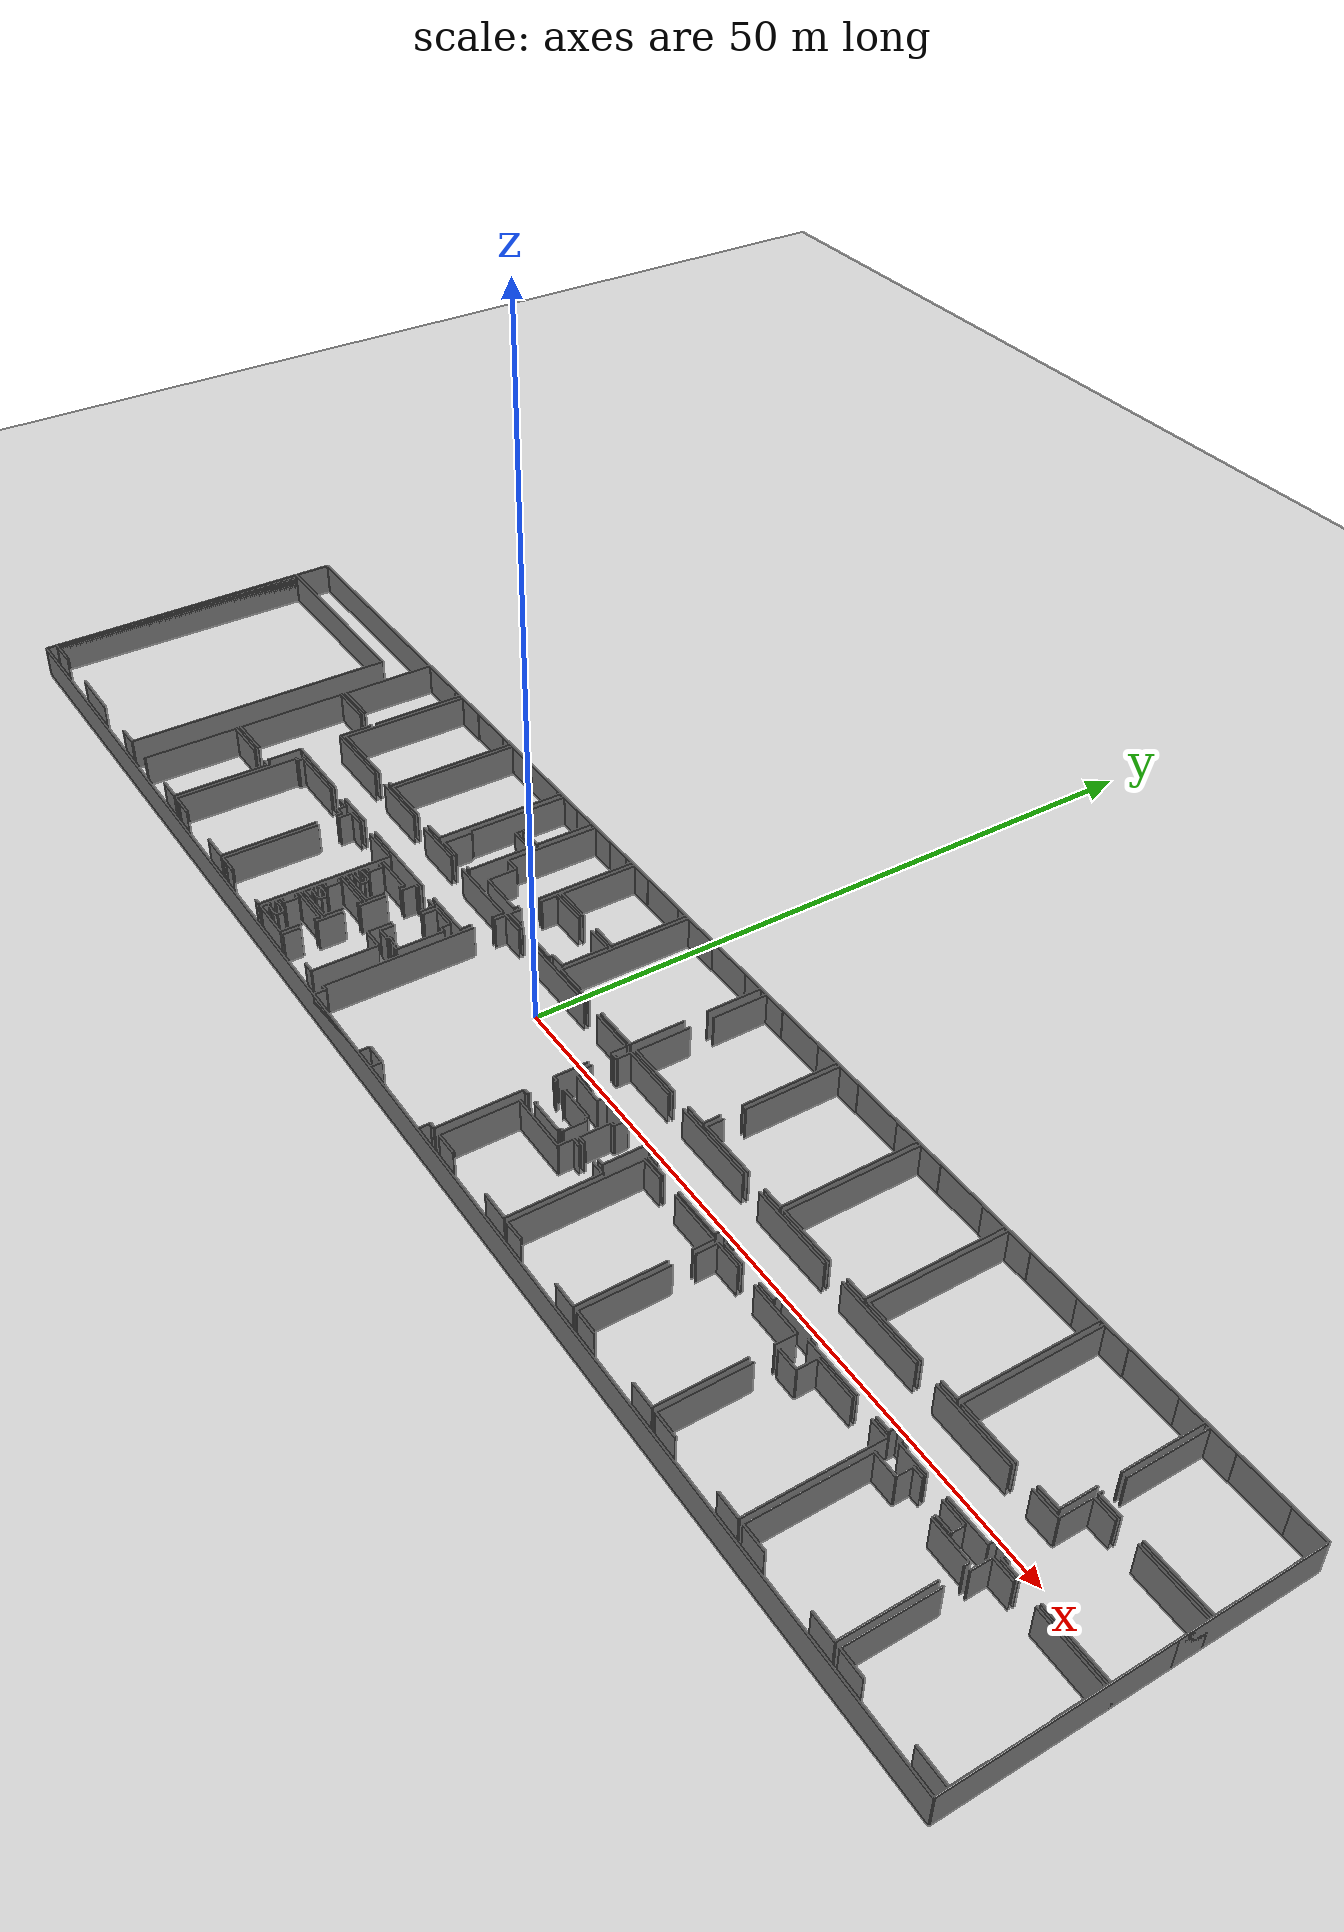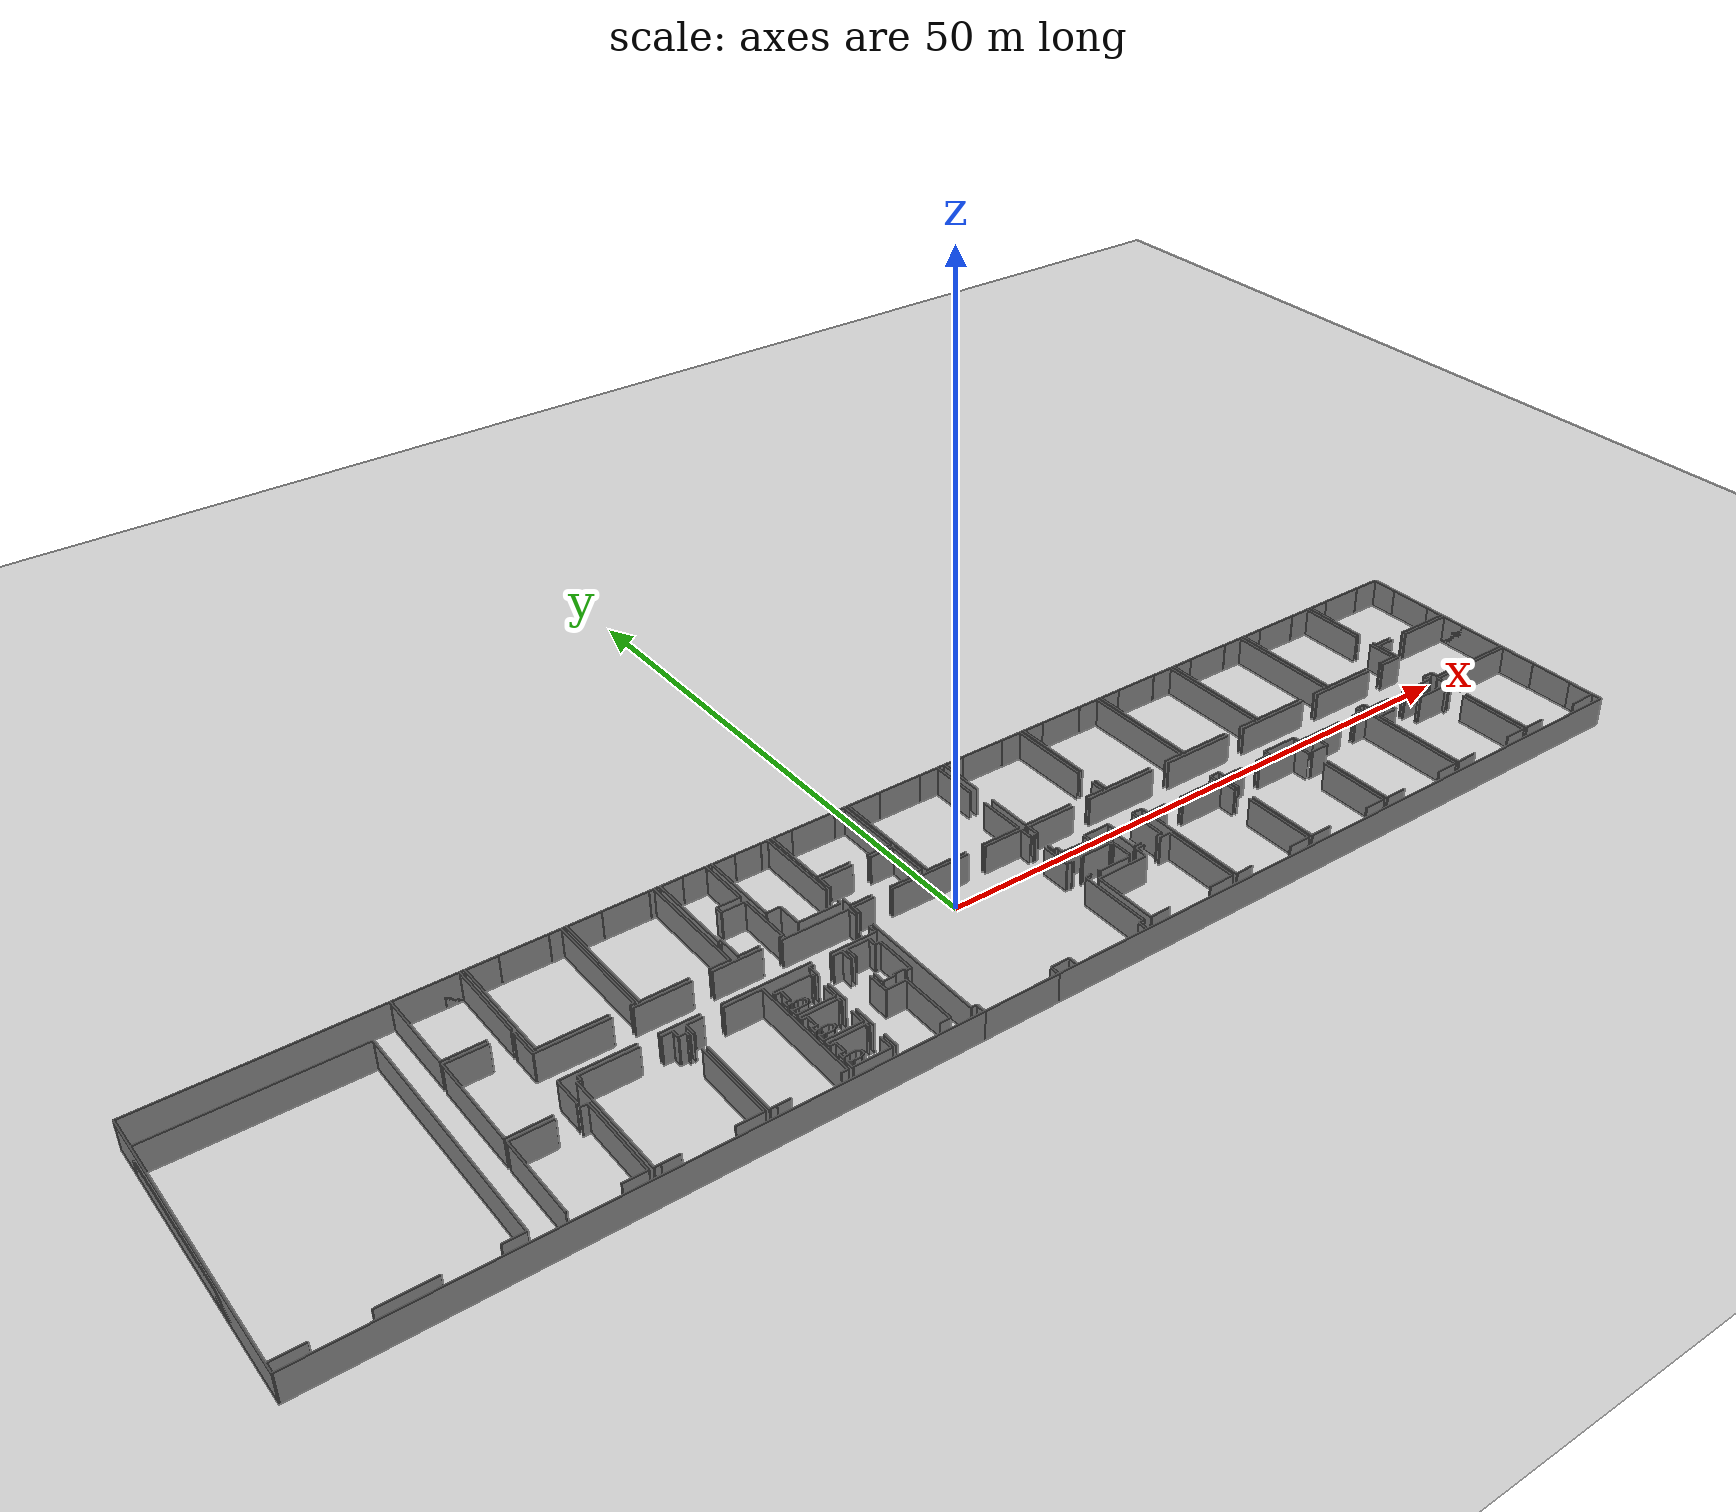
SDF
<sdf version="1.6">
  <world name="default">
    <light name="sun" type="directional">
      <cast_shadows>1</cast_shadows>
      <pose frame="">0 0 10 0 -0 0</pose>
      <diffuse>0.8 0.8 0.8 1</diffuse>
      <specular>0.1 0.1 0.1 1</specular>
      <attenuation>
        <range>1000</range>
        <constant>0.9</constant>
        <linear>0.01</linear>
        <quadratic>0.001</quadratic>
      </attenuation>
      <direction>-0.5 0.5 -1</direction>
    </light>
    <model name="ground_plane">
      <static>1</static>
      <link name="link">
        <collision name="collision">
          <geometry>
            <plane>
              <normal>0 0 1</normal>
              <size>100 100</size>
            </plane>
          </geometry>
          <surface>
            <friction>
              <ode>
                <mu>100</mu>
                <mu2>50</mu2>
              </ode>
              <torsional>
                <ode />
              </torsional>
            </friction>
            <contact>
              <ode />
            </contact>
            <bounce />
          </surface>
          <max_contacts>10</max_contacts>
        </collision>
        <visual name="visual">
          <cast_shadows>0</cast_shadows>
          <geometry>
            <plane>
              <normal>0 0 1</normal>
              <size>100 100</size>
            </plane>
          </geometry>
          <material>
            <script>
              <uri>file://media/materials/scripts/gazebo.material</uri>
              <name>Gazebo/Grey</name>
            </script>
          </material>
        </visual>
        <self_collide>0</self_collide>
        <kinematic>0</kinematic>
        <gravity>1</gravity>
      </link>
    </model>
    <gravity>0 0 -9.8</gravity>
    <magnetic_field>6e-06 2.3e-05 -4.2e-05</magnetic_field>
    <atmosphere type="adiabatic" />
    <physics default="0" name="default_physics" type="ode">
      <max_step_size>0.001</max_step_size>
      <real_time_factor>1</real_time_factor>
      <real_time_update_rate>1000</real_time_update_rate>
    </physics>
    <scene>
      <ambient>0.4 0.4 0.4 1</ambient>
      <background>0.7 0.7 0.7 1</background>
      <shadows>1</shadows>
    </scene>
    <spherical_coordinates>
      <surface_model>EARTH_WGS84</surface_model>
      <latitude_deg>0</latitude_deg>
      <longitude_deg>0</longitude_deg>
      <elevation>0</elevation>
      <heading_deg>0</heading_deg>
    </spherical_coordinates>
  <model name="0510034691_Layout1">
		<static>1</static>
		<link name="Wall_0">
			<collision name="Wall_0_Collision">
				<geometry>
					<box>
						<size>21.0787005262 0.1 2.5</size>
					</box>
				</geometry>
				<pose frame="">10.5393502631 0 1.25 0 0 0</pose>
			</collision>
			<visual name="Wall_0_Visual">
				<pose frame="">10.5393502631 0 1.25 0 0 0</pose>
				<geometry>
					<box>
						<size>21.0787005262 0.1 2.5</size>
					</box>
				</geometry>
				<material>
					<script>
						<uri>file://media/materials/scripts/gazebo.material</uri>
						<name>Gazebo/Grey</name>
					</script>
					<ambient>1 1 1 1</ambient>
				</material>
			</visual>
			<pose frame="">0.0 -23.9743003127 0 0 0 1.57079632679</pose>
		</link>
		<link name="Wall_1">
			<collision name="Wall_1_Collision">
				<geometry>
					<box>
						<size>15.9957040087 0.1 2.5</size>
					</box>
				</geometry>
				<pose frame="">7.99785200437 0 1.25 0 0 0</pose>
			</collision>
			<visual name="Wall_1_Visual">
				<pose frame="">7.99785200437 0 1.25 0 0 0</pose>
				<geometry>
					<box>
						<size>15.9957040087 0.1 2.5</size>
					</box>
				</geometry>
				<material>
					<script>
						<uri>file://media/materials/scripts/gazebo.material</uri>
						<name>Gazebo/Grey</name>
					</script>
					<ambient>1 1 1 1</ambient>
				</material>
			</visual>
			<pose frame="">0.0 -2.89559978647 0 0 0 0.0</pose>
		</link>
		<link name="Wall_2">
			<collision name="Wall_2_Collision">
				<geometry>
					<box>
						<size>21.0752688172 0.1 2.5</size>
					</box>
				</geometry>
				<pose frame="">10.5376344086 0 1.25 0 0 0</pose>
			</collision>
			<visual name="Wall_2_Visual">
				<pose frame="">10.5376344086 0 1.25 0 0 0</pose>
				<geometry>
					<box>
						<size>21.0752688172 0.1 2.5</size>
					</box>
				</geometry>
				<material>
					<script>
						<uri>file://media/materials/scripts/gazebo.material</uri>
						<name>Gazebo/Grey</name>
					</script>
					<ambient>1 1 1 1</ambient>
				</material>
			</visual>
			<pose frame="">15.9957040087 -2.89559978647 0 0 0 -1.57079632679</pose>
		</link>
		<link name="Wall_3">
			<collision name="Wall_3_Collision">
				<geometry>
					<box>
						<size>1.72945423117 0.1 2.5</size>
					</box>
				</geometry>
				<pose frame="">0.864727115585 0 1.25 0 0 0</pose>
			</collision>
			<visual name="Wall_3_Visual">
				<pose frame="">0.864727115585 0 1.25 0 0 0</pose>
				<geometry>
					<box>
						<size>1.72945423117 0.1 2.5</size>
					</box>
				</geometry>
				<material>
					<script>
						<uri>file://media/materials/scripts/gazebo.material</uri>
						<name>Gazebo/Grey</name>
					</script>
					<ambient>1 1 1 1</ambient>
				</material>
			</visual>
			<pose frame="">15.9957040087 -23.9708686037 0 0 0 3.14159265359</pose>
		</link>
		<link name="Wall_4">
			<collision name="Wall_4_Collision">
				<geometry>
					<box>
						<size>4.24299041663 0.1 2.5</size>
					</box>
				</geometry>
				<pose frame="">2.12149520832 0 1.25 0 0 0</pose>
			</collision>
			<visual name="Wall_4_Visual">
				<pose frame="">2.12149520832 0 1.25 0 0 0</pose>
				<geometry>
					<box>
						<size>4.24299041663 0.1 2.5</size>
					</box>
				</geometry>
				<material>
					<script>
						<uri>file://media/materials/scripts/gazebo.material</uri>
						<name>Gazebo/Grey</name>
					</script>
					<ambient>1 1 1 1</ambient>
				</material>
			</visual>
			<pose frame="">10.4819644627 -23.9708686037 0 0 0 3.14159265359</pose>
		</link>
		<link name="Wall_5">
			<collision name="Wall_5_Collision">
				<geometry>
					<box>
						<size>2.45456402988 0.1 2.5</size>
					</box>
				</geometry>
				<pose frame="">1.22728201494 0 1.25 0 0 0</pose>
			</collision>
			<visual name="Wall_5_Visual">
				<pose frame="">1.22728201494 0 1.25 0 0 0</pose>
				<geometry>
					<box>
						<size>2.45456402988 0.1 2.5</size>
					</box>
				</geometry>
				<material>
					<script>
						<uri>file://media/materials/scripts/gazebo.material</uri>
						<name>Gazebo/Grey</name>
					</script>
					<ambient>1 1 1 1</ambient>
				</material>
			</visual>
			<pose frame="">2.45456163095 -23.9708686037 0 0 0 -3.14019456005</pose>
		</link>
		<link name="Wall_6">
			<collision name="Wall_6_Collision">
				<geometry>
					<box>
						<size>0.585424133811 0.1 2.5</size>
					</box>
				</geometry>
				<pose frame="">0.292712066906 0 1.25 0 0 0</pose>
			</collision>
			<visual name="Wall_6_Visual">
				<pose frame="">0.292712066906 0 1.25 0 0 0</pose>
				<geometry>
					<box>
						<size>0.585424133811 0.1 2.5</size>
					</box>
				</geometry>
				<material>
					<script>
						<uri>file://media/materials/scripts/gazebo.material</uri>
						<name>Gazebo/Grey</name>
					</script>
					<ambient>1 1 1 1</ambient>
				</material>
			</visual>
			<pose frame="">19.1292356186 -7.39914588576 0 0 0 3.14159265359</pose>
		</link>
		<link name="Wall_7">
			<collision name="Wall_7_Collision">
				<geometry>
					<box>
						<size>7.39914588576 0.1 2.5</size>
					</box>
				</geometry>
				<pose frame="">3.69957294288 0 1.25 0 0 0</pose>
			</collision>
			<visual name="Wall_7_Visual">
				<pose frame="">3.69957294288 0 1.25 0 0 0</pose>
				<geometry>
					<box>
						<size>7.39914588576 0.1 2.5</size>
					</box>
				</geometry>
				<material>
					<script>
						<uri>file://media/materials/scripts/gazebo.material</uri>
						<name>Gazebo/Grey</name>
					</script>
					<ambient>1 1 1 1</ambient>
				</material>
			</visual>
			<pose frame="">18.5438114848 -7.39914588576 0 0 0 1.57079632679</pose>
		</link>
		<link name="Wall_8">
			<collision name="Wall_8_Collision">
				<geometry>
					<box>
						<size>1.32972368388 0.1 2.5</size>
					</box>
				</geometry>
				<pose frame="">0.664861841938 0 1.25 0 0 0</pose>
			</collision>
			<visual name="Wall_8_Visual">
				<pose frame="">0.664861841938 0 1.25 0 0 0</pose>
				<geometry>
					<box>
						<size>1.32972368388 0.1 2.5</size>
					</box>
				</geometry>
				<material>
					<script>
						<uri>file://media/materials/scripts/gazebo.material</uri>
						<name>Gazebo/Grey</name>
					</script>
					<ambient>1 1 1 1</ambient>
				</material>
			</visual>
			<pose frame="">22.2709016498 -0.0 0 0 0 0.0</pose>
		</link>
		<link name="Wall_9">
			<collision name="Wall_9_Collision">
				<geometry>
					<box>
						<size>7.37385291949 0.1 2.5</size>
					</box>
				</geometry>
				<pose frame="">3.68692645975 0 1.25 0 0 0</pose>
			</collision>
			<visual name="Wall_9_Visual">
				<pose frame="">3.68692645975 0 1.25 0 0 0</pose>
				<geometry>
					<box>
						<size>7.37385291949 0.1 2.5</size>
					</box>
				</geometry>
				<material>
					<script>
						<uri>file://media/materials/scripts/gazebo.material</uri>
						<name>Gazebo/Grey</name>
					</script>
					<ambient>1 1 1 1</ambient>
				</material>
			</visual>
			<pose frame="">23.6006253336 -0.0 0 0 0 -1.57079632679</pose>
		</link>
		<link name="Wall_10">
			<collision name="Wall_10_Collision">
				<geometry>
					<box>
						<size>2.72959683848 0.1 2.5</size>
					</box>
				</geometry>
				<pose frame="">1.36479841924 0 1.25 0 0 0</pose>
			</collision>
			<visual name="Wall_10_Visual">
				<pose frame="">1.36479841924 0 1.25 0 0 0</pose>
				<geometry>
					<box>
						<size>2.72959683848 0.1 2.5</size>
					</box>
				</geometry>
				<material>
					<script>
						<uri>file://media/materials/scripts/gazebo.material</uri>
						<name>Gazebo/Grey</name>
					</script>
					<ambient>1 1 1 1</ambient>
				</material>
			</visual>
			<pose frame="">21.8587152698 -7.37385291949 0 0 0 -3.13232632976</pose>
		</link>
		<link name="Wall_11">
			<collision name="Wall_11_Collision">
				<geometry>
					<box>
						<size>7.40689900608 0.1 2.5</size>
					</box>
				</geometry>
				<pose frame="">3.70344950304 0 1.25 0 0 0</pose>
			</collision>
			<visual name="Wall_11_Visual">
				<pose frame="">3.70344950304 0 1.25 0 0 0</pose>
				<geometry>
					<box>
						<size>7.40689900608 0.1 2.5</size>
					</box>
				</geometry>
				<material>
					<script>
						<uri>file://media/materials/scripts/gazebo.material</uri>
						<name>Gazebo/Grey</name>
					</script>
					<ambient>1 1 1 1</ambient>
				</material>
			</visual>
			<pose frame="">18.5317369532 -24.0081090012 0 0 0 1.57079632679</pose>
		</link>
		<link name="Wall_12">
			<collision name="Wall_12_Collision">
				<geometry>
					<box>
						<size>3.34006965098 0.1 2.5</size>
					</box>
				</geometry>
				<pose frame="">1.67003482549 0 1.25 0 0 0</pose>
			</collision>
			<visual name="Wall_12_Visual">
				<pose frame="">1.67003482549 0 1.25 0 0 0</pose>
				<geometry>
					<box>
						<size>3.34006965098 0.1 2.5</size>
					</box>
				</geometry>
				<material>
					<script>
						<uri>file://media/materials/scripts/gazebo.material</uri>
						<name>Gazebo/Grey</name>
					</script>
					<ambient>1 1 1 1</ambient>
				</material>
			</visual>
			<pose frame="">18.5317369532 -16.6012099952 0 0 0 0.0</pose>
		</link>
		<link name="Wall_13">
			<collision name="Wall_13_Collision">
				<geometry>
					<box>
						<size>0.619487023056 0.1 2.5</size>
					</box>
				</geometry>
				<pose frame="">0.309743511528 0 1.25 0 0 0</pose>
			</collision>
			<visual name="Wall_13_Visual">
				<pose frame="">0.309743511528 0 1.25 0 0 0</pose>
				<geometry>
					<box>
						<size>0.619487023056 0.1 2.5</size>
					</box>
				</geometry>
				<material>
					<script>
						<uri>file://media/materials/scripts/gazebo.material</uri>
						<name>Gazebo/Grey</name>
					</script>
					<ambient>1 1 1 1</ambient>
				</material>
			</visual>
			<pose frame="">23.5525814078 -16.6012099952 0 0 0 0.0</pose>
		</link>
		<link name="Wall_14">
			<collision name="Wall_14_Collision">
				<geometry>
					<box>
						<size>7.36317649152 0.1 2.5</size>
					</box>
				</geometry>
				<pose frame="">3.68158824576 0 1.25 0 0 0</pose>
			</collision>
			<visual name="Wall_14_Visual">
				<pose frame="">3.68158824576 0 1.25 0 0 0</pose>
				<geometry>
					<box>
						<size>7.36317649152 0.1 2.5</size>
					</box>
				</geometry>
				<material>
					<script>
						<uri>file://media/materials/scripts/gazebo.material</uri>
						<name>Gazebo/Grey</name>
					</script>
					<ambient>1 1 1 1</ambient>
				</material>
			</visual>
			<pose frame="">24.1720684308 -16.6012099952 0 0 0 -1.57079632679</pose>
		</link>
		<link name="Wall_15">
			<collision name="Wall_15_Collision">
				<geometry>
					<box>
						<size>1.87536541346 0.1 2.5</size>
					</box>
				</geometry>
				<pose frame="">0.937682706729 0 1.25 0 0 0</pose>
			</collision>
			<visual name="Wall_15_Visual">
				<pose frame="">0.937682706729 0 1.25 0 0 0</pose>
				<geometry>
					<box>
						<size>1.87536541346 0.1 2.5</size>
					</box>
				</geometry>
				<material>
					<script>
						<uri>file://media/materials/scripts/gazebo.material</uri>
						<name>Gazebo/Grey</name>
					</script>
					<ambient>1 1 1 1</ambient>
				</material>
			</visual>
			<pose frame="">24.1720684308 -23.9643864867 0 0 0 3.14159265359</pose>
		</link>
		<link name="Wall_16">
			<collision name="Wall_16_Collision">
				<geometry>
					<box>
						<size>0.0601496199172 0.1 2.5</size>
					</box>
				</geometry>
				<pose frame="">0.0300748099586 0 1.25 0 0 0</pose>
			</collision>
			<visual name="Wall_16_Visual">
				<pose frame="">0.0300748099586 0 1.25 0 0 0</pose>
				<geometry>
					<box>
						<size>0.0601496199172 0.1 2.5</size>
					</box>
				</geometry>
				<material>
					<script>
						<uri>file://media/materials/scripts/gazebo.material</uri>
						<name>Gazebo/Grey</name>
					</script>
					<ambient>1 1 1 1</ambient>
				</material>
			</visual>
			<pose frame="">18.5730445614 -23.9643864867 0 0 0 -2.32780152451</pose>
		</link>
		<link name="Wall_17">
			<collision name="Wall_17_Collision">
				<geometry>
					<box>
						<size>0.468237626783 0.1 2.5</size>
					</box>
				</geometry>
				<pose frame="">0.234118813391 0 1.25 0 0 0</pose>
			</collision>
			<visual name="Wall_17_Visual">
				<pose frame="">0.234118813391 0 1.25 0 0 0</pose>
				<geometry>
					<box>
						<size>0.468237626783 0.1 2.5</size>
					</box>
				</geometry>
				<material>
					<script>
						<uri>file://media/materials/scripts/gazebo.material</uri>
						<name>Gazebo/Grey</name>
					</script>
					<ambient>1 1 1 1</ambient>
				</material>
			</visual>
			<pose frame="">25.0218612573 -23.9708686037 0 0 0 3.14159265359</pose>
		</link>
		<link name="Wall_18">
			<collision name="Wall_18_Collision">
				<geometry>
					<box>
						<size>9.5132057246 0.1 2.5</size>
					</box>
				</geometry>
				<pose frame="">4.7566028623 0 1.25 0 0 0</pose>
			</collision>
			<visual name="Wall_18_Visual">
				<pose frame="">4.7566028623 0 1.25 0 0 0</pose>
				<geometry>
					<box>
						<size>9.5132057246 0.1 2.5</size>
					</box>
				</geometry>
				<material>
					<script>
						<uri>file://media/materials/scripts/gazebo.material</uri>
						<name>Gazebo/Grey</name>
					</script>
					<ambient>1 1 1 1</ambient>
				</material>
			</visual>
			<pose frame="">24.5536236305 -23.9708686037 0 0 0 1.57079632679</pose>
		</link>
		<link name="Wall_19">
			<collision name="Wall_19_Collision">
				<geometry>
					<box>
						<size>0.319657337502 0.1 2.5</size>
					</box>
				</geometry>
				<pose frame="">0.159828668751 0 1.25 0 0 0</pose>
			</collision>
			<visual name="Wall_19_Visual">
				<pose frame="">0.159828668751 0 1.25 0 0 0</pose>
				<geometry>
					<box>
						<size>0.319657337502 0.1 2.5</size>
					</box>
				</geometry>
				<material>
					<script>
						<uri>file://media/materials/scripts/gazebo.material</uri>
						<name>Gazebo/Grey</name>
					</script>
					<ambient>1 1 1 1</ambient>
				</material>
			</visual>
			<pose frame="">24.5536236305 -14.4576628791 0 0 0 0.0</pose>
		</link>
		<link name="Wall_20">
			<collision name="Wall_20_Collision">
				<geometry>
					<box>
						<size>0.479930857419 0.1 2.5</size>
					</box>
				</geometry>
				<pose frame="">0.239965428709 0 1.25 0 0 0</pose>
			</collision>
			<visual name="Wall_20_Visual">
				<pose frame="">0.239965428709 0 1.25 0 0 0</pose>
				<geometry>
					<box>
						<size>0.479930857419 0.1 2.5</size>
					</box>
				</geometry>
				<material>
					<script>
						<uri>file://media/materials/scripts/gazebo.material</uri>
						<name>Gazebo/Grey</name>
					</script>
					<ambient>1 1 1 1</ambient>
				</material>
			</visual>
			<pose frame="">24.873280968 -14.4576628791 0 0 0 1.57079632679</pose>
		</link>
		<link name="Wall_21">
			<collision name="Wall_21_Collision">
				<geometry>
					<box>
						<size>4.56493556013 0.1 2.5</size>
					</box>
				</geometry>
				<pose frame="">2.28246778007 0 1.25 0 0 0</pose>
			</collision>
			<visual name="Wall_21_Visual">
				<pose frame="">2.28246778007 0 1.25 0 0 0</pose>
				<geometry>
					<box>
						<size>4.56493556013 0.1 2.5</size>
					</box>
				</geometry>
				<material>
					<script>
						<uri>file://media/materials/scripts/gazebo.material</uri>
						<name>Gazebo/Grey</name>
					</script>
					<ambient>1 1 1 1</ambient>
				</material>
			</visual>
			<pose frame="">24.873280968 -13.9777320217 0 0 0 0.0</pose>
		</link>
		<link name="Wall_22">
			<collision name="Wall_22_Collision">
				<geometry>
					<box>
						<size>0.912199089962 0.1 2.5</size>
					</box>
				</geometry>
				<pose frame="">0.456099544981 0 1.25 0 0 0</pose>
			</collision>
			<visual name="Wall_22_Visual">
				<pose frame="">0.456099544981 0 1.25 0 0 0</pose>
				<geometry>
					<box>
						<size>0.912199089962 0.1 2.5</size>
					</box>
				</geometry>
				<material>
					<script>
						<uri>file://media/materials/scripts/gazebo.material</uri>
						<name>Gazebo/Grey</name>
					</script>
					<ambient>1 1 1 1</ambient>
				</material>
			</visual>
			<pose frame="">31.0258267877 -13.9777320217 0 0 0 0.0</pose>
		</link>
		<link name="Wall_23">
			<collision name="Wall_23_Collision">
				<geometry>
					<box>
						<size>0.694730420194 0.1 2.5</size>
					</box>
				</geometry>
				<pose frame="">0.347365210097 0 1.25 0 0 0</pose>
			</collision>
			<visual name="Wall_23_Visual">
				<pose frame="">0.347365210097 0 1.25 0 0 0</pose>
				<geometry>
					<box>
						<size>0.694730420194 0.1 2.5</size>
					</box>
				</geometry>
				<material>
					<script>
						<uri>file://media/materials/scripts/gazebo.material</uri>
						<name>Gazebo/Grey</name>
					</script>
					<ambient>1 1 1 1</ambient>
				</material>
			</visual>
			<pose frame="">31.9380258776 -13.9777320217 0 0 0 -1.57079632679</pose>
		</link>
		<link name="Wall_24">
			<collision name="Wall_24_Collision">
				<geometry>
					<box>
						<size>0.626223340705 0.1 2.5</size>
					</box>
				</geometry>
				<pose frame="">0.313111670353 0 1.25 0 0 0</pose>
			</collision>
			<visual name="Wall_24_Visual">
				<pose frame="">0.313111670353 0 1.25 0 0 0</pose>
				<geometry>
					<box>
						<size>0.626223340705 0.1 2.5</size>
					</box>
				</geometry>
				<material>
					<script>
						<uri>file://media/materials/scripts/gazebo.material</uri>
						<name>Gazebo/Grey</name>
					</script>
					<ambient>1 1 1 1</ambient>
				</material>
			</visual>
			<pose frame="">31.9380258776 -14.6724624419 0 0 0 0.0</pose>
		</link>
		<link name="Wall_25">
			<collision name="Wall_25_Collision">
				<geometry>
					<box>
						<size>0.368082564376 0.1 2.5</size>
					</box>
				</geometry>
				<pose frame="">0.184041282188 0 1.25 0 0 0</pose>
			</collision>
			<visual name="Wall_25_Visual">
				<pose frame="">0.184041282188 0 1.25 0 0 0</pose>
				<geometry>
					<box>
						<size>0.368082564376 0.1 2.5</size>
					</box>
				</geometry>
				<material>
					<script>
						<uri>file://media/materials/scripts/gazebo.material</uri>
						<name>Gazebo/Grey</name>
					</script>
					<ambient>1 1 1 1</ambient>
				</material>
			</visual>
			<pose frame="">32.5642492183 -14.6724624419 0 0 0 -1.57079632679</pose>
		</link>
		<link name="Wall_26">
			<collision name="Wall_26_Collision">
				<geometry>
					<box>
						<size>7.34029843158 0.1 2.5</size>
					</box>
				</geometry>
				<pose frame="">3.67014921579 0 1.25 0 0 0</pose>
			</collision>
			<visual name="Wall_26_Visual">
				<pose frame="">3.67014921579 0 1.25 0 0 0</pose>
				<geometry>
					<box>
						<size>7.34029843158 0.1 2.5</size>
					</box>
				</geometry>
				<material>
					<script>
						<uri>file://media/materials/scripts/gazebo.material</uri>
						<name>Gazebo/Grey</name>
					</script>
					<ambient>1 1 1 1</ambient>
				</material>
			</visual>
			<pose frame="">32.5642492183 -16.6276468644 0 0 0 -1.57079632679</pose>
		</link>
		<link name="Wall_27">
			<collision name="Wall_27_Collision">
				<geometry>
					<box>
						<size>2.19337044663 0.1 2.5</size>
					</box>
				</geometry>
				<pose frame="">1.09668522332 0 1.25 0 0 0</pose>
			</collision>
			<visual name="Wall_27_Visual">
				<pose frame="">1.09668522332 0 1.25 0 0 0</pose>
				<geometry>
					<box>
						<size>2.19337044663 0.1 2.5</size>
					</box>
				</geometry>
				<material>
					<script>
						<uri>file://media/materials/scripts/gazebo.material</uri>
						<name>Gazebo/Grey</name>
					</script>
					<ambient>1 1 1 1</ambient>
				</material>
			</visual>
			<pose frame="">32.5642492183 -23.967945296 0 0 0 3.14159265359</pose>
		</link>
		<link name="Wall_28">
			<collision name="Wall_28_Collision">
				<geometry>
					<box>
						<size>1.461910953 0.1 2.5</size>
					</box>
				</geometry>
				<pose frame="">0.730955476498 0 1.25 0 0 0</pose>
			</collision>
			<visual name="Wall_28_Visual">
				<pose frame="">0.730955476498 0 1.25 0 0 0</pose>
				<geometry>
					<box>
						<size>1.461910953 0.1 2.5</size>
					</box>
				</geometry>
				<material>
					<script>
						<uri>file://media/materials/scripts/gazebo.material</uri>
						<name>Gazebo/Grey</name>
					</script>
					<ambient>1 1 1 1</ambient>
				</material>
			</visual>
			<pose frame="">26.4837692875 -23.967945296 0 0 0 -3.13959300402</pose>
		</link>
		<link name="Wall_29">
			<collision name="Wall_29_Collision">
				<geometry>
					<box>
						<size>0.520984264979 0.1 2.5</size>
					</box>
				</geometry>
				<pose frame="">0.260492132489 0 1.25 0 0 0</pose>
			</collision>
			<visual name="Wall_29_Visual">
				<pose frame="">0.260492132489 0 1.25 0 0 0</pose>
				<geometry>
					<box>
						<size>0.520984264979 0.1 2.5</size>
					</box>
				</geometry>
				<material>
					<script>
						<uri>file://media/materials/scripts/gazebo.material</uri>
						<name>Gazebo/Grey</name>
					</script>
					<ambient>1 1 1 1</ambient>
				</material>
			</visual>
			<pose frame="">33.4409873154 -23.972139607 0 0 0 3.14159265359</pose>
		</link>
		<link name="Wall_30">
			<collision name="Wall_30_Collision">
				<geometry>
					<box>
						<size>7.33279951193 0.1 2.5</size>
					</box>
				</geometry>
				<pose frame="">3.66639975597 0 1.25 0 0 0</pose>
			</collision>
			<visual name="Wall_30_Visual">
				<pose frame="">3.66639975597 0 1.25 0 0 0</pose>
				<geometry>
					<box>
						<size>7.33279951193 0.1 2.5</size>
					</box>
				</geometry>
				<material>
					<script>
						<uri>file://media/materials/scripts/gazebo.material</uri>
						<name>Gazebo/Grey</name>
					</script>
					<ambient>1 1 1 1</ambient>
				</material>
			</visual>
			<pose frame="">32.9200030504 -23.972139607 0 0 0 1.57079632679</pose>
		</link>
		<link name="Wall_31">
			<collision name="Wall_31_Collision">
				<geometry>
					<box>
						<size>1.05264495793 0.1 2.5</size>
					</box>
				</geometry>
				<pose frame="">0.526322478965 0 1.25 0 0 0</pose>
			</collision>
			<visual name="Wall_31_Visual">
				<pose frame="">0.526322478965 0 1.25 0 0 0</pose>
				<geometry>
					<box>
						<size>1.05264495793 0.1 2.5</size>
					</box>
				</geometry>
				<material>
					<script>
						<uri>file://media/materials/scripts/gazebo.material</uri>
						<name>Gazebo/Grey</name>
					</script>
					<ambient>1 1 1 1</ambient>
				</material>
			</visual>
			<pose frame="">32.9200030504 -15.0299956786 0 0 0 1.57079632679</pose>
		</link>
		<link name="Wall_32">
			<collision name="Wall_32_Collision">
				<geometry>
					<box>
						<size>1.32451257022 0.1 2.5</size>
					</box>
				</geometry>
				<pose frame="">0.662256285111 0 1.25 0 0 0</pose>
			</collision>
			<visual name="Wall_32_Visual">
				<pose frame="">0.662256285111 0 1.25 0 0 0</pose>
				<geometry>
					<box>
						<size>1.32451257022 0.1 2.5</size>
					</box>
				</geometry>
				<material>
					<script>
						<uri>file://media/materials/scripts/gazebo.material</uri>
						<name>Gazebo/Grey</name>
					</script>
					<ambient>1 1 1 1</ambient>
				</material>
			</visual>
			<pose frame="">32.9200030504 -13.9773507207 0 0 0 0.0</pose>
		</link>
		<link name="Wall_33">
			<collision name="Wall_33_Collision">
				<geometry>
					<box>
						<size>3.07735326267 0.1 2.5</size>
					</box>
				</geometry>
				<pose frame="">1.53867663133 0 1.25 0 0 0</pose>
			</collision>
			<visual name="Wall_33_Visual">
				<pose frame="">1.53867663133 0 1.25 0 0 0</pose>
				<geometry>
					<box>
						<size>3.07735326267 0.1 2.5</size>
					</box>
				</geometry>
				<material>
					<script>
						<uri>file://media/materials/scripts/gazebo.material</uri>
						<name>Gazebo/Grey</name>
					</script>
					<ambient>1 1 1 1</ambient>
				</material>
			</visual>
			<pose frame="">35.8243727599 -13.9773507207 0 0 0 0.0</pose>
		</link>
		<link name="Wall_34">
			<collision name="Wall_34_Collision">
				<geometry>
					<box>
						<size>9.99135717736 0.1 2.5</size>
					</box>
				</geometry>
				<pose frame="">4.99567858868 0 1.25 0 0 0</pose>
			</collision>
			<visual name="Wall_34_Visual">
				<pose frame="">4.99567858868 0 1.25 0 0 0</pose>
				<geometry>
					<box>
						<size>9.99135717736 0.1 2.5</size>
					</box>
				</geometry>
				<material>
					<script>
						<uri>file://media/materials/scripts/gazebo.material</uri>
						<name>Gazebo/Grey</name>
					</script>
					<ambient>1 1 1 1</ambient>
				</material>
			</visual>
			<pose frame="">38.9017260225 -13.9773507207 0 0 0 -1.57079632679</pose>
		</link>
		<link name="Wall_35">
			<collision name="Wall_35_Collision">
				<geometry>
					<box>
						<size>0.519840361982 0.1 2.5</size>
					</box>
				</geometry>
				<pose frame="">0.259920180991 0 1.25 0 0 0</pose>
			</collision>
			<visual name="Wall_35_Visual">
				<pose frame="">0.259920180991 0 1.25 0 0 0</pose>
				<geometry>
					<box>
						<size>0.519840361982 0.1 2.5</size>
					</box>
				</geometry>
				<material>
					<script>
						<uri>file://media/materials/scripts/gazebo.material</uri>
						<name>Gazebo/Grey</name>
					</script>
					<ambient>1 1 1 1</ambient>
				</material>
			</visual>
			<pose frame="">38.9017260225 -23.968707898 0 0 0 3.14159265359</pose>
		</link>
		<link name="Wall_36">
			<collision name="Wall_36_Collision">
				<geometry>
					<box>
						<size>1.07807048644 0.1 2.5</size>
					</box>
				</geometry>
				<pose frame="">0.539035243222 0 1.25 0 0 0</pose>
			</collision>
			<visual name="Wall_36_Visual">
				<pose frame="">0.539035243222 0 1.25 0 0 0</pose>
				<geometry>
					<box>
						<size>1.07807048644 0.1 2.5</size>
					</box>
				</geometry>
				<material>
					<script>
						<uri>file://media/materials/scripts/gazebo.material</uri>
						<name>Gazebo/Grey</name>
					</script>
					<ambient>1 1 1 1</ambient>
				</material>
			</visual>
			<pose frame="">34.5190523399 -23.968707898 0 0 0 -3.13840945283</pose>
		</link>
		<link name="Wall_37">
			<collision name="Wall_37_Collision">
				<geometry>
					<box>
						<size>9.99491598668 0.1 2.5</size>
					</box>
				</geometry>
				<pose frame="">4.99745799334 0 1.25 0 0 0</pose>
			</collision>
			<visual name="Wall_37_Visual">
				<pose frame="">4.99745799334 0 1.25 0 0 0</pose>
				<geometry>
					<box>
						<size>9.99491598668 0.1 2.5</size>
					</box>
				</geometry>
				<material>
					<script>
						<uri>file://media/materials/scripts/gazebo.material</uri>
						<name>Gazebo/Grey</name>
					</script>
					<ambient>1 1 1 1</ambient>
				</material>
			</visual>
			<pose frame="">23.9891710516 -10.0157604413 0 0 0 1.57079632679</pose>
		</link>
		<link name="Wall_38">
			<collision name="Wall_38_Collision">
				<geometry>
					<box>
						<size>2.48214240321 0.1 2.5</size>
					</box>
				</geometry>
				<pose frame="">1.24107120161 0 1.25 0 0 0</pose>
			</collision>
			<visual name="Wall_38_Visual">
				<pose frame="">1.24107120161 0 1.25 0 0 0</pose>
				<geometry>
					<box>
						<size>2.48214240321 0.1 2.5</size>
					</box>
				</geometry>
				<material>
					<script>
						<uri>file://media/materials/scripts/gazebo.material</uri>
						<name>Gazebo/Grey</name>
					</script>
					<ambient>1 1 1 1</ambient>
				</material>
			</visual>
			<pose frame="">23.9891710516 -0.0208444546125 0 0 0 0.0</pose>
		</link>
		<link name="Wall_39">
			<collision name="Wall_39_Collision">
				<geometry>
					<box>
						<size>1.03624901497 0.1 2.5</size>
					</box>
				</geometry>
				<pose frame="">0.518124507486 0 1.25 0 0 0</pose>
			</collision>
			<visual name="Wall_39_Visual">
				<pose frame="">0.518124507486 0 1.25 0 0 0</pose>
				<geometry>
					<box>
						<size>1.03624901497 0.1 2.5</size>
					</box>
				</geometry>
				<material>
					<script>
						<uri>file://media/materials/scripts/gazebo.material</uri>
						<name>Gazebo/Grey</name>
					</script>
					<ambient>1 1 1 1</ambient>
				</material>
			</visual>
			<pose frame="">30.3322402705 -0.0208444546125 0 0 0 0.0</pose>
		</link>
		<link name="Wall_40">
			<collision name="Wall_40_Collision">
				<geometry>
					<box>
						<size>9.98373115738 0.1 2.5</size>
					</box>
				</geometry>
				<pose frame="">4.99186557869 0 1.25 0 0 0</pose>
			</collision>
			<visual name="Wall_40_Visual">
				<pose frame="">4.99186557869 0 1.25 0 0 0</pose>
				<geometry>
					<box>
						<size>9.98373115738 0.1 2.5</size>
					</box>
				</geometry>
				<material>
					<script>
						<uri>file://media/materials/scripts/gazebo.material</uri>
						<name>Gazebo/Grey</name>
					</script>
					<ambient>1 1 1 1</ambient>
				</material>
			</visual>
			<pose frame="">31.3684892854 -0.0208444546125 0 0 0 -1.57079632679</pose>
		</link>
		<link name="Wall_41">
			<collision name="Wall_41_Collision">
				<geometry>
					<box>
						<size>0.337578484456 0.1 2.5</size>
					</box>
				</geometry>
				<pose frame="">0.168789242228 0 1.25 0 0 0</pose>
			</collision>
			<visual name="Wall_41_Visual">
				<pose frame="">0.168789242228 0 1.25 0 0 0</pose>
				<geometry>
					<box>
						<size>0.337578484456 0.1 2.5</size>
					</box>
				</geometry>
				<material>
					<script>
						<uri>file://media/materials/scripts/gazebo.material</uri>
						<name>Gazebo/Grey</name>
					</script>
					<ambient>1 1 1 1</ambient>
				</material>
			</visual>
			<pose frame="">31.3684892854 -10.004575612 0 0 0 3.14159265359</pose>
		</link>
		<link name="Wall_42">
			<collision name="Wall_42_Collision">
				<geometry>
					<box>
						<size>5.45261575743 0.1 2.5</size>
					</box>
				</geometry>
				<pose frame="">2.72630787872 0 1.25 0 0 0</pose>
			</collision>
			<visual name="Wall_42_Visual">
				<pose frame="">2.72630787872 0 1.25 0 0 0</pose>
				<geometry>
					<box>
						<size>5.45261575743 0.1 2.5</size>
					</box>
				</geometry>
				<material>
					<script>
						<uri>file://media/materials/scripts/gazebo.material</uri>
						<name>Gazebo/Grey</name>
					</script>
					<ambient>1 1 1 1</ambient>
				</material>
			</visual>
			<pose frame="">29.4417753375 -10.004575612 0 0 0 -3.13954137442</pose>
		</link>
		<link name="Wall_43">
			<collision name="Wall_43_Collision">
				<geometry>
					<box>
						<size>10.006863418 0.1 2.5</size>
					</box>
				</geometry>
				<pose frame="">5.00343170899 0 1.25 0 0 0</pose>
			</collision>
			<visual name="Wall_43_Visual">
				<pose frame="">5.00343170899 0 1.25 0 0 0</pose>
				<geometry>
					<box>
						<size>10.006863418 0.1 2.5</size>
					</box>
				</geometry>
				<material>
					<script>
						<uri>file://media/materials/scripts/gazebo.material</uri>
						<name>Gazebo/Grey</name>
					</script>
					<ambient>1 1 1 1</ambient>
				</material>
			</visual>
			<pose frame="">31.7353008465 -10.0282162739 0 0 0 1.57079632679</pose>
		</link>
		<link name="Wall_44">
			<collision name="Wall_44_Collision">
				<geometry>
					<box>
						<size>2.77854037978 0.1 2.5</size>
					</box>
				</geometry>
				<pose frame="">1.38927018989 0 1.25 0 0 0</pose>
			</collision>
			<visual name="Wall_44_Visual">
				<pose frame="">1.38927018989 0 1.25 0 0 0</pose>
				<geometry>
					<box>
						<size>2.77854037978 0.1 2.5</size>
					</box>
				</geometry>
				<material>
					<script>
						<uri>file://media/materials/scripts/gazebo.material</uri>
						<name>Gazebo/Grey</name>
					</script>
					<ambient>1 1 1 1</ambient>
				</material>
			</visual>
			<pose frame="">31.7353008465 -0.0213528559445 0 0 0 0.0</pose>
		</link>
		<link name="Wall_45">
			<collision name="Wall_45_Collision">
				<geometry>
					<box>
						<size>0.464933018125 0.1 2.5</size>
					</box>
				</geometry>
				<pose frame="">0.232466509062 0 1.25 0 0 0</pose>
			</collision>
			<visual name="Wall_45_Visual">
				<pose frame="">0.232466509062 0 1.25 0 0 0</pose>
				<geometry>
					<box>
						<size>0.464933018125 0.1 2.5</size>
					</box>
				</geometry>
				<material>
					<script>
						<uri>file://media/materials/scripts/gazebo.material</uri>
						<name>Gazebo/Grey</name>
					</script>
					<ambient>1 1 1 1</ambient>
				</material>
			</visual>
			<pose frame="">38.3604057043 -0.0213528559445 0 0 0 0.0</pose>
		</link>
		<link name="Wall_46">
			<collision name="Wall_46_Collision">
				<geometry>
					<box>
						<size>9.98970487303 0.1 2.5</size>
					</box>
				</geometry>
				<pose frame="">4.99485243651 0 1.25 0 0 0</pose>
			</collision>
			<visual name="Wall_46_Visual">
				<pose frame="">4.99485243651 0 1.25 0 0 0</pose>
				<geometry>
					<box>
						<size>9.98970487303 0.1 2.5</size>
					</box>
				</geometry>
				<material>
					<script>
						<uri>file://media/materials/scripts/gazebo.material</uri>
						<name>Gazebo/Grey</name>
					</script>
					<ambient>1 1 1 1</ambient>
				</material>
			</visual>
			<pose frame="">38.8253387224 -0.0213528559445 0 0 0 -1.57079632679</pose>
		</link>
		<link name="Wall_47">
			<collision name="Wall_47_Collision">
				<geometry>
					<box>
						<size>1.63934009507 0.1 2.5</size>
					</box>
				</geometry>
				<pose frame="">0.819670047536 0 1.25 0 0 0</pose>
			</collision>
			<visual name="Wall_47_Visual">
				<pose frame="">0.819670047536 0 1.25 0 0 0</pose>
				<geometry>
					<box>
						<size>1.63934009507 0.1 2.5</size>
					</box>
				</geometry>
				<material>
					<script>
						<uri>file://media/materials/scripts/gazebo.material</uri>
						<name>Gazebo/Grey</name>
					</script>
					<ambient>1 1 1 1</ambient>
				</material>
			</visual>
			<pose frame="">38.8253387224 -10.011057729 0 0 0 3.14159265359</pose>
		</link>
		<link name="Wall_48">
			<collision name="Wall_48_Collision">
				<geometry>
					<box>
						<size>3.86452371724 0.1 2.5</size>
					</box>
				</geometry>
				<pose frame="">1.93226185862 0 1.25 0 0 0</pose>
			</collision>
			<visual name="Wall_48_Visual">
				<pose frame="">1.93226185862 0 1.25 0 0 0</pose>
				<geometry>
					<box>
						<size>3.86452371724 0.1 2.5</size>
					</box>
				</geometry>
				<material>
					<script>
						<uri>file://media/materials/scripts/gazebo.material</uri>
						<name>Gazebo/Grey</name>
					</script>
					<ambient>1 1 1 1</ambient>
				</material>
			</visual>
			<pose frame="">35.5997864714 -10.011057729 0 0 0 -3.13715262357</pose>
		</link>
		<link name="Wall_49">
			<collision name="Wall_49_Collision">
				<geometry>
					<box>
						<size>8.48026131828 0.1 2.5</size>
					</box>
				</geometry>
				<pose frame="">4.24013065914 0 1.25 0 0 0</pose>
			</collision>
			<visual name="Wall_49_Visual">
				<pose frame="">4.24013065914 0 1.25 0 0 0</pose>
				<geometry>
					<box>
						<size>8.48026131828 0.1 2.5</size>
					</box>
				</geometry>
				<material>
					<script>
						<uri>file://media/materials/scripts/gazebo.material</uri>
						<name>Gazebo/Grey</name>
					</script>
					<ambient>1 1 1 1</ambient>
				</material>
			</visual>
			<pose frame="">18.5236025318 -16.2445664608 0 0 0 1.57079632679</pose>
		</link>
		<link name="Wall_50">
			<collision name="Wall_50_Collision">
				<geometry>
					<box>
						<size>3.32964742368 0.1 2.5</size>
					</box>
				</geometry>
				<pose frame="">1.66482371184 0 1.25 0 0 0</pose>
			</collision>
			<visual name="Wall_50_Visual">
				<pose frame="">1.66482371184 0 1.25 0 0 0</pose>
				<geometry>
					<box>
						<size>3.32964742368 0.1 2.5</size>
					</box>
				</geometry>
				<material>
					<script>
						<uri>file://media/materials/scripts/gazebo.material</uri>
						<name>Gazebo/Grey</name>
					</script>
					<ambient>1 1 1 1</ambient>
				</material>
			</visual>
			<pose frame="">18.5236025318 -7.76430514248 0 0 0 0.0</pose>
		</link>
		<link name="Wall_51">
			<collision name="Wall_51_Collision">
				<geometry>
					<box>
						<size>0.08719082844 0.1 2.5</size>
					</box>
				</geometry>
				<pose frame="">0.04359541422 0 1.25 0 0 0</pose>
			</collision>
			<visual name="Wall_51_Visual">
				<pose frame="">0.04359541422 0 1.25 0 0 0</pose>
				<geometry>
					<box>
						<size>0.08719082844 0.1 2.5</size>
					</box>
				</geometry>
				<material>
					<script>
						<uri>file://media/materials/scripts/gazebo.material</uri>
						<name>Gazebo/Grey</name>
					</script>
					<ambient>1 1 1 1</ambient>
				</material>
			</visual>
			<pose frame="">23.5313556522 -7.76430514248 0 0 0 0.0</pose>
		</link>
		<link name="Wall_52">
			<collision name="Wall_52_Collision">
				<geometry>
					<box>
						<size>2.61013243855 0.1 2.5</size>
					</box>
				</geometry>
				<pose frame="">1.30506621927 0 1.25 0 0 0</pose>
			</collision>
			<visual name="Wall_52_Visual">
				<pose frame="">1.30506621927 0 1.25 0 0 0</pose>
				<geometry>
					<box>
						<size>2.61013243855 0.1 2.5</size>
					</box>
				</geometry>
				<material>
					<script>
						<uri>file://media/materials/scripts/gazebo.material</uri>
						<name>Gazebo/Grey</name>
					</script>
					<ambient>1 1 1 1</ambient>
				</material>
			</visual>
			<pose frame="">23.6185464806 -7.76430514248 0 0 0 -1.57079632679</pose>
		</link>
		<link name="Wall_53">
			<collision name="Wall_53_Collision">
				<geometry>
					<box>
						<size>5.81763644221 0.1 2.5</size>
					</box>
				</geometry>
				<pose frame="">2.9088182211 0 1.25 0 0 0</pose>
			</collision>
			<visual name="Wall_53_Visual">
				<pose frame="">2.9088182211 0 1.25 0 0 0</pose>
				<geometry>
					<box>
						<size>5.81763644221 0.1 2.5</size>
					</box>
				</geometry>
				<material>
					<script>
						<uri>file://media/materials/scripts/gazebo.material</uri>
						<name>Gazebo/Grey</name>
					</script>
					<ambient>1 1 1 1</ambient>
				</material>
			</visual>
			<pose frame="">23.6185464806 -10.374437581 0 0 0 0.0</pose>
		</link>
		<link name="Wall_54">
			<collision name="Wall_54_Collision">
				<geometry>
					<box>
						<size>4.56824016879 0.1 2.5</size>
					</box>
				</geometry>
				<pose frame="">2.28412008439 0 1.25 0 0 0</pose>
			</collision>
			<visual name="Wall_54_Visual">
				<pose frame="">2.28412008439 0 1.25 0 0 0</pose>
				<geometry>
					<box>
						<size>4.56824016879 0.1 2.5</size>
					</box>
				</geometry>
				<material>
					<script>
						<uri>file://media/materials/scripts/gazebo.material</uri>
						<name>Gazebo/Grey</name>
					</script>
					<ambient>1 1 1 1</ambient>
				</material>
			</visual>
			<pose frame="">31.0208698747 -10.374437581 0 0 0 0.0</pose>
		</link>
		<link name="Wall_55">
			<collision name="Wall_55_Collision">
				<geometry>
					<box>
						<size>4.05233991713 0.1 2.5</size>
					</box>
				</geometry>
				<pose frame="">2.02616995857 0 1.25 0 0 0</pose>
			</collision>
			<visual name="Wall_55_Visual">
				<pose frame="">2.02616995857 0 1.25 0 0 0</pose>
				<geometry>
					<box>
						<size>4.05233991713 0.1 2.5</size>
					</box>
				</geometry>
				<material>
					<script>
						<uri>file://media/materials/scripts/gazebo.material</uri>
						<name>Gazebo/Grey</name>
					</script>
					<ambient>1 1 1 1</ambient>
				</material>
			</visual>
			<pose frame="">37.1868883296 -10.374437581 0 0 0 0.0</pose>
		</link>
		<link name="Wall_56">
			<collision name="Wall_56_Collision">
				<geometry>
					<box>
						<size>5.70095833651 0.1 2.5</size>
					</box>
				</geometry>
				<pose frame="">2.85047916826 0 1.25 0 0 0</pose>
			</collision>
			<visual name="Wall_56_Visual">
				<pose frame="">2.85047916826 0 1.25 0 0 0</pose>
				<geometry>
					<box>
						<size>5.70095833651 0.1 2.5</size>
					</box>
				</geometry>
				<material>
					<script>
						<uri>file://media/materials/scripts/gazebo.material</uri>
						<name>Gazebo/Grey</name>
					</script>
					<ambient>1 1 1 1</ambient>
				</material>
			</visual>
			<pose frame="">42.838531737 -10.374437581 0 0 0 0.0</pose>
		</link>
		<link name="Wall_57">
			<collision name="Wall_57_Collision">
				<geometry>
					<box>
						<size>0.836447291492 0.1 2.5</size>
					</box>
				</geometry>
				<pose frame="">0.418223645746 0 1.25 0 0 0</pose>
			</collision>
			<visual name="Wall_57_Visual">
				<pose frame="">0.418223645746 0 1.25 0 0 0</pose>
				<geometry>
					<box>
						<size>0.836447291492 0.1 2.5</size>
					</box>
				</geometry>
				<material>
					<script>
						<uri>file://media/materials/scripts/gazebo.material</uri>
						<name>Gazebo/Grey</name>
					</script>
					<ambient>1 1 1 1</ambient>
				</material>
			</visual>
			<pose frame="">48.5394900735 -10.374437581 0 0 0 -1.57079632679</pose>
		</link>
		<link name="Wall_58">
			<collision name="Wall_58_Collision">
				<geometry>
					<box>
						<size>0.828694171179 0.1 2.5</size>
					</box>
				</geometry>
				<pose frame="">0.414347085589 0 1.25 0 0 0</pose>
			</collision>
			<visual name="Wall_58_Visual">
				<pose frame="">0.414347085589 0 1.25 0 0 0</pose>
				<geometry>
					<box>
						<size>0.828694171179 0.1 2.5</size>
					</box>
				</geometry>
				<material>
					<script>
						<uri>file://media/materials/scripts/gazebo.material</uri>
						<name>Gazebo/Grey</name>
					</script>
					<ambient>1 1 1 1</ambient>
				</material>
			</visual>
			<pose frame="">48.5394900735 -12.7767609751 0 0 0 -1.57079632679</pose>
		</link>
		<link name="Wall_59">
			<collision name="Wall_59_Collision">
				<geometry>
					<box>
						<size>3.87744985892 0.1 2.5</size>
					</box>
				</geometry>
				<pose frame="">1.93872492946 0 1.25 0 0 0</pose>
			</collision>
			<visual name="Wall_59_Visual">
				<pose frame="">1.93872492946 0 1.25 0 0 0</pose>
				<geometry>
					<box>
						<size>3.87744985892 0.1 2.5</size>
					</box>
				</geometry>
				<material>
					<script>
						<uri>file://media/materials/scripts/gazebo.material</uri>
						<name>Gazebo/Grey</name>
					</script>
					<ambient>1 1 1 1</ambient>
				</material>
			</visual>
			<pose frame="">48.5394900735 -13.6054551463 0 0 0 3.14159265359</pose>
		</link>
		<link name="Wall_60">
			<collision name="Wall_60_Collision">
				<geometry>
					<box>
						<size>7.22578103155 0.1 2.5</size>
					</box>
				</geometry>
				<pose frame="">3.61289051577 0 1.25 0 0 0</pose>
			</collision>
			<visual name="Wall_60_Visual">
				<pose frame="">3.61289051577 0 1.25 0 0 0</pose>
				<geometry>
					<box>
						<size>7.22578103155 0.1 2.5</size>
					</box>
				</geometry>
				<material>
					<script>
						<uri>file://media/materials/scripts/gazebo.material</uri>
						<name>Gazebo/Grey</name>
					</script>
					<ambient>1 1 1 1</ambient>
				</material>
			</visual>
			<pose frame="">43.0745570553 -13.6054551463 0 0 0 3.14159265359</pose>
		</link>
		<link name="Wall_61">
			<collision name="Wall_61_Collision">
				<geometry>
					<box>
						<size>3.20076768601 0.1 2.5</size>
					</box>
				</geometry>
				<pose frame="">1.60038384301 0 1.25 0 0 0</pose>
			</collision>
			<visual name="Wall_61_Visual">
				<pose frame="">1.60038384301 0 1.25 0 0 0</pose>
				<geometry>
					<box>
						<size>3.20076768601 0.1 2.5</size>
					</box>
				</geometry>
				<material>
					<script>
						<uri>file://media/materials/scripts/gazebo.material</uri>
						<name>Gazebo/Grey</name>
					</script>
					<ambient>1 1 1 1</ambient>
				</material>
			</visual>
			<pose frame="">34.2414652126 -13.6054551463 0 0 0 3.14159265359</pose>
		</link>
		<link name="Wall_62">
			<collision name="Wall_62_Collision">
				<geometry>
					<box>
						<size>5.81356923155 0.1 2.5</size>
					</box>
				</geometry>
				<pose frame="">2.90678461578 0 1.25 0 0 0</pose>
			</collision>
			<visual name="Wall_62_Visual">
				<pose frame="">2.90678461578 0 1.25 0 0 0</pose>
				<geometry>
					<box>
						<size>5.81356923155 0.1 2.5</size>
					</box>
				</geometry>
				<material>
					<script>
						<uri>file://media/materials/scripts/gazebo.material</uri>
						<name>Gazebo/Grey</name>
					</script>
					<ambient>1 1 1 1</ambient>
				</material>
			</visual>
			<pose frame="">29.4356745215 -13.6054551463 0 0 0 3.14159265359</pose>
		</link>
		<link name="Wall_63">
			<collision name="Wall_63_Collision">
				<geometry>
					<box>
						<size>2.62169856885 0.1 2.5</size>
					</box>
				</geometry>
				<pose frame="">1.31084928443 0 1.25 0 0 0</pose>
			</collision>
			<visual name="Wall_63_Visual">
				<pose frame="">1.31084928443 0 1.25 0 0 0</pose>
				<geometry>
					<box>
						<size>2.62169856885 0.1 2.5</size>
					</box>
				</geometry>
				<material>
					<script>
						<uri>file://media/materials/scripts/gazebo.material</uri>
						<name>Gazebo/Grey</name>
					</script>
					<ambient>1 1 1 1</ambient>
				</material>
			</visual>
			<pose frame="">23.6221052899 -13.6054551463 0 0 0 -1.57079632679</pose>
		</link>
		<link name="Wall_64">
			<collision name="Wall_64_Collision">
				<geometry>
					<box>
						<size>0.088334731437 0.1 2.5</size>
					</box>
				</geometry>
				<pose frame="">0.0441673657185 0 1.25 0 0 0</pose>
			</collision>
			<visual name="Wall_64_Visual">
				<pose frame="">0.0441673657185 0 1.25 0 0 0</pose>
				<geometry>
					<box>
						<size>0.088334731437 0.1 2.5</size>
					</box>
				</geometry>
				<material>
					<script>
						<uri>file://media/materials/scripts/gazebo.material</uri>
						<name>Gazebo/Grey</name>
					</script>
					<ambient>1 1 1 1</ambient>
				</material>
			</visual>
			<pose frame="">23.6221052899 -16.2271537151 0 0 0 3.14159265359</pose>
		</link>
		<link name="Wall_65">
			<collision name="Wall_65_Collision">
				<geometry>
					<box>
						<size>3.35435008418 0.1 2.5</size>
					</box>
				</geometry>
				<pose frame="">1.67717504209 0 1.25 0 0 0</pose>
			</collision>
			<visual name="Wall_65_Visual">
				<pose frame="">1.67717504209 0 1.25 0 0 0</pose>
				<geometry>
					<box>
						<size>3.35435008418 0.1 2.5</size>
					</box>
				</geometry>
				<material>
					<script>
						<uri>file://media/materials/scripts/gazebo.material</uri>
						<name>Gazebo/Grey</name>
					</script>
					<ambient>1 1 1 1</ambient>
				</material>
			</visual>
			<pose frame="">21.8779074201 -16.2271537151 0 0 0 -3.13640153657</pose>
		</link>
		<link name="Wall_66">
			<collision name="Wall_66_Collision">
				<geometry>
					<box>
						<size>2.19311624596 0.1 2.5</size>
					</box>
				</geometry>
				<pose frame="">1.09655812298 0 1.25 0 0 0</pose>
			</collision>
			<visual name="Wall_66_Visual">
				<pose frame="">1.09655812298 0 1.25 0 0 0</pose>
				<geometry>
					<box>
						<size>2.19311624596 0.1 2.5</size>
					</box>
				</geometry>
				<material>
					<script>
						<uri>file://media/materials/scripts/gazebo.material</uri>
						<name>Gazebo/Grey</name>
					</script>
					<ambient>1 1 1 1</ambient>
				</material>
			</visual>
			<pose frame="">39.5428201022 -10.0233864613 0 0 0 1.57079632679</pose>
		</link>
		<link name="Wall_67">
			<collision name="Wall_67_Collision">
				<geometry>
					<box>
						<size>0.22941610107 0.1 2.5</size>
					</box>
				</geometry>
				<pose frame="">0.114708050535 0 1.25 0 0 0</pose>
			</collision>
			<visual name="Wall_67_Visual">
				<pose frame="">0.114708050535 0 1.25 0 0 0</pose>
				<geometry>
					<box>
						<size>0.22941610107 0.1 2.5</size>
					</box>
				</geometry>
				<material>
					<script>
						<uri>file://media/materials/scripts/gazebo.material</uri>
						<name>Gazebo/Grey</name>
					</script>
					<ambient>1 1 1 1</ambient>
				</material>
			</visual>
			<pose frame="">39.5428201022 -7.83027021531 0 0 0 3.14159265359</pose>
		</link>
		<link name="Wall_68">
			<collision name="Wall_68_Collision">
				<geometry>
					<box>
						<size>7.81056966369 0.1 2.5</size>
					</box>
				</geometry>
				<pose frame="">3.90528483185 0 1.25 0 0 0</pose>
			</collision>
			<visual name="Wall_68_Visual">
				<pose frame="">3.90528483185 0 1.25 0 0 0</pose>
				<geometry>
					<box>
						<size>7.81056966369 0.1 2.5</size>
					</box>
				</geometry>
				<material>
					<script>
						<uri>file://media/materials/scripts/gazebo.material</uri>
						<name>Gazebo/Grey</name>
					</script>
					<ambient>1 1 1 1</ambient>
				</material>
			</visual>
			<pose frame="">39.3134040011 -7.83027021531 0 0 0 1.57079632679</pose>
		</link>
		<link name="Wall_69">
			<collision name="Wall_69_Collision">
				<geometry>
					<box>
						<size>1.81143394596 0.1 2.5</size>
					</box>
				</geometry>
				<pose frame="">0.905716972978 0 1.25 0 0 0</pose>
			</collision>
			<visual name="Wall_69_Visual">
				<pose frame="">0.905716972978 0 1.25 0 0 0</pose>
				<geometry>
					<box>
						<size>1.81143394596 0.1 2.5</size>
					</box>
				</geometry>
				<material>
					<script>
						<uri>file://media/materials/scripts/gazebo.material</uri>
						<name>Gazebo/Grey</name>
					</script>
					<ambient>1 1 1 1</ambient>
				</material>
			</visual>
			<pose frame="">39.3134040011 -0.0197005516154 0 0 0 0.0</pose>
		</link>
		<link name="Wall_70">
			<collision name="Wall_70_Collision">
				<geometry>
					<box>
						<size>4.53061847022 0.1 2.5</size>
					</box>
				</geometry>
				<pose frame="">2.26530923511 0 1.25 0 0 0</pose>
			</collision>
			<visual name="Wall_70_Visual">
				<pose frame="">2.26530923511 0 1.25 0 0 0</pose>
				<geometry>
					<box>
						<size>4.53061847022 0.1 2.5</size>
					</box>
				</geometry>
				<material>
					<script>
						<uri>file://media/materials/scripts/gazebo.material</uri>
						<name>Gazebo/Grey</name>
					</script>
					<ambient>1 1 1 1</ambient>
				</material>
			</visual>
			<pose frame="">43.1769999237 -0.0197005516154 0 0 0 -1.57079632679</pose>
		</link>
		<link name="Wall_71">
			<collision name="Wall_71_Collision">
				<geometry>
					<box>
						<size>1.98060448918 0.1 2.5</size>
					</box>
				</geometry>
				<pose frame="">0.990302244592 0 1.25 0 0 0</pose>
			</collision>
			<visual name="Wall_71_Visual">
				<pose frame="">0.990302244592 0 1.25 0 0 0</pose>
				<geometry>
					<box>
						<size>1.98060448918 0.1 2.5</size>
					</box>
				</geometry>
				<material>
					<script>
						<uri>file://media/materials/scripts/gazebo.material</uri>
						<name>Gazebo/Grey</name>
					</script>
					<ambient>1 1 1 1</ambient>
				</material>
			</visual>
			<pose frame="">43.1769999237 -4.55031902184 0 0 0 3.14159265359</pose>
		</link>
		<link name="Wall_72">
			<collision name="Wall_72_Collision">
				<geometry>
					<box>
						<size>0.651897607972 0.1 2.5</size>
					</box>
				</geometry>
				<pose frame="">0.325948803986 0 1.25 0 0 0</pose>
			</collision>
			<visual name="Wall_72_Visual">
				<pose frame="">0.325948803986 0 1.25 0 0 0</pose>
				<geometry>
					<box>
						<size>0.651897607972 0.1 2.5</size>
					</box>
				</geometry>
				<material>
					<script>
						<uri>file://media/materials/scripts/gazebo.material</uri>
						<name>Gazebo/Grey</name>
					</script>
					<ambient>1 1 1 1</ambient>
				</material>
			</visual>
			<pose frame="">41.1963954346 -4.55031902184 0 0 0 -1.57079632679</pose>
		</link>
		<link name="Wall_73">
			<collision name="Wall_73_Collision">
				<geometry>
					<box>
						<size>1.98899311116 0.1 2.5</size>
					</box>
				</geometry>
				<pose frame="">0.994496555581 0 1.25 0 0 0</pose>
			</collision>
			<visual name="Wall_73_Visual">
				<pose frame="">0.994496555581 0 1.25 0 0 0</pose>
				<geometry>
					<box>
						<size>1.98899311116 0.1 2.5</size>
					</box>
				</geometry>
				<material>
					<script>
						<uri>file://media/materials/scripts/gazebo.material</uri>
						<name>Gazebo/Grey</name>
					</script>
					<ambient>1 1 1 1</ambient>
				</material>
			</visual>
			<pose frame="">41.1963954346 -5.20221662981 0 0 0 0.0</pose>
		</link>
		<link name="Wall_74">
			<collision name="Wall_74_Collision">
				<geometry>
					<box>
						<size>4.80922240016 0.1 2.5</size>
					</box>
				</geometry>
				<pose frame="">2.40461120008 0 1.25 0 0 0</pose>
			</collision>
			<visual name="Wall_74_Visual">
				<pose frame="">2.40461120008 0 1.25 0 0 0</pose>
				<geometry>
					<box>
						<size>4.80922240016 0.1 2.5</size>
					</box>
				</geometry>
				<material>
					<script>
						<uri>file://media/materials/scripts/gazebo.material</uri>
						<name>Gazebo/Grey</name>
					</script>
					<ambient>1 1 1 1</ambient>
				</material>
			</visual>
			<pose frame="">43.1853885457 -5.20221662981 0 0 0 -1.57079632679</pose>
		</link>
		<link name="Wall_75">
			<collision name="Wall_75_Collision">
				<geometry>
					<box>
						<size>0.339484989451 0.1 2.5</size>
					</box>
				</geometry>
				<pose frame="">0.169742494725 0 1.25 0 0 0</pose>
			</collision>
			<visual name="Wall_75_Visual">
				<pose frame="">0.169742494725 0 1.25 0 0 0</pose>
				<geometry>
					<box>
						<size>0.339484989451 0.1 2.5</size>
					</box>
				</geometry>
				<material>
					<script>
						<uri>file://media/materials/scripts/gazebo.material</uri>
						<name>Gazebo/Grey</name>
					</script>
					<ambient>1 1 1 1</ambient>
				</material>
			</visual>
			<pose frame="">43.1853885457 -10.01143903 0 0 0 3.14159265359</pose>
		</link>
		<link name="Wall_76">
			<collision name="Wall_76_Collision">
				<geometry>
					<box>
						<size>1.69339988343 0.1 2.5</size>
					</box>
				</geometry>
				<pose frame="">0.846699941716 0 1.25 0 0 0</pose>
			</collision>
			<visual name="Wall_76_Visual">
				<pose frame="">0.846699941716 0 1.25 0 0 0</pose>
				<geometry>
					<box>
						<size>1.69339988343 0.1 2.5</size>
					</box>
				</geometry>
				<material>
					<script>
						<uri>file://media/materials/scripts/gazebo.material</uri>
						<name>Gazebo/Grey</name>
					</script>
					<ambient>1 1 1 1</ambient>
				</material>
			</visual>
			<pose frame="">41.2361778388 -10.01143903 0 0 0 -3.13453730267</pose>
		</link>
		<link name="Wall_77">
			<collision name="Wall_77_Collision">
				<geometry>
					<box>
						<size>0.63067185236 0.1 2.5</size>
					</box>
				</geometry>
				<pose frame="">0.31533592618 0 1.25 0 0 0</pose>
			</collision>
			<visual name="Wall_77_Visual">
				<pose frame="">0.31533592618 0 1.25 0 0 0</pose>
				<geometry>
					<box>
						<size>0.63067185236 0.1 2.5</size>
					</box>
				</geometry>
				<material>
					<script>
						<uri>file://media/materials/scripts/gazebo.material</uri>
						<name>Gazebo/Grey</name>
					</script>
					<ambient>1 1 1 1</ambient>
				</material>
			</visual>
			<pose frame="">39.2751468009 -17.563359516 0 0 0 1.57079632679</pose>
		</link>
		<link name="Wall_78">
			<collision name="Wall_78_Collision">
				<geometry>
					<box>
						<size>0.20753059758 0.1 2.5</size>
					</box>
				</geometry>
				<pose frame="">0.10376529879 0 1.25 0 0 0</pose>
			</collision>
			<visual name="Wall_78_Visual">
				<pose frame="">0.10376529879 0 1.25 0 0 0</pose>
				<geometry>
					<box>
						<size>0.20753059758 0.1 2.5</size>
					</box>
				</geometry>
				<material>
					<script>
						<uri>file://media/materials/scripts/gazebo.material</uri>
						<name>Gazebo/Grey</name>
					</script>
					<ambient>1 1 1 1</ambient>
				</material>
			</visual>
			<pose frame="">39.2751468009 -16.9326876636 0 0 0 -0.670819393699</pose>
		</link>
		<link name="Wall_79">
			<collision name="Wall_79_Collision">
				<geometry>
					<box>
						<size>0.281947760479 0.1 2.5</size>
					</box>
				</geometry>
				<pose frame="">0.140973880239 0 1.25 0 0 0</pose>
			</collision>
			<visual name="Wall_79_Visual">
				<pose frame="">0.140973880239 0 1.25 0 0 0</pose>
				<geometry>
					<box>
						<size>0.281947760479 0.1 2.5</size>
					</box>
				</geometry>
				<material>
					<script>
						<uri>file://media/materials/scripts/gazebo.material</uri>
						<name>Gazebo/Grey</name>
					</script>
					<ambient>1 1 1 1</ambient>
				</material>
			</visual>
			<pose frame="">39.4377081268 -17.0616945016 0 0 0 -0.016680148091</pose>
		</link>
		<link name="Wall_80">
			<collision name="Wall_80_Collision">
				<geometry>
					<box>
						<size>0.774101299165 0.1 2.5</size>
					</box>
				</geometry>
				<pose frame="">0.387050649583 0 1.25 0 0 0</pose>
			</collision>
			<visual name="Wall_80_Visual">
				<pose frame="">0.387050649583 0 1.25 0 0 0</pose>
				<geometry>
					<box>
						<size>0.774101299165 0.1 2.5</size>
					</box>
				</geometry>
				<material>
					<script>
						<uri>file://media/materials/scripts/gazebo.material</uri>
						<name>Gazebo/Grey</name>
					</script>
					<ambient>1 1 1 1</ambient>
				</material>
			</visual>
			<pose frame="">39.7196166654 -17.066397214 0 0 0 -0.0124788267691</pose>
		</link>
		<link name="Wall_81">
			<collision name="Wall_81_Collision">
				<geometry>
					<box>
						<size>0.271600207622 0.1 2.5</size>
					</box>
				</geometry>
				<pose frame="">0.135800103811 0 1.25 0 0 0</pose>
			</collision>
			<visual name="Wall_81_Visual">
				<pose frame="">0.135800103811 0 1.25 0 0 0</pose>
				<geometry>
					<box>
						<size>0.271600207622 0.1 2.5</size>
					</box>
				</geometry>
				<material>
					<script>
						<uri>file://media/materials/scripts/gazebo.material</uri>
						<name>Gazebo/Grey</name>
					</script>
					<ambient>1 1 1 1</ambient>
				</material>
			</visual>
			<pose frame="">40.4936576934 -17.0760568393 0 0 0 0.885165594328</pose>
		</link>
		<link name="Wall_82">
			<collision name="Wall_82_Collision">
				<geometry>
					<box>
						<size>0.281949909073 0.1 2.5</size>
					</box>
				</geometry>
				<pose frame="">0.140974954536 0 1.25 0 0 0</pose>
			</collision>
			<visual name="Wall_82_Visual">
				<pose frame="">0.140974954536 0 1.25 0 0 0</pose>
				<geometry>
					<box>
						<size>0.281949909073 0.1 2.5</size>
					</box>
				</geometry>
				<material>
					<script>
						<uri>file://media/materials/scripts/gazebo.material</uri>
						<name>Gazebo/Grey</name>
					</script>
					<ambient>1 1 1 1</ambient>
				</material>
			</visual>
			<pose frame="">40.6656244439 -16.8658328885 0 0 0 1.55366545092</pose>
		</link>
		<link name="Wall_83">
			<collision name="Wall_83_Collision">
				<geometry>
					<box>
						<size>0.236930907726 0.1 2.5</size>
					</box>
				</geometry>
				<pose frame="">0.118465453863 0 1.25 0 0 0</pose>
			</collision>
			<visual name="Wall_83_Visual">
				<pose frame="">0.118465453863 0 1.25 0 0 0</pose>
				<geometry>
					<box>
						<size>0.236930907726 0.1 2.5</size>
					</box>
				</geometry>
				<material>
					<script>
						<uri>file://media/materials/scripts/gazebo.material</uri>
						<name>Gazebo/Grey</name>
					</script>
					<ambient>1 1 1 1</ambient>
				</material>
			</visual>
			<pose frame="">40.6704542566 -16.5839243499 0 0 0 2.41312379024</pose>
		</link>
		<link name="Wall_84">
			<collision name="Wall_84_Collision">
				<geometry>
					<box>
						<size>0.433910503499 0.1 2.5</size>
					</box>
				</geometry>
				<pose frame="">0.216955251749 0 1.25 0 0 0</pose>
			</collision>
			<visual name="Wall_84_Visual">
				<pose frame="">0.216955251749 0 1.25 0 0 0</pose>
				<geometry>
					<box>
						<size>0.433910503499 0.1 2.5</size>
					</box>
				</geometry>
				<material>
					<script>
						<uri>file://media/materials/scripts/gazebo.material</uri>
						<name>Gazebo/Grey</name>
					</script>
					<ambient>1 1 1 1</ambient>
				</material>
			</visual>
			<pose frame="">40.4936576934 -16.4261928366 0 0 0 3.00909919105</pose>
		</link>
		<link name="Wall_85">
			<collision name="Wall_85_Collision">
				<geometry>
					<box>
						<size>0.313026007147 0.1 2.5</size>
					</box>
				</geometry>
				<pose frame="">0.156513003573 0 1.25 0 0 0</pose>
			</collision>
			<visual name="Wall_85_Visual">
				<pose frame="">0.156513003573 0 1.25 0 0 0</pose>
				<geometry>
					<box>
						<size>0.313026007147 0.1 2.5</size>
					</box>
				</geometry>
				<material>
					<script>
						<uri>file://media/materials/scripts/gazebo.material</uri>
						<name>Gazebo/Grey</name>
					</script>
					<ambient>1 1 1 1</ambient>
				</material>
			</visual>
			<pose frame="">40.0635501665 -16.3688705864 0 0 0 -2.92635890956</pose>
		</link>
		<link name="Wall_86">
			<collision name="Wall_86_Collision">
				<geometry>
					<box>
						<size>0.147090728379 0.1 2.5</size>
					</box>
				</geometry>
				<pose frame="">0.0735453641894 0 1.25 0 0 0</pose>
			</collision>
			<visual name="Wall_86_Visual">
				<pose frame="">0.0735453641894 0 1.25 0 0 0</pose>
				<geometry>
					<box>
						<size>0.147090728379 0.1 2.5</size>
					</box>
				</geometry>
				<material>
					<script>
						<uri>file://media/materials/scripts/gazebo.material</uri>
						<name>Gazebo/Grey</name>
					</script>
					<ambient>1 1 1 1</ambient>
				</material>
			</visual>
			<pose frame="">39.7577467653 -16.4357253616 0 0 0 2.91233267061</pose>
		</link>
		<link name="Wall_87">
			<collision name="Wall_87_Collision">
				<geometry>
					<box>
						<size>0.295563127284 0.1 2.5</size>
					</box>
				</geometry>
				<pose frame="">0.147781563642 0 1.25 0 0 0</pose>
			</collision>
			<visual name="Wall_87_Visual">
				<pose frame="">0.147781563642 0 1.25 0 0 0</pose>
				<geometry>
					<box>
						<size>0.295563127284 0.1 2.5</size>
					</box>
				</geometry>
				<material>
					<script>
						<uri>file://media/materials/scripts/gazebo.material</uri>
						<name>Gazebo/Grey</name>
					</script>
					<ambient>1 1 1 1</ambient>
				</material>
			</visual>
			<pose frame="">39.61450469 -16.402297974 0 0 0 -2.89661399046</pose>
		</link>
		<link name="Wall_88">
			<collision name="Wall_88_Collision">
				<geometry>
					<box>
						<size>0.102563904907 0.1 2.5</size>
					</box>
				</geometry>
				<pose frame="">0.0512819524537 0 1.25 0 0 0</pose>
			</collision>
			<visual name="Wall_88_Visual">
				<pose frame="">0.0512819524537 0 1.25 0 0 0</pose>
				<geometry>
					<box>
						<size>0.102563904907 0.1 2.5</size>
					</box>
				</geometry>
				<material>
					<script>
						<uri>file://media/materials/scripts/gazebo.material</uri>
						<name>Gazebo/Grey</name>
					</script>
					<ambient>1 1 1 1</ambient>
				</material>
			</visual>
			<pose frame="">39.3277663387 -16.4739825618 0 0 0 -2.05550512273</pose>
		</link>
		<link name="Wall_89">
			<collision name="Wall_89_Collision">
				<geometry>
					<box>
						<size>0.520857164646 0.1 2.5</size>
					</box>
				</geometry>
				<pose frame="">0.260428582323 0 1.25 0 0 0</pose>
			</collision>
			<visual name="Wall_89_Visual">
				<pose frame="">0.260428582323 0 1.25 0 0 0</pose>
				<geometry>
					<box>
						<size>0.520857164646 0.1 2.5</size>
					</box>
				</geometry>
				<material>
					<script>
						<uri>file://media/materials/scripts/gazebo.material</uri>
						<name>Gazebo/Grey</name>
					</script>
					<ambient>1 1 1 1</ambient>
				</material>
			</visual>
			<pose frame="">39.2799766135 -16.5647321996 0 0 0 1.57079632679</pose>
		</link>
		<link name="Wall_90">
			<collision name="Wall_90_Collision">
				<geometry>
					<box>
						<size>0.449172576832 0.1 2.5</size>
					</box>
				</geometry>
				<pose frame="">0.224586288416 0 1.25 0 0 0</pose>
			</collision>
			<visual name="Wall_90_Visual">
				<pose frame="">0.224586288416 0 1.25 0 0 0</pose>
				<geometry>
					<box>
						<size>0.449172576832 0.1 2.5</size>
					</box>
				</geometry>
				<material>
					<script>
						<uri>file://media/materials/scripts/gazebo.material</uri>
						<name>Gazebo/Grey</name>
					</script>
					<ambient>1 1 1 1</ambient>
				</material>
			</visual>
			<pose frame="">39.2799766135 -16.043875035 0 0 0 0.0</pose>
		</link>
		<link name="Wall_91">
			<collision name="Wall_91_Collision">
				<geometry>
					<box>
						<size>1.04642760881 0.1 2.5</size>
					</box>
				</geometry>
				<pose frame="">0.523213804405 0 1.25 0 0 0</pose>
			</collision>
			<visual name="Wall_91_Visual">
				<pose frame="">0.523213804405 0 1.25 0 0 0</pose>
				<geometry>
					<box>
						<size>1.04642760881 0.1 2.5</size>
					</box>
				</geometry>
				<material>
					<script>
						<uri>file://media/materials/scripts/gazebo.material</uri>
						<name>Gazebo/Grey</name>
					</script>
					<ambient>1 1 1 1</ambient>
				</material>
			</visual>
			<pose frame="">39.7291491904 -16.043875035 0 0 0 1.56630224798</pose>
		</link>
		<link name="Wall_92">
			<collision name="Wall_92_Collision">
				<geometry>
					<box>
						<size>0.453875289153 0.1 2.5</size>
					</box>
				</geometry>
				<pose frame="">0.226937644577 0 1.25 0 0 0</pose>
			</collision>
			<visual name="Wall_92_Visual">
				<pose frame="">0.226937644577 0 1.25 0 0 0</pose>
				<geometry>
					<box>
						<size>0.453875289153 0.1 2.5</size>
					</box>
				</geometry>
				<material>
					<script>
						<uri>file://media/materials/scripts/gazebo.material</uri>
						<name>Gazebo/Grey</name>
					</script>
					<ambient>1 1 1 1</ambient>
				</material>
			</visual>
			<pose frame="">39.7338519027 -14.9974579933 0 0 0 3.14159265359</pose>
		</link>
		<link name="Wall_93">
			<collision name="Wall_93_Collision">
				<geometry>
					<box>
						<size>0.300973588551 0.1 2.5</size>
					</box>
				</geometry>
				<pose frame="">0.150486794275 0 1.25 0 0 0</pose>
			</collision>
			<visual name="Wall_93_Visual">
				<pose frame="">0.150486794275 0 1.25 0 0 0</pose>
				<geometry>
					<box>
						<size>0.300973588551 0.1 2.5</size>
					</box>
				</geometry>
				<material>
					<script>
						<uri>file://media/materials/scripts/gazebo.material</uri>
						<name>Gazebo/Grey</name>
					</script>
					<ambient>1 1 1 1</ambient>
				</material>
			</visual>
			<pose frame="">39.2799766135 -14.9974579933 0 0 0 1.57079632679</pose>
		</link>
		<link name="Wall_94">
			<collision name="Wall_94_Collision">
				<geometry>
					<box>
						<size>3.09629121228 0.1 2.5</size>
					</box>
				</geometry>
				<pose frame="">1.54814560614 0 1.25 0 0 0</pose>
			</collision>
			<visual name="Wall_94_Visual">
				<pose frame="">1.54814560614 0 1.25 0 0 0</pose>
				<geometry>
					<box>
						<size>3.09629121228 0.1 2.5</size>
					</box>
				</geometry>
				<material>
					<script>
						<uri>file://media/materials/scripts/gazebo.material</uri>
						<name>Gazebo/Grey</name>
					</script>
					<ambient>1 1 1 1</ambient>
				</material>
			</visual>
			<pose frame="">39.2799766135 -14.6964844048 0 0 0 0.0</pose>
		</link>
		<link name="Wall_95">
			<collision name="Wall_95_Collision">
				<geometry>
					<box>
						<size>0.334528076464 0.1 2.5</size>
					</box>
				</geometry>
				<pose frame="">0.167264038232 0 1.25 0 0 0</pose>
			</collision>
			<visual name="Wall_95_Visual">
				<pose frame="">0.167264038232 0 1.25 0 0 0</pose>
				<geometry>
					<box>
						<size>0.334528076464 0.1 2.5</size>
					</box>
				</geometry>
				<material>
					<script>
						<uri>file://media/materials/scripts/gazebo.material</uri>
						<name>Gazebo/Grey</name>
					</script>
					<ambient>1 1 1 1</ambient>
				</material>
			</visual>
			<pose frame="">42.3762678258 -14.6964844048 0 0 0 -1.57079632679</pose>
		</link>
		<link name="Wall_96">
			<collision name="Wall_96_Collision">
				<geometry>
					<box>
						<size>1.31663234958 0.1 2.5</size>
					</box>
				</geometry>
				<pose frame="">0.658316174788 0 1.25 0 0 0</pose>
			</collision>
			<visual name="Wall_96_Visual">
				<pose frame="">0.658316174788 0 1.25 0 0 0</pose>
				<geometry>
					<box>
						<size>1.31663234958 0.1 2.5</size>
					</box>
				</geometry>
				<material>
					<script>
						<uri>file://media/materials/scripts/gazebo.material</uri>
						<name>Gazebo/Grey</name>
					</script>
					<ambient>1 1 1 1</ambient>
				</material>
			</visual>
			<pose frame="">42.3762678258 -16.2276621165 0 0 0 -1.57079632679</pose>
		</link>
		<link name="Wall_97">
			<collision name="Wall_97_Collision">
				<geometry>
					<box>
						<size>3.10117962837 0.1 2.5</size>
					</box>
				</geometry>
				<pose frame="">1.55058981419 0 1.25 0 0 0</pose>
			</collision>
			<visual name="Wall_97_Visual">
				<pose frame="">1.55058981419 0 1.25 0 0 0</pose>
				<geometry>
					<box>
						<size>3.10117962837 0.1 2.5</size>
					</box>
				</geometry>
				<material>
					<script>
						<uri>file://media/materials/scripts/gazebo.material</uri>
						<name>Gazebo/Grey</name>
					</script>
					<ambient>1 1 1 1</ambient>
				</material>
			</visual>
			<pose frame="">42.3762678258 -17.5442944661 0 0 0 -3.1354449381</pose>
		</link>
		<link name="Wall_98">
			<collision name="Wall_98_Collision">
				<geometry>
					<box>
						<size>0.636518467678 0.1 2.5</size>
					</box>
				</geometry>
				<pose frame="">0.318259233839 0 1.25 0 0 0</pose>
			</collision>
			<visual name="Wall_98_Visual">
				<pose frame="">0.318259233839 0 1.25 0 0 0</pose>
				<geometry>
					<box>
						<size>0.636518467678 0.1 2.5</size>
					</box>
				</geometry>
				<material>
					<script>
						<uri>file://media/materials/scripts/gazebo.material</uri>
						<name>Gazebo/Grey</name>
					</script>
					<ambient>1 1 1 1</ambient>
				</material>
			</visual>
			<pose frame="">39.2728589949 -20.75955159 0 0 0 1.57079632679</pose>
		</link>
		<link name="Wall_99">
			<collision name="Wall_99_Collision">
				<geometry>
					<box>
						<size>0.33988753655 0.1 2.5</size>
					</box>
				</geometry>
				<pose frame="">0.169943768275 0 1.25 0 0 0</pose>
			</collision>
			<visual name="Wall_99_Visual">
				<pose frame="">0.169943768275 0 1.25 0 0 0</pose>
				<geometry>
					<box>
						<size>0.33988753655 0.1 2.5</size>
					</box>
				</geometry>
				<material>
					<script>
						<uri>file://media/materials/scripts/gazebo.material</uri>
						<name>Gazebo/Grey</name>
					</script>
					<ambient>1 1 1 1</ambient>
				</material>
			</visual>
			<pose frame="">39.2728589949 -20.1230331223 0 0 0 -0.502957891705</pose>
		</link>
		<link name="Wall_100">
			<collision name="Wall_100_Collision">
				<geometry>
					<box>
						<size>0.196831188568 0.1 2.5</size>
					</box>
				</geometry>
				<pose frame="">0.0984155942839 0 1.25 0 0 0</pose>
			</collision>
			<visual name="Wall_100_Visual">
				<pose frame="">0.0984155942839 0 1.25 0 0 0</pose>
				<geometry>
					<box>
						<size>0.196831188568 0.1 2.5</size>
					</box>
				</geometry>
				<material>
					<script>
						<uri>file://media/materials/scripts/gazebo.material</uri>
						<name>Gazebo/Grey</name>
					</script>
					<ambient>1 1 1 1</ambient>
				</material>
			</visual>
			<pose frame="">39.5706550751 -20.2868654516 0 0 0 0.237931011607</pose>
		</link>
		<link name="Wall_101">
			<collision name="Wall_101_Collision">
				<geometry>
					<box>
						<size>0.581813543651 0.1 2.5</size>
					</box>
				</geometry>
				<pose frame="">0.290906771825 0 1.25 0 0 0</pose>
			</collision>
			<visual name="Wall_101_Visual">
				<pose frame="">0.290906771825 0 1.25 0 0 0</pose>
				<geometry>
					<box>
						<size>0.581813543651 0.1 2.5</size>
					</box>
				</geometry>
				<material>
					<script>
						<uri>file://media/materials/scripts/gazebo.material</uri>
						<name>Gazebo/Grey</name>
					</script>
					<ambient>1 1 1 1</ambient>
				</material>
			</visual>
			<pose frame="">39.7619410763 -20.24047383 0 0 0 -0.136521426702</pose>
		</link>
		<link name="Wall_102">
			<collision name="Wall_102_Collision">
				<geometry>
					<box>
						<size>0.370527118994 0.1 2.5</size>
					</box>
				</geometry>
				<pose frame="">0.185263559497 0 1.25 0 0 0</pose>
			</collision>
			<visual name="Wall_102_Visual">
				<pose frame="">0.185263559497 0 1.25 0 0 0</pose>
				<geometry>
					<box>
						<size>0.370527118994 0.1 2.5</size>
					</box>
				</geometry>
				<material>
					<script>
						<uri>file://media/materials/scripts/gazebo.material</uri>
						<name>Gazebo/Grey</name>
					</script>
					<ambient>1 1 1 1</ambient>
				</material>
			</visual>
			<pose frame="">40.3383410865 -20.3196573375 0 0 0 0.585909561223</pose>
		</link>
		<link name="Wall_103">
			<collision name="Wall_103_Collision">
				<geometry>
					<box>
						<size>0.360583644729 0.1 2.5</size>
					</box>
				</geometry>
				<pose frame="">0.180291822365 0 1.25 0 0 0</pose>
			</collision>
			<visual name="Wall_103_Visual">
				<pose frame="">0.180291822365 0 1.25 0 0 0</pose>
				<geometry>
					<box>
						<size>0.360583644729 0.1 2.5</size>
					</box>
				</geometry>
				<material>
					<script>
						<uri>file://media/materials/scripts/gazebo.material</uri>
						<name>Gazebo/Grey</name>
					</script>
					<ambient>1 1 1 1</ambient>
				</material>
			</visual>
			<pose frame="">40.6470677953 -20.1147716007 0 0 0 1.57079632679</pose>
		</link>
		<link name="Wall_104">
			<collision name="Wall_104_Collision">
				<geometry>
					<box>
						<size>0.309243781943 0.1 2.5</size>
					</box>
				</geometry>
				<pose frame="">0.154621890971 0 1.25 0 0 0</pose>
			</collision>
			<visual name="Wall_104_Visual">
				<pose frame="">0.154621890971 0 1.25 0 0 0</pose>
				<geometry>
					<box>
						<size>0.309243781943 0.1 2.5</size>
					</box>
				</geometry>
				<material>
					<script>
						<uri>file://media/materials/scripts/gazebo.material</uri>
						<name>Gazebo/Grey</name>
					</script>
					<ambient>1 1 1 1</ambient>
				</material>
			</visual>
			<pose frame="">40.6470677953 -19.754187956 0 0 0 2.65441564994</pose>
		</link>
		<link name="Wall_105">
			<collision name="Wall_105_Collision">
				<geometry>
					<box>
						<size>0.53825380865 0.1 2.5</size>
					</box>
				</geometry>
				<pose frame="">0.269126904325 0 1.25 0 0 0</pose>
			</collision>
			<visual name="Wall_105_Visual">
				<pose frame="">0.269126904325 0 1.25 0 0 0</pose>
				<geometry>
					<box>
						<size>0.53825380865 0.1 2.5</size>
					</box>
				</geometry>
				<material>
					<script>
						<uri>file://media/materials/scripts/gazebo.material</uri>
						<name>Gazebo/Grey</name>
					</script>
					<ambient>1 1 1 1</ambient>
				</material>
			</visual>
			<pose frame="">40.3738020794 -19.6094206767 0 0 0 3.1212836843</pose>
		</link>
		<link name="Wall_106">
			<collision name="Wall_106_Collision">
				<geometry>
					<box>
						<size>0.107082464279 0.1 2.5</size>
					</box>
				</geometry>
				<pose frame="">0.0535412321396 0 1.25 0 0 0</pose>
			</collision>
			<visual name="Wall_106_Visual">
				<pose frame="">0.0535412321396 0 1.25 0 0 0</pose>
				<geometry>
					<box>
						<size>0.107082464279 0.1 2.5</size>
					</box>
				</geometry>
				<material>
					<script>
						<uri>file://media/materials/scripts/gazebo.material</uri>
						<name>Gazebo/Grey</name>
					</script>
					<ambient>1 1 1 1</ambient>
				</material>
			</visual>
			<pose frame="">39.8356592694 -19.598490048 0 0 0 -2.4824233114</pose>
		</link>
		<link name="Wall_107">
			<collision name="Wall_107_Collision">
				<geometry>
					<box>
						<size>0.160415827255 0.1 2.5</size>
					</box>
				</geometry>
				<pose frame="">0.0802079136274 0 1.25 0 0 0</pose>
			</collision>
			<visual name="Wall_107_Visual">
				<pose frame="">0.0802079136274 0 1.25 0 0 0</pose>
				<geometry>
					<box>
						<size>0.160415827255 0.1 2.5</size>
					</box>
				</geometry>
				<material>
					<script>
						<uri>file://media/materials/scripts/gazebo.material</uri>
						<name>Gazebo/Grey</name>
					</script>
					<ambient>1 1 1 1</ambient>
				</material>
			</visual>
			<pose frame="">39.7510104476 -19.6640738199 0 0 0 2.73857352429</pose>
		</link>
		<link name="Wall_108">
			<collision name="Wall_108_Collision">
				<geometry>
					<box>
						<size>0.356808282887 0.1 2.5</size>
					</box>
				</geometry>
				<pose frame="">0.178404141443 0 1.25 0 0 0</pose>
			</collision>
			<visual name="Wall_108_Visual">
				<pose frame="">0.178404141443 0 1.25 0 0 0</pose>
				<geometry>
					<box>
						<size>0.356808282887 0.1 2.5</size>
					</box>
				</geometry>
				<material>
					<script>
						<uri>file://media/materials/scripts/gazebo.material</uri>
						<name>Gazebo/Grey</name>
					</script>
					<ambient>1 1 1 1</ambient>
				</material>
			</visual>
			<pose frame="">39.603446961 -19.601159155 0 0 0 -2.69833737357</pose>
		</link>
		<link name="Wall_109">
			<collision name="Wall_109_Collision">
				<geometry>
					<box>
						<size>0.497224365191 0.1 2.5</size>
					</box>
				</geometry>
				<pose frame="">0.248612182596 0 1.25 0 0 0</pose>
			</collision>
			<visual name="Wall_109_Visual">
				<pose frame="">0.248612182596 0 1.25 0 0 0</pose>
				<geometry>
					<box>
						<size>0.497224365191 0.1 2.5</size>
					</box>
				</geometry>
				<material>
					<script>
						<uri>file://media/materials/scripts/gazebo.material</uri>
						<name>Gazebo/Grey</name>
					</script>
					<ambient>1 1 1 1</ambient>
				</material>
			</visual>
			<pose frame="">39.2811205165 -19.754187956 0 0 0 1.57641998939</pose>
		</link>
		<link name="Wall_110">
			<collision name="Wall_110_Collision">
				<geometry>
					<box>
						<size>0.426167416559 0.1 2.5</size>
					</box>
				</geometry>
				<pose frame="">0.213083708279 0 1.25 0 0 0</pose>
			</collision>
			<visual name="Wall_110_Visual">
				<pose frame="">0.213083708279 0 1.25 0 0 0</pose>
				<geometry>
					<box>
						<size>0.426167416559 0.1 2.5</size>
					</box>
				</geometry>
				<material>
					<script>
						<uri>file://media/materials/scripts/gazebo.material</uri>
						<name>Gazebo/Grey</name>
					</script>
					<ambient>1 1 1 1</ambient>
				</material>
			</visual>
			<pose frame="">39.2783243092 -19.2569714533 0 0 0 0.0</pose>
		</link>
		<link name="Wall_111">
			<collision name="Wall_111_Collision">
				<geometry>
					<box>
						<size>1.04641840015 0.1 2.5</size>
					</box>
				</geometry>
				<pose frame="">0.523209200074 0 1.25 0 0 0</pose>
			</collision>
			<visual name="Wall_111_Visual">
				<pose frame="">0.523209200074 0 1.25 0 0 0</pose>
				<geometry>
					<box>
						<size>1.04641840015 0.1 2.5</size>
					</box>
				</geometry>
				<material>
					<script>
						<uri>file://media/materials/scripts/gazebo.material</uri>
						<name>Gazebo/Grey</name>
					</script>
					<ambient>1 1 1 1</ambient>
				</material>
			</visual>
			<pose frame="">39.7044917258 -19.2569714533 0 0 0 1.55512705539</pose>
		</link>
		<link name="Wall_112">
			<collision name="Wall_112_Collision">
				<geometry>
					<box>
						<size>0.439902974288 0.1 2.5</size>
					</box>
				</geometry>
				<pose frame="">0.219951487144 0 1.25 0 0 0</pose>
			</collision>
			<visual name="Wall_112_Visual">
				<pose frame="">0.219951487144 0 1.25 0 0 0</pose>
				<geometry>
					<box>
						<size>0.439902974288 0.1 2.5</size>
					</box>
				</geometry>
				<material>
					<script>
						<uri>file://media/materials/scripts/gazebo.material</uri>
						<name>Gazebo/Grey</name>
					</script>
					<ambient>1 1 1 1</ambient>
				</material>
			</visual>
			<pose frame="">39.7208876687 -18.210681512 0 0 0 3.1167422789</pose>
		</link>
		<link name="Wall_113">
			<collision name="Wall_113_Collision">
				<geometry>
					<box>
						<size>0.281453205552 0.1 2.5</size>
					</box>
				</geometry>
				<pose frame="">0.140726602776 0 1.25 0 0 0</pose>
			</collision>
			<visual name="Wall_113_Visual">
				<pose frame="">0.140726602776 0 1.25 0 0 0</pose>
				<geometry>
					<box>
						<size>0.281453205552 0.1 2.5</size>
					</box>
				</geometry>
				<material>
					<script>
						<uri>file://media/materials/scripts/gazebo.material</uri>
						<name>Gazebo/Grey</name>
					</script>
					<ambient>1 1 1 1</ambient>
				</material>
			</visual>
			<pose frame="">39.2811205165 -18.1997508833 0 0 0 1.55137690739</pose>
		</link>
		<link name="Wall_114">
			<collision name="Wall_114_Collision">
				<geometry>
					<box>
						<size>3.08435484535 0.1 2.5</size>
					</box>
				</geometry>
				<pose frame="">1.54217742267 0 1.25 0 0 0</pose>
			</collision>
			<visual name="Wall_114_Visual">
				<pose frame="">1.54217742267 0 1.25 0 0 0</pose>
				<geometry>
					<box>
						<size>3.08435484535 0.1 2.5</size>
					</box>
				</geometry>
				<material>
					<script>
						<uri>file://media/materials/scripts/gazebo.material</uri>
						<name>Gazebo/Grey</name>
					</script>
					<ambient>1 1 1 1</ambient>
				</material>
			</visual>
			<pose frame="">39.2865858309 -17.9183507461 0 0 0 0.00267852822979</pose>
		</link>
		<link name="Wall_115">
			<collision name="Wall_115_Collision">
				<geometry>
					<box>
						<size>0.346983909098 0.1 2.5</size>
					</box>
				</geometry>
				<pose frame="">0.173491954549 0 1.25 0 0 0</pose>
			</collision>
			<visual name="Wall_115_Visual">
				<pose frame="">0.173491954549 0 1.25 0 0 0</pose>
				<geometry>
					<box>
						<size>0.346983909098 0.1 2.5</size>
					</box>
				</geometry>
				<material>
					<script>
						<uri>file://media/materials/scripts/gazebo.material</uri>
						<name>Gazebo/Grey</name>
					</script>
					<ambient>1 1 1 1</ambient>
				</material>
			</visual>
			<pose frame="">42.3709296118 -17.9100892244 0 0 0 -1.57079632679</pose>
		</link>
		<link name="Wall_116">
			<collision name="Wall_116_Collision">
				<geometry>
					<box>
						<size>1.29464399197 0.1 2.5</size>
					</box>
				</geometry>
				<pose frame="">0.647321995984 0 1.25 0 0 0</pose>
			</collision>
			<visual name="Wall_116_Visual">
				<pose frame="">0.647321995984 0 1.25 0 0 0</pose>
				<geometry>
					<box>
						<size>1.29464399197 0.1 2.5</size>
					</box>
				</geometry>
				<material>
					<script>
						<uri>file://media/materials/scripts/gazebo.material</uri>
						<name>Gazebo/Grey</name>
					</script>
					<ambient>1 1 1 1</ambient>
				</material>
			</visual>
			<pose frame="">42.3709296118 -19.4549937721 0 0 0 -1.57079632679</pose>
		</link>
		<link name="Wall_117">
			<collision name="Wall_117_Collision">
				<geometry>
					<box>
						<size>3.09808647903 0.1 2.5</size>
					</box>
				</geometry>
				<pose frame="">1.54904323951 0 1.25 0 0 0</pose>
			</collision>
			<visual name="Wall_117_Visual">
				<pose frame="">1.54904323951 0 1.25 0 0 0</pose>
				<geometry>
					<box>
						<size>3.09808647903 0.1 2.5</size>
					</box>
				</geometry>
				<material>
					<script>
						<uri>file://media/materials/scripts/gazebo.material</uri>
						<name>Gazebo/Grey</name>
					</script>
					<ambient>1 1 1 1</ambient>
				</material>
			</visual>
			<pose frame="">42.3709296118 -20.7496377641 0 0 0 -3.13839266451</pose>
		</link>
		<link name="Wall_118">
			<collision name="Wall_118_Collision">
				<geometry>
					<box>
						<size>0.63829787234 0.1 2.5</size>
					</box>
				</geometry>
				<pose frame="">0.31914893617 0 1.25 0 0 0</pose>
			</collision>
			<visual name="Wall_118_Visual">
				<pose frame="">0.31914893617 0 1.25 0 0 0</pose>
				<geometry>
					<box>
						<size>0.63829787234 0.1 2.5</size>
					</box>
				</geometry>
				<material>
					<script>
						<uri>file://media/materials/scripts/gazebo.material</uri>
						<name>Gazebo/Grey</name>
					</script>
					<ambient>1 1 1 1</ambient>
				</material>
			</visual>
			<pose frame="">39.2713337909 -23.9802740283 0 0 0 1.57079632679</pose>
		</link>
		<link name="Wall_119">
			<collision name="Wall_119_Collision">
				<geometry>
					<box>
						<size>0.34896599472 0.1 2.5</size>
					</box>
				</geometry>
				<pose frame="">0.17448299736 0 1.25 0 0 0</pose>
			</collision>
			<visual name="Wall_119_Visual">
				<pose frame="">0.17448299736 0 1.25 0 0 0</pose>
				<geometry>
					<box>
						<size>0.34896599472 0.1 2.5</size>
					</box>
				</geometry>
				<material>
					<script>
						<uri>file://media/materials/scripts/gazebo.material</uri>
						<name>Gazebo/Grey</name>
					</script>
					<ambient>1 1 1 1</ambient>
				</material>
			</visual>
			<pose frame="">39.2713337909 -23.341976156 0 0 0 -0.527051980702</pose>
		</link>
		<link name="Wall_120">
			<collision name="Wall_120_Collision">
				<geometry>
					<box>
						<size>0.188391679075 0.1 2.5</size>
					</box>
				</geometry>
				<pose frame="">0.0941958395377 0 1.25 0 0 0</pose>
			</collision>
			<visual name="Wall_120_Visual">
				<pose frame="">0.0941958395377 0 1.25 0 0 0</pose>
				<geometry>
					<box>
						<size>0.188391679075 0.1 2.5</size>
					</box>
				</geometry>
				<material>
					<script>
						<uri>file://media/materials/scripts/gazebo.material</uri>
						<name>Gazebo/Grey</name>
					</script>
					<ambient>1 1 1 1</ambient>
				</material>
			</visual>
			<pose frame="">39.5729428811 -23.5175017159 0 0 0 0.266252049151</pose>
		</link>
		<link name="Wall_121">
			<collision name="Wall_121_Collision">
				<geometry>
					<box>
						<size>0.506377999247 0.1 2.5</size>
					</box>
				</geometry>
				<pose frame="">0.253188999623 0 1.25 0 0 0</pose>
			</collision>
			<visual name="Wall_121_Visual">
				<pose frame="">0.253188999623 0 1.25 0 0 0</pose>
				<geometry>
					<box>
						<size>0.506377999247 0.1 2.5</size>
					</box>
				</geometry>
				<material>
					<script>
						<uri>file://media/materials/scripts/gazebo.material</uri>
						<name>Gazebo/Grey</name>
					</script>
					<ambient>1 1 1 1</ambient>
				</material>
			</visual>
			<pose frame="">39.7546963573 -23.467932586 0 0 0 -0.130892883959</pose>
		</link>
		<link name="Wall_122">
			<collision name="Wall_122_Collision">
				<geometry>
					<box>
						<size>0.396237647691 0.1 2.5</size>
					</box>
				</geometry>
				<pose frame="">0.198118823845 0 1.25 0 0 0</pose>
			</collision>
			<visual name="Wall_122_Visual">
				<pose frame="">0.198118823845 0 1.25 0 0 0</pose>
				<geometry>
					<box>
						<size>0.396237647691 0.1 2.5</size>
					</box>
				</geometry>
				<material>
					<script>
						<uri>file://media/materials/scripts/gazebo.material</uri>
						<name>Gazebo/Grey</name>
					</script>
					<ambient>1 1 1 1</ambient>
				</material>
			</visual>
			<pose frame="">40.2567426727 -23.5340247591 0 0 0 0.367818668145</pose>
		</link>
		<link name="Wall_123">
			<collision name="Wall_123_Collision">
				<geometry>
					<box>
						<size>0.462772312463 0.1 2.5</size>
					</box>
				</geometry>
				<pose frame="">0.231386156232 0 1.25 0 0 0</pose>
			</collision>
			<visual name="Wall_123_Visual">
				<pose frame="">0.231386156232 0 1.25 0 0 0</pose>
				<geometry>
					<box>
						<size>0.462772312463 0.1 2.5</size>
					</box>
				</geometry>
				<material>
					<script>
						<uri>file://media/materials/scripts/gazebo.material</uri>
						<name>Gazebo/Grey</name>
					</script>
					<ambient>1 1 1 1</ambient>
				</material>
			</visual>
			<pose frame="">40.6264775414 -23.3915452858 0 0 0 1.57079632679</pose>
		</link>
		<link name="Wall_124">
			<collision name="Wall_124_Collision">
				<geometry>
					<box>
						<size>0.366685011408 0.1 2.5</size>
					</box>
				</geometry>
				<pose frame="">0.183342505704 0 1.25 0 0 0</pose>
			</collision>
			<visual name="Wall_124_Visual">
				<pose frame="">0.183342505704 0 1.25 0 0 0</pose>
				<geometry>
					<box>
						<size>0.366685011408 0.1 2.5</size>
					</box>
				</geometry>
				<material>
					<script>
						<uri>file://media/materials/scripts/gazebo.material</uri>
						<name>Gazebo/Grey</name>
					</script>
					<ambient>1 1 1 1</ambient>
				</material>
			</visual>
			<pose frame="">40.6264775414 -22.9287729734 0 0 0 2.74853463441</pose>
		</link>
		<link name="Wall_125">
			<collision name="Wall_125_Collision">
				<geometry>
					<box>
						<size>0.460812769997 0.1 2.5</size>
					</box>
				</geometry>
				<pose frame="">0.230406384999 0 1.25 0 0 0</pose>
			</collision>
			<visual name="Wall_125_Visual">
				<pose frame="">0.230406384999 0 1.25 0 0 0</pose>
				<geometry>
					<box>
						<size>0.460812769997 0.1 2.5</size>
					</box>
				</geometry>
				<material>
					<script>
						<uri>file://media/materials/scripts/gazebo.material</uri>
						<name>Gazebo/Grey</name>
					</script>
					<ambient>1 1 1 1</ambient>
				</material>
			</visual>
			<pose frame="">40.2877551539 -22.7883271054 0 0 0 -3.12366354048</pose>
		</link>
		<link name="Wall_126">
			<collision name="Wall_126_Collision">
				<geometry>
					<box>
						<size>0.527087165073 0.1 2.5</size>
					</box>
				</geometry>
				<pose frame="">0.263543582537 0 1.25 0 0 0</pose>
			</collision>
			<visual name="Wall_126_Visual">
				<pose frame="">0.263543582537 0 1.25 0 0 0</pose>
				<geometry>
					<box>
						<size>0.527087165073 0.1 2.5</size>
					</box>
				</geometry>
				<material>
					<script>
						<uri>file://media/materials/scripts/gazebo.material</uri>
						<name>Gazebo/Grey</name>
					</script>
					<ambient>1 1 1 1</ambient>
				</material>
			</visual>
			<pose frame="">39.8270164468 -22.7965886271 0 0 0 -2.96022939543</pose>
		</link>
		<link name="Wall_127">
			<collision name="Wall_127_Collision">
				<geometry>
					<box>
						<size>0.0955179931983 0.1 2.5</size>
					</box>
				</geometry>
				<pose frame="">0.0477589965991 0 1.25 0 0 0</pose>
			</collision>
			<visual name="Wall_127_Visual">
				<pose frame="">0.0477589965991 0 1.25 0 0 0</pose>
				<geometry>
					<box>
						<size>0.0955179931983 0.1 2.5</size>
					</box>
				</geometry>
				<material>
					<script>
						<uri>file://media/materials/scripts/gazebo.material</uri>
						<name>Gazebo/Grey</name>
					</script>
					<ambient>1 1 1 1</ambient>
				</material>
			</visual>
			<pose frame="">39.3085741885 -22.8916596761 0 0 0 -1.94685499417</pose>
		</link>
		<link name="Wall_128">
			<collision name="Wall_128_Collision">
				<geometry>
					<box>
						<size>0.512408046652 0.1 2.5</size>
					</box>
				</geometry>
				<pose frame="">0.256204023326 0 1.25 0 0 0</pose>
			</collision>
			<visual name="Wall_128_Visual">
				<pose frame="">0.256204023326 0 1.25 0 0 0</pose>
				<geometry>
					<box>
						<size>0.512408046652 0.1 2.5</size>
					</box>
				</geometry>
				<material>
					<script>
						<uri>file://media/materials/scripts/gazebo.material</uri>
						<name>Gazebo/Grey</name>
					</script>
					<ambient>1 1 1 1</ambient>
				</material>
			</visual>
			<pose frame="">39.2734944966 -22.9805028089 0 0 0 1.55467269316</pose>
		</link>
		<link name="Wall_129">
			<collision name="Wall_129_Collision">
				<geometry>
					<box>
						<size>0.434389631261 0.1 2.5</size>
					</box>
				</geometry>
				<pose frame="">0.217194815631 0 1.25 0 0 0</pose>
			</collision>
			<visual name="Wall_129_Visual">
				<pose frame="">0.217194815631 0 1.25 0 0 0</pose>
				<geometry>
					<box>
						<size>0.434389631261 0.1 2.5</size>
					</box>
				</geometry>
				<material>
					<script>
						<uri>file://media/materials/scripts/gazebo.material</uri>
						<name>Gazebo/Grey</name>
					</script>
					<ambient>1 1 1 1</ambient>
				</material>
			</visual>
			<pose frame="">39.2817560182 -22.4681613666 0 0 0 0.052398520045</pose>
		</link>
		<link name="Wall_130">
			<collision name="Wall_130_Collision">
				<geometry>
					<box>
						<size>1.02882396758 0.1 2.5</size>
					</box>
				</geometry>
				<pose frame="">0.514411983791 0 1.25 0 0 0</pose>
			</collision>
			<visual name="Wall_130_Visual">
				<pose frame="">0.514411983791 0 1.25 0 0 0</pose>
				<geometry>
					<box>
						<size>1.02882396758 0.1 2.5</size>
					</box>
				</geometry>
				<material>
					<script>
						<uri>file://media/materials/scripts/gazebo.material</uri>
						<name>Gazebo/Grey</name>
					</script>
					<ambient>1 1 1 1</ambient>
				</material>
			</visual>
			<pose frame="">39.7155494547 -22.445410407 0 0 0 1.55881271465</pose>
		</link>
		<link name="Wall_131">
			<collision name="Wall_131_Collision">
				<geometry>
					<box>
						<size>0.444132231643 0.1 2.5</size>
					</box>
				</geometry>
				<pose frame="">0.222066115821 0 1.25 0 0 0</pose>
			</collision>
			<visual name="Wall_131_Visual">
				<pose frame="">0.222066115821 0 1.25 0 0 0</pose>
				<geometry>
					<box>
						<size>0.444132231643 0.1 2.5</size>
					</box>
				</geometry>
				<material>
					<script>
						<uri>file://media/materials/scripts/gazebo.material</uri>
						<name>Gazebo/Grey</name>
					</script>
					<ambient>1 1 1 1</ambient>
				</material>
			</visual>
			<pose frame="">39.727878187 -21.4166603117 0 0 0 3.12756953165</pose>
		</link>
		<link name="Wall_132">
			<collision name="Wall_132_Collision">
				<geometry>
					<box>
						<size>0.2932275201 0.1 2.5</size>
					</box>
				</geometry>
				<pose frame="">0.14661376005 0 1.25 0 0 0</pose>
			</collision>
			<visual name="Wall_132_Visual">
				<pose frame="">0.14661376005 0 1.25 0 0 0</pose>
				<geometry>
					<box>
						<size>0.2932275201 0.1 2.5</size>
					</box>
				</geometry>
				<material>
					<script>
						<uri>file://media/materials/scripts/gazebo.material</uri>
						<name>Gazebo/Grey</name>
					</script>
					<ambient>1 1 1 1</ambient>
				</material>
			</visual>
			<pose frame="">39.2837896235 -21.4104323953 0 0 0 1.56386102403</pose>
		</link>
		<link name="Wall_133">
			<collision name="Wall_133_Collision">
				<geometry>
					<box>
						<size>3.08205597499 0.1 2.5</size>
					</box>
				</geometry>
				<pose frame="">1.54102798749 0 1.25 0 0 0</pose>
			</collision>
			<visual name="Wall_133_Visual">
				<pose frame="">1.54102798749 0 1.25 0 0 0</pose>
				<geometry>
					<box>
						<size>3.08205597499 0.1 2.5</size>
					</box>
				</geometry>
				<material>
					<script>
						<uri>file://media/materials/scripts/gazebo.material</uri>
						<name>Gazebo/Grey</name>
					</script>
					<ambient>1 1 1 1</ambient>
				</material>
			</visual>
			<pose frame="">39.2858232289 -21.1172119271 0 0 0 0.0</pose>
		</link>
		<link name="Wall_134">
			<collision name="Wall_134_Collision">
				<geometry>
					<box>
						<size>0.351178220087 0.1 2.5</size>
					</box>
				</geometry>
				<pose frame="">0.175589110043 0 1.25 0 0 0</pose>
			</collision>
			<visual name="Wall_134_Visual">
				<pose frame="">0.175589110043 0 1.25 0 0 0</pose>
				<geometry>
					<box>
						<size>0.351178220087 0.1 2.5</size>
					</box>
				</geometry>
				<material>
					<script>
						<uri>file://media/materials/scripts/gazebo.material</uri>
						<name>Gazebo/Grey</name>
					</script>
					<ambient>1 1 1 1</ambient>
				</material>
			</visual>
			<pose frame="">42.3678792038 -21.1172119271 0 0 0 -1.57079632679</pose>
		</link>
		<link name="Wall_135">
			<collision name="Wall_135_Collision">
				<geometry>
					<box>
						<size>1.30532041994 0.1 2.5</size>
					</box>
				</geometry>
				<pose frame="">0.65266020997 0 1.25 0 0 0</pose>
			</collision>
			<visual name="Wall_135_Visual">
				<pose frame="">0.65266020997 0 1.25 0 0 0</pose>
				<geometry>
					<box>
						<size>1.30532041994 0.1 2.5</size>
					</box>
				</geometry>
				<material>
					<script>
						<uri>file://media/materials/scripts/gazebo.material</uri>
						<name>Gazebo/Grey</name>
					</script>
					<ambient>1 1 1 1</ambient>
				</material>
			</visual>
			<pose frame="">42.3678792038 -22.6583034648 0 0 0 -1.57079632679</pose>
		</link>
		<link name="Wall_136">
			<collision name="Wall_136_Collision">
				<geometry>
					<box>
						<size>3.09659017659 0.1 2.5</size>
					</box>
				</geometry>
				<pose frame="">1.54829508829 0 1.25 0 0 0</pose>
			</collision>
			<visual name="Wall_136_Visual">
				<pose frame="">1.54829508829 0 1.25 0 0 0</pose>
				<geometry>
					<box>
						<size>3.09659017659 0.1 2.5</size>
					</box>
				</geometry>
				<material>
					<script>
						<uri>file://media/materials/scripts/gazebo.material</uri>
						<name>Gazebo/Grey</name>
					</script>
					<ambient>1 1 1 1</ambient>
				</material>
			</visual>
			<pose frame="">42.3678792038 -23.9636238847 0 0 0 -3.13621569929</pose>
		</link>
		<link name="Wall_137">
			<collision name="Wall_137_Collision">
				<geometry>
					<box>
						<size>1.34497572384 0.1 2.5</size>
					</box>
				</geometry>
				<pose frame="">0.672487861918 0 1.25 0 0 0</pose>
			</collision>
			<visual name="Wall_137_Visual">
				<pose frame="">0.672487861918 0 1.25 0 0 0</pose>
				<geometry>
					<box>
						<size>1.34497572384 0.1 2.5</size>
					</box>
				</geometry>
				<material>
					<script>
						<uri>file://media/materials/scripts/gazebo.material</uri>
						<name>Gazebo/Grey</name>
					</script>
					<ambient>1 1 1 1</ambient>
				</material>
			</visual>
			<pose frame="">42.7320216579 -24.0004829813 0 0 0 1.57079632679</pose>
		</link>
		<link name="Wall_138">
			<collision name="Wall_138_Collision">
				<geometry>
					<box>
						<size>2.00424515112 0.1 2.5</size>
					</box>
				</geometry>
				<pose frame="">1.00212257556 0 1.25 0 0 0</pose>
			</collision>
			<visual name="Wall_138_Visual">
				<pose frame="">1.00212257556 0 1.25 0 0 0</pose>
				<geometry>
					<box>
						<size>2.00424515112 0.1 2.5</size>
					</box>
				</geometry>
				<material>
					<script>
						<uri>file://media/materials/scripts/gazebo.material</uri>
						<name>Gazebo/Grey</name>
					</script>
					<ambient>1 1 1 1</ambient>
				</material>
			</visual>
			<pose frame="">42.7320216579 -21.4616538295 0 0 0 1.57079632679</pose>
		</link>
		<link name="Wall_139">
			<collision name="Wall_139_Collision">
				<geometry>
					<box>
						<size>2.03487633138 0.1 2.5</size>
					</box>
				</geometry>
				<pose frame="">1.01743816569 0 1.25 0 0 0</pose>
			</collision>
			<visual name="Wall_139_Visual">
				<pose frame="">1.01743816569 0 1.25 0 0 0</pose>
				<geometry>
					<box>
						<size>2.03487633138 0.1 2.5</size>
					</box>
				</geometry>
				<material>
					<script>
						<uri>file://media/materials/scripts/gazebo.material</uri>
						<name>Gazebo/Grey</name>
					</script>
					<ambient>1 1 1 1</ambient>
				</material>
			</visual>
			<pose frame="">42.7320216579 -18.2599964412 0 0 0 1.57079632679</pose>
		</link>
		<link name="Wall_140">
			<collision name="Wall_140_Collision">
				<geometry>
					<box>
						<size>1.06128778057 0.1 2.5</size>
					</box>
				</geometry>
				<pose frame="">0.530643890287 0 1.25 0 0 0</pose>
			</collision>
			<visual name="Wall_140_Visual">
				<pose frame="">0.530643890287 0 1.25 0 0 0</pose>
				<geometry>
					<box>
						<size>1.06128778057 0.1 2.5</size>
					</box>
				</geometry>
				<material>
					<script>
						<uri>file://media/materials/scripts/gazebo.material</uri>
						<name>Gazebo/Grey</name>
					</script>
					<ambient>1 1 1 1</ambient>
				</material>
			</visual>
			<pose frame="">42.7320216579 -15.0357151936 0 0 0 1.57079632679</pose>
		</link>
		<link name="Wall_141">
			<collision name="Wall_141_Collision">
				<geometry>
					<box>
						<size>0.346729708432 0.1 2.5</size>
					</box>
				</geometry>
				<pose frame="">0.173364854216 0 1.25 0 0 0</pose>
			</collision>
			<visual name="Wall_141_Visual">
				<pose frame="">0.173364854216 0 1.25 0 0 0</pose>
				<geometry>
					<box>
						<size>0.346729708432 0.1 2.5</size>
					</box>
				</geometry>
				<material>
					<script>
						<uri>file://media/materials/scripts/gazebo.material</uri>
						<name>Gazebo/Grey</name>
					</script>
					<ambient>1 1 1 1</ambient>
				</material>
			</visual>
			<pose frame="">42.7320216579 -13.974427413 0 0 0 0.0</pose>
		</link>
		<link name="Wall_142">
			<collision name="Wall_142_Collision">
				<geometry>
					<box>
						<size>0.801113398917 0.1 2.5</size>
					</box>
				</geometry>
				<pose frame="">0.400556699459 0 1.25 0 0 0</pose>
			</collision>
			<visual name="Wall_142_Visual">
				<pose frame="">0.400556699459 0 1.25 0 0 0</pose>
				<geometry>
					<box>
						<size>0.801113398917 0.1 2.5</size>
					</box>
				</geometry>
				<material>
					<script>
						<uri>file://media/materials/scripts/gazebo.material</uri>
						<name>Gazebo/Grey</name>
					</script>
					<ambient>1 1 1 1</ambient>
				</material>
			</visual>
			<pose frame="">44.6564477999 -13.974427413 0 0 0 0.0</pose>
		</link>
		<link name="Wall_143">
			<collision name="Wall_143_Collision">
				<geometry>
					<box>
						<size>1.04057042629 0.1 2.5</size>
					</box>
				</geometry>
				<pose frame="">0.520285213147 0 1.25 0 0 0</pose>
			</collision>
			<visual name="Wall_143_Visual">
				<pose frame="">0.520285213147 0 1.25 0 0 0</pose>
				<geometry>
					<box>
						<size>1.04057042629 0.1 2.5</size>
					</box>
				</geometry>
				<material>
					<script>
						<uri>file://media/materials/scripts/gazebo.material</uri>
						<name>Gazebo/Grey</name>
					</script>
					<ambient>1 1 1 1</ambient>
				</material>
			</visual>
			<pose frame="">45.4575611988 -13.974427413 0 0 0 -1.57079632679</pose>
		</link>
		<link name="Wall_144">
			<collision name="Wall_144_Collision">
				<geometry>
					<box>
						<size>1.85960497217 0.1 2.5</size>
					</box>
				</geometry>
				<pose frame="">0.929802486083 0 1.25 0 0 0</pose>
			</collision>
			<visual name="Wall_144_Visual">
				<pose frame="">0.929802486083 0 1.25 0 0 0</pose>
				<geometry>
					<box>
						<size>1.85960497217 0.1 2.5</size>
					</box>
				</geometry>
				<material>
					<script>
						<uri>file://media/materials/scripts/gazebo.material</uri>
						<name>Gazebo/Grey</name>
					</script>
					<ambient>1 1 1 1</ambient>
				</material>
			</visual>
			<pose frame="">45.4575611988 -17.2077327843 0 0 0 -1.57079632679</pose>
		</link>
		<link name="Wall_145">
			<collision name="Wall_145_Collision">
				<geometry>
					<box>
						<size>1.68878212461 0.1 2.5</size>
					</box>
				</geometry>
				<pose frame="">0.844391062305 0 1.25 0 0 0</pose>
			</collision>
			<visual name="Wall_145_Visual">
				<pose frame="">0.844391062305 0 1.25 0 0 0</pose>
				<geometry>
					<box>
						<size>1.68878212461 0.1 2.5</size>
					</box>
				</geometry>
				<material>
					<script>
						<uri>file://media/materials/scripts/gazebo.material</uri>
						<name>Gazebo/Grey</name>
					</script>
					<ambient>1 1 1 1</ambient>
				</material>
			</visual>
			<pose frame="">45.4575611988 -19.0673377564 0 0 0 0.0</pose>
		</link>
		<link name="Wall_146">
			<collision name="Wall_146_Collision">
				<geometry>
					<box>
						<size>4.90353084725 0.1 2.5</size>
					</box>
				</geometry>
				<pose frame="">2.45176542363 0 1.25 0 0 0</pose>
			</collision>
			<visual name="Wall_146_Visual">
				<pose frame="">2.45176542363 0 1.25 0 0 0</pose>
				<geometry>
					<box>
						<size>4.90353084725 0.1 2.5</size>
					</box>
				</geometry>
				<material>
					<script>
						<uri>file://media/materials/scripts/gazebo.material</uri>
						<name>Gazebo/Grey</name>
					</script>
					<ambient>1 1 1 1</ambient>
				</material>
			</visual>
			<pose frame="">47.1463433234 -19.0673377564 0 0 0 -1.57079632679</pose>
		</link>
		<link name="Wall_147">
			<collision name="Wall_147_Collision">
				<geometry>
					<box>
						<size>0.895040545006 0.1 2.5</size>
					</box>
				</geometry>
				<pose frame="">0.447520272503 0 1.25 0 0 0</pose>
			</collision>
			<visual name="Wall_147_Visual">
				<pose frame="">0.447520272503 0 1.25 0 0 0</pose>
				<geometry>
					<box>
						<size>0.895040545006 0.1 2.5</size>
					</box>
				</geometry>
				<material>
					<script>
						<uri>file://media/materials/scripts/gazebo.material</uri>
						<name>Gazebo/Grey</name>
					</script>
					<ambient>1 1 1 1</ambient>
				</material>
			</visual>
			<pose frame="">47.1463433234 -23.9708686037 0 0 0 3.14159265359</pose>
		</link>
		<link name="Wall_148">
			<collision name="Wall_148_Collision">
				<geometry>
					<box>
						<size>0.0465919379507 0.1 2.5</size>
					</box>
				</geometry>
				<pose frame="">0.0232959689754 0 1.25 0 0 0</pose>
			</collision>
			<visual name="Wall_148_Visual">
				<pose frame="">0.0232959689754 0 1.25 0 0 0</pose>
				<geometry>
					<box>
						<size>0.0465919379507 0.1 2.5</size>
					</box>
				</geometry>
				<material>
					<script>
						<uri>file://media/materials/scripts/gazebo.material</uri>
						<name>Gazebo/Grey</name>
					</script>
					<ambient>1 1 1 1</ambient>
				</material>
			</visual>
			<pose frame="">42.7679910521 -23.9708686037 0 0 0 -2.45279213506</pose>
		</link>
		<link name="Wall_149">
			<collision name="Wall_149_Collision">
				<geometry>
					<box>
						<size>1.04362083429 0.1 2.5</size>
					</box>
				</geometry>
				<pose frame="">0.521810417143 0 1.25 0 0 0</pose>
			</collision>
			<visual name="Wall_149_Visual">
				<pose frame="">0.521810417143 0 1.25 0 0 0</pose>
				<geometry>
					<box>
						<size>1.04362083429 0.1 2.5</size>
					</box>
				</geometry>
				<material>
					<script>
						<uri>file://media/materials/scripts/gazebo.material</uri>
						<name>Gazebo/Grey</name>
					</script>
					<ambient>1 1 1 1</ambient>
				</material>
			</visual>
			<pose frame="">45.8186532449 -18.2516078192 0 0 0 1.57079632679</pose>
		</link>
		<link name="Wall_150">
			<collision name="Wall_150_Collision">
				<geometry>
					<box>
						<size>1.04311243295 0.1 2.5</size>
					</box>
				</geometry>
				<pose frame="">0.521556216477 0 1.25 0 0 0</pose>
			</collision>
			<visual name="Wall_150_Visual">
				<pose frame="">0.521556216477 0 1.25 0 0 0</pose>
				<geometry>
					<box>
						<size>1.04311243295 0.1 2.5</size>
					</box>
				</geometry>
				<material>
					<script>
						<uri>file://media/materials/scripts/gazebo.material</uri>
						<name>Gazebo/Grey</name>
					</script>
					<ambient>1 1 1 1</ambient>
				</material>
			</visual>
			<pose frame="">45.8186532449 -15.0208444546 0 0 0 1.57079632679</pose>
		</link>
		<link name="Wall_151">
			<collision name="Wall_151_Collision">
				<geometry>
					<box>
						<size>1.87841582145 0.1 2.5</size>
					</box>
				</geometry>
				<pose frame="">0.939207910725 0 1.25 0 0 0</pose>
			</collision>
			<visual name="Wall_151_Visual">
				<pose frame="">0.939207910725 0 1.25 0 0 0</pose>
				<geometry>
					<box>
						<size>1.87841582145 0.1 2.5</size>
					</box>
				</geometry>
				<material>
					<script>
						<uri>file://media/materials/scripts/gazebo.material</uri>
						<name>Gazebo/Grey</name>
					</script>
					<ambient>1 1 1 1</ambient>
				</material>
			</visual>
			<pose frame="">45.8186532449 -13.9777320217 0 0 0 0.0</pose>
		</link>
		<link name="Wall_152">
			<collision name="Wall_152_Collision">
				<geometry>
					<box>
						<size>0.707059152495 0.1 2.5</size>
					</box>
				</geometry>
				<pose frame="">0.353529576247 0 1.25 0 0 0</pose>
			</collision>
			<visual name="Wall_152_Visual">
				<pose frame="">0.353529576247 0 1.25 0 0 0</pose>
				<geometry>
					<box>
						<size>0.707059152495 0.1 2.5</size>
					</box>
				</geometry>
				<material>
					<script>
						<uri>file://media/materials/scripts/gazebo.material</uri>
						<name>Gazebo/Grey</name>
					</script>
					<ambient>1 1 1 1</ambient>
				</material>
			</visual>
			<pose frame="">47.6970690663 -13.9777320217 0 0 0 -1.57079632679</pose>
		</link>
		<link name="Wall_153">
			<collision name="Wall_153_Collision">
				<geometry>
					<box>
						<size>0.441927857851 0.1 2.5</size>
					</box>
				</geometry>
				<pose frame="">0.220963928925 0 1.25 0 0 0</pose>
			</collision>
			<visual name="Wall_153_Visual">
				<pose frame="">0.220963928925 0 1.25 0 0 0</pose>
				<geometry>
					<box>
						<size>0.441927857851 0.1 2.5</size>
					</box>
				</geometry>
				<material>
					<script>
						<uri>file://media/materials/scripts/gazebo.material</uri>
						<name>Gazebo/Grey</name>
					</script>
					<ambient>1 1 1 1</ambient>
				</material>
			</visual>
			<pose frame="">47.6970690663 -14.6847911742 0 0 0 0.0</pose>
		</link>
		<link name="Wall_154">
			<collision name="Wall_154_Collision">
				<geometry>
					<box>
						<size>3.55664861842 0.1 2.5</size>
					</box>
				</geometry>
				<pose frame="">1.77832430921 0 1.25 0 0 0</pose>
			</collision>
			<visual name="Wall_154_Visual">
				<pose frame="">1.77832430921 0 1.25 0 0 0</pose>
				<geometry>
					<box>
						<size>3.55664861842 0.1 2.5</size>
					</box>
				</geometry>
				<material>
					<script>
						<uri>file://media/materials/scripts/gazebo.material</uri>
						<name>Gazebo/Grey</name>
					</script>
					<ambient>1 1 1 1</ambient>
				</material>
			</visual>
			<pose frame="">48.1389969242 -14.6847911742 0 0 0 -1.57079632679</pose>
		</link>
		<link name="Wall_155">
			<collision name="Wall_155_Collision">
				<geometry>
					<box>
						<size>0.363252751722 0.1 2.5</size>
					</box>
				</geometry>
				<pose frame="">0.181626375861 0 1.25 0 0 0</pose>
			</collision>
			<visual name="Wall_155_Visual">
				<pose frame="">0.181626375861 0 1.25 0 0 0</pose>
				<geometry>
					<box>
						<size>0.363252751722 0.1 2.5</size>
					</box>
				</geometry>
				<material>
					<script>
						<uri>file://media/materials/scripts/gazebo.material</uri>
						<name>Gazebo/Grey</name>
					</script>
					<ambient>1 1 1 1</ambient>
				</material>
			</visual>
			<pose frame="">48.1389969242 -18.2414397926 0 0 0 3.14159265359</pose>
		</link>
		<link name="Wall_156">
			<collision name="Wall_156_Collision">
				<geometry>
					<box>
						<size>0.195099011159 0.1 2.5</size>
					</box>
				</geometry>
				<pose frame="">0.0975495055797 0 1.25 0 0 0</pose>
			</collision>
			<visual name="Wall_156_Visual">
				<pose frame="">0.0975495055797 0 1.25 0 0 0</pose>
				<geometry>
					<box>
						<size>0.195099011159 0.1 2.5</size>
					</box>
				</geometry>
				<material>
					<script>
						<uri>file://media/materials/scripts/gazebo.material</uri>
						<name>Gazebo/Grey</name>
					</script>
					<ambient>1 1 1 1</ambient>
				</material>
			</visual>
			<pose frame="">47.7757441724 -18.2414397926 0 0 0 1.57079632679</pose>
		</link>
		<link name="Wall_157">
			<collision name="Wall_157_Collision">
				<geometry>
					<box>
						<size>0.953887999187 0.1 2.5</size>
					</box>
				</geometry>
				<pose frame="">0.476943999593 0 1.25 0 0 0</pose>
			</collision>
			<visual name="Wall_157_Visual">
				<pose frame="">0.476943999593 0 1.25 0 0 0</pose>
				<geometry>
					<box>
						<size>0.953887999187 0.1 2.5</size>
					</box>
				</geometry>
				<material>
					<script>
						<uri>file://media/materials/scripts/gazebo.material</uri>
						<name>Gazebo/Grey</name>
					</script>
					<ambient>1 1 1 1</ambient>
				</material>
			</visual>
			<pose frame="">47.7757441724 -18.0463407814 0 0 0 3.14159265359</pose>
		</link>
		<link name="Wall_158">
			<collision name="Wall_158_Collision">
				<geometry>
					<box>
						<size>0.202343730141 0.1 2.5</size>
					</box>
				</geometry>
				<pose frame="">0.10117186507 0 1.25 0 0 0</pose>
			</collision>
			<visual name="Wall_158_Visual">
				<pose frame="">0.10117186507 0 1.25 0 0 0</pose>
				<geometry>
					<box>
						<size>0.202343730141 0.1 2.5</size>
					</box>
				</geometry>
				<material>
					<script>
						<uri>file://media/materials/scripts/gazebo.material</uri>
						<name>Gazebo/Grey</name>
					</script>
					<ambient>1 1 1 1</ambient>
				</material>
			</visual>
			<pose frame="">46.8218561733 -18.0463407814 0 0 0 -1.57079632679</pose>
		</link>
		<link name="Wall_159">
			<collision name="Wall_159_Collision">
				<geometry>
					<box>
						<size>1.0032071876 0.1 2.5</size>
					</box>
				</geometry>
				<pose frame="">0.501603593802 0 1.25 0 0 0</pose>
			</collision>
			<visual name="Wall_159_Visual">
				<pose frame="">0.501603593802 0 1.25 0 0 0</pose>
				<geometry>
					<box>
						<size>1.0032071876 0.1 2.5</size>
					</box>
				</geometry>
				<material>
					<script>
						<uri>file://media/materials/scripts/gazebo.material</uri>
						<name>Gazebo/Grey</name>
					</script>
					<ambient>1 1 1 1</ambient>
				</material>
			</visual>
			<pose frame="">46.8218561733 -18.2486845116 0 0 0 -3.13867868743</pose>
		</link>
		<link name="Wall_160">
			<collision name="Wall_160_Collision">
				<geometry>
					<box>
						<size>2.24751518849 0.1 2.5</size>
					</box>
				</geometry>
				<pose frame="">1.12375759424 0 1.25 0 0 0</pose>
			</collision>
			<visual name="Wall_160_Visual">
				<pose frame="">1.12375759424 0 1.25 0 0 0</pose>
				<geometry>
					<box>
						<size>2.24751518849 0.1 2.5</size>
					</box>
				</geometry>
				<material>
					<script>
						<uri>file://media/materials/scripts/gazebo.material</uri>
						<name>Gazebo/Grey</name>
					</script>
					<ambient>1 1 1 1</ambient>
				</material>
			</visual>
			<pose frame="">44.8493861054 -9.45130786243 0 0 0 1.57079632679</pose>
		</link>
		<link name="Wall_161">
			<collision name="Wall_161_Collision">
				<geometry>
					<box>
						<size>1.18139759526 0.1 2.5</size>
					</box>
				</geometry>
				<pose frame="">0.590698797631 0 1.25 0 0 0</pose>
			</collision>
			<visual name="Wall_161_Visual">
				<pose frame="">0.590698797631 0 1.25 0 0 0</pose>
				<geometry>
					<box>
						<size>1.18139759526 0.1 2.5</size>
					</box>
				</geometry>
				<material>
					<script>
						<uri>file://media/materials/scripts/gazebo.material</uri>
						<name>Gazebo/Grey</name>
					</script>
					<ambient>1 1 1 1</ambient>
				</material>
			</visual>
			<pose frame="">44.8493861054 -7.20379267394 0 0 0 3.14159265359</pose>
		</link>
		<link name="Wall_162">
			<collision name="Wall_162_Collision">
				<geometry>
					<box>
						<size>7.18726963065 0.1 2.5</size>
					</box>
				</geometry>
				<pose frame="">3.59363481532 0 1.25 0 0 0</pose>
			</collision>
			<visual name="Wall_162_Visual">
				<pose frame="">3.59363481532 0 1.25 0 0 0</pose>
				<geometry>
					<box>
						<size>7.18726963065 0.1 2.5</size>
					</box>
				</geometry>
				<material>
					<script>
						<uri>file://media/materials/scripts/gazebo.material</uri>
						<name>Gazebo/Grey</name>
					</script>
					<ambient>1 1 1 1</ambient>
				</material>
			</visual>
			<pose frame="">43.6679885101 -7.20379267394 0 0 0 1.57079632679</pose>
		</link>
		<link name="Wall_163">
			<collision name="Wall_163_Collision">
				<geometry>
					<box>
						<size>1.90675919571 0.1 2.5</size>
					</box>
				</geometry>
				<pose frame="">0.953379597855 0 1.25 0 0 0</pose>
			</collision>
			<visual name="Wall_163_Visual">
				<pose frame="">0.953379597855 0 1.25 0 0 0</pose>
				<geometry>
					<box>
						<size>1.90675919571 0.1 2.5</size>
					</box>
				</geometry>
				<material>
					<script>
						<uri>file://media/materials/scripts/gazebo.material</uri>
						<name>Gazebo/Grey</name>
					</script>
					<ambient>1 1 1 1</ambient>
				</material>
			</visual>
			<pose frame="">43.6679885101 -0.0165230432904 0 0 0 0.0</pose>
		</link>
		<link name="Wall_164">
			<collision name="Wall_164_Collision">
				<geometry>
					<box>
						<size>0.675919570909 0.1 2.5</size>
					</box>
				</geometry>
				<pose frame="">0.337959785455 0 1.25 0 0 0</pose>
			</collision>
			<visual name="Wall_164_Visual">
				<pose frame="">0.337959785455 0 1.25 0 0 0</pose>
				<geometry>
					<box>
						<size>0.675919570909 0.1 2.5</size>
					</box>
				</geometry>
				<material>
					<script>
						<uri>file://media/materials/scripts/gazebo.material</uri>
						<name>Gazebo/Grey</name>
					</script>
					<ambient>1 1 1 1</ambient>
				</material>
			</visual>
			<pose frame="">47.8276011083 -0.0165230432904 0 0 0 0.0</pose>
		</link>
		<link name="Wall_165">
			<collision name="Wall_165_Collision">
				<geometry>
					<box>
						<size>7.50997737614 0.1 2.5</size>
					</box>
				</geometry>
				<pose frame="">3.75498868807 0 1.25 0 0 0</pose>
			</collision>
			<visual name="Wall_165_Visual">
				<pose frame="">3.75498868807 0 1.25 0 0 0</pose>
				<geometry>
					<box>
						<size>7.50997737614 0.1 2.5</size>
					</box>
				</geometry>
				<material>
					<script>
						<uri>file://media/materials/scripts/gazebo.material</uri>
						<name>Gazebo/Grey</name>
					</script>
					<ambient>1 1 1 1</ambient>
				</material>
			</visual>
			<pose frame="">48.5035206792 -0.0165230432904 0 0 0 -1.57079632679</pose>
		</link>
		<link name="Wall_166">
			<collision name="Wall_166_Collision">
				<geometry>
					<box>
						<size>0.35384732708 0.1 2.5</size>
					</box>
				</geometry>
				<pose frame="">0.17692366354 0 1.25 0 0 0</pose>
			</collision>
			<visual name="Wall_166_Visual">
				<pose frame="">0.17692366354 0 1.25 0 0 0</pose>
				<geometry>
					<box>
						<size>0.35384732708 0.1 2.5</size>
					</box>
				</geometry>
				<material>
					<script>
						<uri>file://media/materials/scripts/gazebo.material</uri>
						<name>Gazebo/Grey</name>
					</script>
					<ambient>1 1 1 1</ambient>
				</material>
			</visual>
			<pose frame="">48.5035206792 -9.10534075599 0 0 0 -1.57079632679</pose>
		</link>
		<link name="Wall_167">
			<collision name="Wall_167_Collision">
				<geometry>
					<box>
						<size>3.65414307076 0.1 2.5</size>
					</box>
				</geometry>
				<pose frame="">1.82707153538 0 1.25 0 0 0</pose>
			</collision>
			<visual name="Wall_167_Visual">
				<pose frame="">1.82707153538 0 1.25 0 0 0</pose>
				<geometry>
					<box>
						<size>3.65414307076 0.1 2.5</size>
					</box>
				</geometry>
				<material>
					<script>
						<uri>file://media/materials/scripts/gazebo.material</uri>
						<name>Gazebo/Grey</name>
					</script>
					<ambient>1 1 1 1</ambient>
				</material>
			</visual>
			<pose frame="">48.5035206792 -9.45918808307 0 0 0 3.13943613519</pose>
		</link>
		<link name="Wall_168">
			<collision name="Wall_168_Collision">
				<geometry>
					<box>
						<size>11.1975393376 0.1 2.5</size>
					</box>
				</geometry>
				<pose frame="">5.59876966878 0 1.25 0 0 0</pose>
			</collision>
			<visual name="Wall_168_Visual">
				<pose frame="">5.59876966878 0 1.25 0 0 0</pose>
				<geometry>
					<box>
						<size>11.1975393376 0.1 2.5</size>
					</box>
				</geometry>
				<material>
					<script>
						<uri>file://media/materials/scripts/gazebo.material</uri>
						<name>Gazebo/Grey</name>
					</script>
					<ambient>1 1 1 1</ambient>
				</material>
			</visual>
			<pose frame="">48.8796105646 -23.9868832456 0 0 0 1.57079632679</pose>
		</link>
		<link name="Wall_169">
			<collision name="Wall_169_Collision">
				<geometry>
					<box>
						<size>0.859325351432 0.1 2.5</size>
					</box>
				</geometry>
				<pose frame="">0.429662675716 0 1.25 0 0 0</pose>
			</collision>
			<visual name="Wall_169_Visual">
				<pose frame="">0.429662675716 0 1.25 0 0 0</pose>
				<geometry>
					<box>
						<size>0.859325351432 0.1 2.5</size>
					</box>
				</geometry>
				<material>
					<script>
						<uri>file://media/materials/scripts/gazebo.material</uri>
						<name>Gazebo/Grey</name>
					</script>
					<ambient>1 1 1 1</ambient>
				</material>
			</visual>
			<pose frame="">48.8796105646 -11.2032588525 0 0 0 1.57079632679</pose>
		</link>
		<link name="Wall_170">
			<collision name="Wall_170_Collision">
				<geometry>
					<box>
						<size>1.83253260124 0.1 2.5</size>
					</box>
				</geometry>
				<pose frame="">0.916266300618 0 1.25 0 0 0</pose>
			</collision>
			<visual name="Wall_170_Visual">
				<pose frame="">0.916266300618 0 1.25 0 0 0</pose>
				<geometry>
					<box>
						<size>1.83253260124 0.1 2.5</size>
					</box>
				</geometry>
				<material>
					<script>
						<uri>file://media/materials/scripts/gazebo.material</uri>
						<name>Gazebo/Grey</name>
					</script>
					<ambient>1 1 1 1</ambient>
				</material>
			</visual>
			<pose frame="">48.8796105646 -10.3439335011 0 0 0 0.0</pose>
		</link>
		<link name="Wall_171">
			<collision name="Wall_171_Collision">
				<geometry>
					<box>
						<size>6.85795266784 0.1 2.5</size>
					</box>
				</geometry>
				<pose frame="">3.42897633392 0 1.25 0 0 0</pose>
			</collision>
			<visual name="Wall_171_Visual">
				<pose frame="">3.42897633392 0 1.25 0 0 0</pose>
				<geometry>
					<box>
						<size>6.85795266784 0.1 2.5</size>
					</box>
				</geometry>
				<material>
					<script>
						<uri>file://media/materials/scripts/gazebo.material</uri>
						<name>Gazebo/Grey</name>
					</script>
					<ambient>1 1 1 1</ambient>
				</material>
			</visual>
			<pose frame="">52.295050713 -10.3439335011 0 0 0 0.0</pose>
		</link>
		<link name="Wall_172">
			<collision name="Wall_172_Collision">
				<geometry>
					<box>
						<size>3.43196319174 0.1 2.5</size>
					</box>
				</geometry>
				<pose frame="">1.71598159587 0 1.25 0 0 0</pose>
			</collision>
			<visual name="Wall_172_Visual">
				<pose frame="">1.71598159587 0 1.25 0 0 0</pose>
				<geometry>
					<box>
						<size>3.43196319174 0.1 2.5</size>
					</box>
				</geometry>
				<material>
					<script>
						<uri>file://media/materials/scripts/gazebo.material</uri>
						<name>Gazebo/Grey</name>
					</script>
					<ambient>1 1 1 1</ambient>
				</material>
			</visual>
			<pose frame="">60.7232008948 -10.3439335011 0 0 0 0.0</pose>
		</link>
		<link name="Wall_173">
			<collision name="Wall_173_Collision">
				<geometry>
					<box>
						<size>1.13004906073 0.1 2.5</size>
					</box>
				</geometry>
				<pose frame="">0.565024530364 0 1.25 0 0 0</pose>
			</collision>
			<visual name="Wall_173_Visual">
				<pose frame="">0.565024530364 0 1.25 0 0 0</pose>
				<geometry>
					<box>
						<size>1.13004906073 0.1 2.5</size>
					</box>
				</geometry>
				<material>
					<script>
						<uri>file://media/materials/scripts/gazebo.material</uri>
						<name>Gazebo/Grey</name>
					</script>
					<ambient>1 1 1 1</ambient>
				</material>
			</visual>
			<pose frame="">64.1551640865 -10.3439335011 0 0 0 -1.57079632679</pose>
		</link>
		<link name="Wall_174">
			<collision name="Wall_174_Collision">
				<geometry>
					<box>
						<size>2.53145733242 0.1 2.5</size>
					</box>
				</geometry>
				<pose frame="">1.26572866621 0 1.25 0 0 0</pose>
			</collision>
			<visual name="Wall_174_Visual">
				<pose frame="">1.26572866621 0 1.25 0 0 0</pose>
				<geometry>
					<box>
						<size>2.53145733242 0.1 2.5</size>
					</box>
				</geometry>
				<material>
					<script>
						<uri>file://media/materials/scripts/gazebo.material</uri>
						<name>Gazebo/Grey</name>
					</script>
					<ambient>1 1 1 1</ambient>
				</material>
			</visual>
			<pose frame="">64.1551640865 -13.0906987976 0 0 0 -1.57079632679</pose>
		</link>
		<link name="Wall_175">
			<collision name="Wall_175_Collision">
				<geometry>
					<box>
						<size>0.47319078444 0.1 2.5</size>
					</box>
				</geometry>
				<pose frame="">0.23659539222 0 1.25 0 0 0</pose>
			</collision>
			<visual name="Wall_175_Visual">
				<pose frame="">0.23659539222 0 1.25 0 0 0</pose>
				<geometry>
					<box>
						<size>0.47319078444 0.1 2.5</size>
					</box>
				</geometry>
				<material>
					<script>
						<uri>file://media/materials/scripts/gazebo.material</uri>
						<name>Gazebo/Grey</name>
					</script>
					<ambient>1 1 1 1</ambient>
				</material>
			</visual>
			<pose frame="">64.1551640865 -15.62215613 0 0 0 -0.022833215406</pose>
		</link>
		<link name="Wall_176">
			<collision name="Wall_176_Collision">
				<geometry>
					<box>
						<size>0.172093850886 0.1 2.5</size>
					</box>
				</geometry>
				<pose frame="">0.0860469254429 0 1.25 0 0 0</pose>
			</collision>
			<visual name="Wall_176_Visual">
				<pose frame="">0.0860469254429 0 1.25 0 0 0</pose>
				<geometry>
					<box>
						<size>0.172093850886 0.1 2.5</size>
					</box>
				</geometry>
				<material>
					<script>
						<uri>file://media/materials/scripts/gazebo.material</uri>
						<name>Gazebo/Grey</name>
					</script>
					<ambient>1 1 1 1</ambient>
				</material>
			</visual>
			<pose frame="">64.628231526 -15.6329596584 0 0 0 -1.57079632679</pose>
		</link>
		<link name="Wall_177">
			<collision name="Wall_177_Collision">
				<geometry>
					<box>
						<size>0.152901700602 0.1 2.5</size>
					</box>
				</geometry>
				<pose frame="">0.0764508503012 0 1.25 0 0 0</pose>
			</collision>
			<visual name="Wall_177_Visual">
				<pose frame="">0.0764508503012 0 1.25 0 0 0</pose>
				<geometry>
					<box>
						<size>0.152901700602 0.1 2.5</size>
					</box>
				</geometry>
				<material>
					<script>
						<uri>file://media/materials/scripts/gazebo.material</uri>
						<name>Gazebo/Grey</name>
					</script>
					<ambient>1 1 1 1</ambient>
				</material>
			</visual>
			<pose frame="">64.628231526 -17.5586568037 0 0 0 -1.57079632679</pose>
		</link>
		<link name="Wall_178">
			<collision name="Wall_178_Collision">
				<geometry>
					<box>
						<size>0.449172576832 0.1 2.5</size>
					</box>
				</geometry>
				<pose frame="">0.224586288416 0 1.25 0 0 0</pose>
			</collision>
			<visual name="Wall_178_Visual">
				<pose frame="">0.224586288416 0 1.25 0 0 0</pose>
				<geometry>
					<box>
						<size>0.449172576832 0.1 2.5</size>
					</box>
				</geometry>
				<material>
					<script>
						<uri>file://media/materials/scripts/gazebo.material</uri>
						<name>Gazebo/Grey</name>
					</script>
					<ambient>1 1 1 1</ambient>
				</material>
			</visual>
			<pose frame="">64.628231526 -17.7115585043 0 0 0 3.14159265359</pose>
		</link>
		<link name="Wall_179">
			<collision name="Wall_179_Collision">
				<geometry>
					<box>
						<size>6.25638679173 0.1 2.5</size>
					</box>
				</geometry>
				<pose frame="">3.12819339587 0 1.25 0 0 0</pose>
			</collision>
			<visual name="Wall_179_Visual">
				<pose frame="">3.12819339587 0 1.25 0 0 0</pose>
				<geometry>
					<box>
						<size>6.25638679173 0.1 2.5</size>
					</box>
				</geometry>
				<material>
					<script>
						<uri>file://media/materials/scripts/gazebo.material</uri>
						<name>Gazebo/Grey</name>
					</script>
					<ambient>1 1 1 1</ambient>
				</material>
			</visual>
			<pose frame="">64.1790589491 -17.7115585043 0 0 0 -1.57079632679</pose>
		</link>
		<link name="Wall_180">
			<collision name="Wall_180_Collision">
				<geometry>
					<box>
						<size>0.474719743766 0.1 2.5</size>
					</box>
				</geometry>
				<pose frame="">0.237359871883 0 1.25 0 0 0</pose>
			</collision>
			<visual name="Wall_180_Visual">
				<pose frame="">0.237359871883 0 1.25 0 0 0</pose>
				<geometry>
					<box>
						<size>0.474719743766 0.1 2.5</size>
					</box>
				</geometry>
				<material>
					<script>
						<uri>file://media/materials/scripts/gazebo.material</uri>
						<name>Gazebo/Grey</name>
					</script>
					<ambient>1 1 1 1</ambient>
				</material>
			</visual>
			<pose frame="">64.1790589491 -23.967945296 0 0 0 3.14159265359</pose>
		</link>
		<link name="Wall_181">
			<collision name="Wall_181_Collision">
				<geometry>
					<box>
						<size>0.872035384733 0.1 2.5</size>
					</box>
				</geometry>
				<pose frame="">0.436017692366 0 1.25 0 0 0</pose>
			</collision>
			<visual name="Wall_181_Visual">
				<pose frame="">0.436017692366 0 1.25 0 0 0</pose>
				<geometry>
					<box>
						<size>0.872035384733 0.1 2.5</size>
					</box>
				</geometry>
				<material>
					<script>
						<uri>file://media/materials/scripts/gazebo.material</uri>
						<name>Gazebo/Grey</name>
					</script>
					<ambient>1 1 1 1</ambient>
				</material>
			</visual>
			<pose frame="">63.7043392054 -23.967945296 0 0 0 -1.57079632679</pose>
		</link>
		<link name="Wall_182">
			<collision name="Wall_182_Collision">
				<geometry>
					<box>
						<size>6.3444673225 0.1 2.5</size>
					</box>
				</geometry>
				<pose frame="">3.17223366125 0 1.25 0 0 0</pose>
			</collision>
			<visual name="Wall_182_Visual">
				<pose frame="">3.17223366125 0 1.25 0 0 0</pose>
				<geometry>
					<box>
						<size>6.3444673225 0.1 2.5</size>
					</box>
				</geometry>
				<material>
					<script>
						<uri>file://media/materials/scripts/gazebo.material</uri>
						<name>Gazebo/Grey</name>
					</script>
					<ambient>1 1 1 1</ambient>
				</material>
			</visual>
			<pose frame="">63.7043392054 -24.8399806807 0 0 0 3.14159265359</pose>
		</link>
		<link name="Wall_183">
			<collision name="Wall_183_Collision">
				<geometry>
					<box>
						<size>0.853097435115 0.1 2.5</size>
					</box>
				</geometry>
				<pose frame="">0.426548717558 0 1.25 0 0 0</pose>
			</collision>
			<visual name="Wall_183_Visual">
				<pose frame="">0.426548717558 0 1.25 0 0 0</pose>
				<geometry>
					<box>
						<size>0.853097435115 0.1 2.5</size>
					</box>
				</geometry>
				<material>
					<script>
						<uri>file://media/materials/scripts/gazebo.material</uri>
						<name>Gazebo/Grey</name>
					</script>
					<ambient>1 1 1 1</ambient>
				</material>
			</visual>
			<pose frame="">57.3598718829 -24.8399806807 0 0 0 1.57079632679</pose>
		</link>
		<link name="Wall_184">
			<collision name="Wall_184_Collision">
				<geometry>
					<box>
						<size>1.64925392105 0.1 2.5</size>
					</box>
				</geometry>
				<pose frame="">0.824626960523 0 1.25 0 0 0</pose>
			</collision>
			<visual name="Wall_184_Visual">
				<pose frame="">0.824626960523 0 1.25 0 0 0</pose>
				<geometry>
					<box>
						<size>1.64925392105 0.1 2.5</size>
					</box>
				</geometry>
				<material>
					<script>
						<uri>file://media/materials/scripts/gazebo.material</uri>
						<name>Gazebo/Grey</name>
					</script>
					<ambient>1 1 1 1</ambient>
				</material>
			</visual>
			<pose frame="">57.3598718829 -23.9868832456 0 0 0 3.14159265359</pose>
		</link>
		<link name="Wall_185">
			<collision name="Wall_185_Collision">
				<geometry>
					<box>
						<size>0.859452451765 0.1 2.5</size>
					</box>
				</geometry>
				<pose frame="">0.429726225883 0 1.25 0 0 0</pose>
			</collision>
			<visual name="Wall_185_Visual">
				<pose frame="">0.429726225883 0 1.25 0 0 0</pose>
				<geometry>
					<box>
						<size>0.859452451765 0.1 2.5</size>
					</box>
				</geometry>
				<material>
					<script>
						<uri>file://media/materials/scripts/gazebo.material</uri>
						<name>Gazebo/Grey</name>
					</script>
					<ambient>1 1 1 1</ambient>
				</material>
			</visual>
			<pose frame="">55.7106179618 -23.9868832456 0 0 0 -1.57079632679</pose>
		</link>
		<link name="Wall_186">
			<collision name="Wall_186_Collision">
				<geometry>
					<box>
						<size>6.37306489743 0.1 2.5</size>
					</box>
				</geometry>
				<pose frame="">3.18653244872 0 1.25 0 0 0</pose>
			</collision>
			<visual name="Wall_186_Visual">
				<pose frame="">3.18653244872 0 1.25 0 0 0</pose>
				<geometry>
					<box>
						<size>6.37306489743 0.1 2.5</size>
					</box>
				</geometry>
				<material>
					<script>
						<uri>file://media/materials/scripts/gazebo.material</uri>
						<name>Gazebo/Grey</name>
					</script>
					<ambient>1 1 1 1</ambient>
				</material>
			</visual>
			<pose frame="">55.7106179618 -24.8463356974 0 0 0 3.14159265359</pose>
		</link>
		<link name="Wall_187">
			<collision name="Wall_187_Collision">
				<geometry>
					<box>
						<size>0.862121558758 0.1 2.5</size>
					</box>
				</geometry>
				<pose frame="">0.431060779379 0 1.25 0 0 0</pose>
			</collision>
			<visual name="Wall_187_Visual">
				<pose frame="">0.431060779379 0 1.25 0 0 0</pose>
				<geometry>
					<box>
						<size>0.862121558758 0.1 2.5</size>
					</box>
				</geometry>
				<material>
					<script>
						<uri>file://media/materials/scripts/gazebo.material</uri>
						<name>Gazebo/Grey</name>
					</script>
					<ambient>1 1 1 1</ambient>
				</material>
			</visual>
			<pose frame="">49.3375530644 -24.8463356974 0 0 0 1.57079632679</pose>
		</link>
		<link name="Wall_188">
			<collision name="Wall_188_Collision">
				<geometry>
					<box>
						<size>0.457950278157 0.1 2.5</size>
					</box>
				</geometry>
				<pose frame="">0.228975139078 0 1.25 0 0 0</pose>
			</collision>
			<visual name="Wall_188_Visual">
				<pose frame="">0.228975139078 0 1.25 0 0 0</pose>
				<geometry>
					<box>
						<size>0.457950278157 0.1 2.5</size>
					</box>
				</geometry>
				<material>
					<script>
						<uri>file://media/materials/scripts/gazebo.material</uri>
						<name>Gazebo/Grey</name>
					</script>
					<ambient>1 1 1 1</ambient>
				</material>
			</visual>
			<pose frame="">49.3375530644 -23.9842141386 0 0 0 -3.13576424332</pose>
		</link>
		<link name="Wall_189">
			<collision name="Wall_189_Collision">
				<geometry>
					<box>
						<size>0.92694272859 0.1 2.5</size>
					</box>
				</geometry>
				<pose frame="">0.463471364295 0 1.25 0 0 0</pose>
			</collision>
			<visual name="Wall_189_Visual">
				<pose frame="">0.463471364295 0 1.25 0 0 0</pose>
				<geometry>
					<box>
						<size>0.92694272859 0.1 2.5</size>
					</box>
				</geometry>
				<material>
					<script>
						<uri>file://media/materials/scripts/gazebo.material</uri>
						<name>Gazebo/Grey</name>
					</script>
					<ambient>1 1 1 1</ambient>
				</material>
			</visual>
			<pose frame="">48.8745265513 -10.0425786116 0 0 0 1.57079632679</pose>
		</link>
		<link name="Wall_190">
			<collision name="Wall_190_Collision">
				<geometry>
					<box>
						<size>1.26147080505 0.1 2.5</size>
					</box>
				</geometry>
				<pose frame="">0.630735402527 0 1.25 0 0 0</pose>
			</collision>
			<visual name="Wall_190_Visual">
				<pose frame="">0.630735402527 0 1.25 0 0 0</pose>
				<geometry>
					<box>
						<size>1.26147080505 0.1 2.5</size>
					</box>
				</geometry>
				<material>
					<script>
						<uri>file://media/materials/scripts/gazebo.material</uri>
						<name>Gazebo/Grey</name>
					</script>
					<ambient>1 1 1 1</ambient>
				</material>
			</visual>
			<pose frame="">48.8745265513 -7.53882915173 0 0 0 1.57079632679</pose>
		</link>
		<link name="Wall_191">
			<collision name="Wall_191_Collision">
				<geometry>
					<box>
						<size>2.83827753629 0.1 2.5</size>
					</box>
				</geometry>
				<pose frame="">1.41913876814 0 1.25 0 0 0</pose>
			</collision>
			<visual name="Wall_191_Visual">
				<pose frame="">1.41913876814 0 1.25 0 0 0</pose>
				<geometry>
					<box>
						<size>2.83827753629 0.1 2.5</size>
					</box>
				</geometry>
				<material>
					<script>
						<uri>file://media/materials/scripts/gazebo.material</uri>
						<name>Gazebo/Grey</name>
					</script>
					<ambient>1 1 1 1</ambient>
				</material>
			</visual>
			<pose frame="">48.8745265513 -6.27735834668 0 0 0 0.0</pose>
		</link>
		<link name="Wall_192">
			<collision name="Wall_192_Collision">
				<geometry>
					<box>
						<size>2.04847606701 0.1 2.5</size>
					</box>
				</geometry>
				<pose frame="">1.0242380335 0 1.25 0 0 0</pose>
			</collision>
			<visual name="Wall_192_Visual">
				<pose frame="">1.0242380335 0 1.25 0 0 0</pose>
				<geometry>
					<box>
						<size>2.04847606701 0.1 2.5</size>
					</box>
				</geometry>
				<material>
					<script>
						<uri>file://media/materials/scripts/gazebo.material</uri>
						<name>Gazebo/Grey</name>
					</script>
					<ambient>1 1 1 1</ambient>
				</material>
			</visual>
			<pose frame="">53.2992704441 -6.27735834668 0 0 0 0.0</pose>
		</link>
		<link name="Wall_193">
			<collision name="Wall_193_Collision">
				<geometry>
					<box>
						<size>3.46310277333 0.1 2.5</size>
					</box>
				</geometry>
				<pose frame="">1.73155138666 0 1.25 0 0 0</pose>
			</collision>
			<visual name="Wall_193_Visual">
				<pose frame="">1.73155138666 0 1.25 0 0 0</pose>
				<geometry>
					<box>
						<size>3.46310277333 0.1 2.5</size>
					</box>
				</geometry>
				<material>
					<script>
						<uri>file://media/materials/scripts/gazebo.material</uri>
						<name>Gazebo/Grey</name>
					</script>
					<ambient>1 1 1 1</ambient>
				</material>
			</visual>
			<pose frame="">55.3477465111 -6.27735834668 0 0 0 -1.57079632679</pose>
		</link>
		<link name="Wall_194">
			<collision name="Wall_194_Collision">
				<geometry>
					<box>
						<size>1.1807620936 0.1 2.5</size>
					</box>
				</geometry>
				<pose frame="">0.590381046798 0 1.25 0 0 0</pose>
			</collision>
			<visual name="Wall_194_Visual">
				<pose frame="">0.590381046798 0 1.25 0 0 0</pose>
				<geometry>
					<box>
						<size>1.1807620936 0.1 2.5</size>
					</box>
				</geometry>
				<material>
					<script>
						<uri>file://media/materials/scripts/gazebo.material</uri>
						<name>Gazebo/Grey</name>
					</script>
					<ambient>1 1 1 1</ambient>
				</material>
			</visual>
			<pose frame="">55.3477465111 -9.74046112001 0 0 0 3.14159265359</pose>
		</link>
		<link name="Wall_195">
			<collision name="Wall_195_Collision">
				<geometry>
					<box>
						<size>0.291313963243 0.1 2.5</size>
					</box>
				</geometry>
				<pose frame="">0.145656981621 0 1.25 0 0 0</pose>
			</collision>
			<visual name="Wall_195_Visual">
				<pose frame="">0.145656981621 0 1.25 0 0 0</pose>
				<geometry>
					<box>
						<size>0.291313963243 0.1 2.5</size>
					</box>
				</geometry>
				<material>
					<script>
						<uri>file://media/materials/scripts/gazebo.material</uri>
						<name>Gazebo/Grey</name>
					</script>
					<ambient>1 1 1 1</ambient>
				</material>
			</visual>
			<pose frame="">54.1669844175 -9.74046112001 0 0 0 -1.57079632679</pose>
		</link>
		<link name="Wall_196">
			<collision name="Wall_196_Collision">
				<geometry>
					<box>
						<size>1.85731716617 0.1 2.5</size>
					</box>
				</geometry>
				<pose frame="">0.928658583085 0 1.25 0 0 0</pose>
			</collision>
			<visual name="Wall_196_Visual">
				<pose frame="">0.928658583085 0 1.25 0 0 0</pose>
				<geometry>
					<box>
						<size>1.85731716617 0.1 2.5</size>
					</box>
				</geometry>
				<material>
					<script>
						<uri>file://media/materials/scripts/gazebo.material</uri>
						<name>Gazebo/Grey</name>
					</script>
					<ambient>1 1 1 1</ambient>
				</material>
			</visual>
			<pose frame="">54.1669844175 -10.0317750833 0 0 0 3.14159265359</pose>
		</link>
		<link name="Wall_197">
			<collision name="Wall_197_Collision">
				<geometry>
					<box>
						<size>1.84349488638 0.1 2.5</size>
					</box>
				</geometry>
				<pose frame="">0.921747443191 0 1.25 0 0 0</pose>
			</collision>
			<visual name="Wall_197_Visual">
				<pose frame="">0.921747443191 0 1.25 0 0 0</pose>
				<geometry>
					<box>
						<size>1.84349488638 0.1 2.5</size>
					</box>
				</geometry>
				<material>
					<script>
						<uri>file://media/materials/scripts/gazebo.material</uri>
						<name>Gazebo/Grey</name>
					</script>
					<ambient>1 1 1 1</ambient>
				</material>
			</visual>
			<pose frame="">50.7179897811 -10.0317750833 0 0 0 -3.13573226839</pose>
		</link>
		<link name="Wall_198">
			<collision name="Wall_198_Collision">
				<geometry>
					<box>
						<size>5.89376954168 0.1 2.5</size>
					</box>
				</geometry>
				<pose frame="">2.94688477084 0 1.25 0 0 0</pose>
			</collision>
			<visual name="Wall_198_Visual">
				<pose frame="">2.94688477084 0 1.25 0 0 0</pose>
				<geometry>
					<box>
						<size>5.89376954168 0.1 2.5</size>
					</box>
				</geometry>
				<material>
					<script>
						<uri>file://media/materials/scripts/gazebo.material</uri>
						<name>Gazebo/Grey</name>
					</script>
					<ambient>1 1 1 1</ambient>
				</material>
			</visual>
			<pose frame="">48.8714761433 -5.90584407331 0 0 0 1.57079632679</pose>
		</link>
		<link name="Wall_199">
			<collision name="Wall_199_Collision">
				<geometry>
					<box>
						<size>1.70174635858 0.1 2.5</size>
					</box>
				</geometry>
				<pose frame="">0.850873179288 0 1.25 0 0 0</pose>
			</collision>
			<visual name="Wall_199_Visual">
				<pose frame="">0.850873179288 0 1.25 0 0 0</pose>
				<geometry>
					<box>
						<size>1.70174635858 0.1 2.5</size>
					</box>
				</geometry>
				<material>
					<script>
						<uri>file://media/materials/scripts/gazebo.material</uri>
						<name>Gazebo/Grey</name>
					</script>
					<ambient>1 1 1 1</ambient>
				</material>
			</visual>
			<pose frame="">48.8714761433 -0.0120745316353 0 0 0 0.0</pose>
		</link>
		<link name="Wall_200">
			<collision name="Wall_200_Collision">
				<geometry>
					<box>
						<size>0.97308014947 0.1 2.5</size>
					</box>
				</geometry>
				<pose frame="">0.486540074735 0 1.25 0 0 0</pose>
			</collision>
			<visual name="Wall_200_Visual">
				<pose frame="">0.486540074735 0 1.25 0 0 0</pose>
				<geometry>
					<box>
						<size>0.97308014947 0.1 2.5</size>
					</box>
				</geometry>
				<material>
					<script>
						<uri>file://media/materials/scripts/gazebo.material</uri>
						<name>Gazebo/Grey</name>
					</script>
					<ambient>1 1 1 1</ambient>
				</material>
			</visual>
			<pose frame="">54.4026284349 -0.0120745316353 0 0 0 0.0</pose>
		</link>
		<link name="Wall_201">
			<collision name="Wall_201_Collision">
				<geometry>
					<box>
						<size>5.89008363202 0.1 2.5</size>
					</box>
				</geometry>
				<pose frame="">2.94504181601 0 1.25 0 0 0</pose>
			</collision>
			<visual name="Wall_201_Visual">
				<pose frame="">2.94504181601 0 1.25 0 0 0</pose>
				<geometry>
					<box>
						<size>5.89008363202 0.1 2.5</size>
					</box>
				</geometry>
				<material>
					<script>
						<uri>file://media/materials/scripts/gazebo.material</uri>
						<name>Gazebo/Grey</name>
					</script>
					<ambient>1 1 1 1</ambient>
				</material>
			</visual>
			<pose frame="">55.3757085844 -0.0120745316353 0 0 0 -1.57079632679</pose>
		</link>
		<link name="Wall_202">
			<collision name="Wall_202_Collision">
				<geometry>
					<box>
						<size>2.05927959531 0.1 2.5</size>
					</box>
				</geometry>
				<pose frame="">1.02963979766 0 1.25 0 0 0</pose>
			</collision>
			<visual name="Wall_202_Visual">
				<pose frame="">1.02963979766 0 1.25 0 0 0</pose>
				<geometry>
					<box>
						<size>2.05927959531 0.1 2.5</size>
					</box>
				</geometry>
				<material>
					<script>
						<uri>file://media/materials/scripts/gazebo.material</uri>
						<name>Gazebo/Grey</name>
					</script>
					<ambient>1 1 1 1</ambient>
				</material>
			</visual>
			<pose frame="">55.3757085844 -5.90215816365 0 0 0 3.14159265359</pose>
		</link>
		<link name="Wall_203">
			<collision name="Wall_203_Collision">
				<geometry>
					<box>
						<size>2.85086285203 0.1 2.5</size>
					</box>
				</geometry>
				<pose frame="">1.42543142602 0 1.25 0 0 0</pose>
			</collision>
			<visual name="Wall_203_Visual">
				<pose frame="">1.42543142602 0 1.25 0 0 0</pose>
				<geometry>
					<box>
						<size>2.85086285203 0.1 2.5</size>
					</box>
				</geometry>
				<material>
					<script>
						<uri>file://media/materials/scripts/gazebo.material</uri>
						<name>Gazebo/Grey</name>
					</script>
					<ambient>1 1 1 1</ambient>
				</material>
			</visual>
			<pose frame="">51.7223366125 -5.90215816365 0 0 0 -3.14029974303</pose>
		</link>
		<link name="Wall_204">
			<collision name="Wall_204_Collision">
				<geometry>
					<box>
						<size>10.0280891736 0.1 2.5</size>
					</box>
				</geometry>
				<pose frame="">5.0140445868 0 1.25 0 0 0</pose>
			</collision>
			<visual name="Wall_204_Visual">
				<pose frame="">5.0140445868 0 1.25 0 0 0</pose>
				<geometry>
					<box>
						<size>10.0280891736 0.1 2.5</size>
					</box>
				</geometry>
				<material>
					<script>
						<uri>file://media/materials/scripts/gazebo.material</uri>
						<name>Gazebo/Grey</name>
					</script>
					<ambient>1 1 1 1</ambient>
				</material>
			</visual>
			<pose frame="">55.7042629452 -10.0405450062 0 0 0 1.57079632679</pose>
		</link>
		<link name="Wall_205">
			<collision name="Wall_205_Collision">
				<geometry>
					<box>
						<size>2.89305777981 0.1 2.5</size>
					</box>
				</geometry>
				<pose frame="">1.44652888991 0 1.25 0 0 0</pose>
			</collision>
			<visual name="Wall_205_Visual">
				<pose frame="">1.44652888991 0 1.25 0 0 0</pose>
				<geometry>
					<box>
						<size>2.89305777981 0.1 2.5</size>
					</box>
				</geometry>
				<material>
					<script>
						<uri>file://media/materials/scripts/gazebo.material</uri>
						<name>Gazebo/Grey</name>
					</script>
					<ambient>1 1 1 1</ambient>
				</material>
			</visual>
			<pose frame="">55.7042629452 -0.0124558326343 0 0 0 0.0</pose>
		</link>
		<link name="Wall_206">
			<collision name="Wall_206_Collision">
				<geometry>
					<box>
						<size>1.72309921452 0.1 2.5</size>
					</box>
				</geometry>
				<pose frame="">0.86154960726 0 1.25 0 0 0</pose>
			</collision>
			<visual name="Wall_206_Visual">
				<pose frame="">0.86154960726 0 1.25 0 0 0</pose>
				<geometry>
					<box>
						<size>1.72309921452 0.1 2.5</size>
					</box>
				</geometry>
				<material>
					<script>
						<uri>file://media/materials/scripts/gazebo.material</uri>
						<name>Gazebo/Grey</name>
					</script>
					<ambient>1 1 1 1</ambient>
				</material>
			</visual>
			<pose frame="">62.4302854673 -0.0124558326343 0 0 0 0.0</pose>
		</link>
		<link name="Wall_207">
			<collision name="Wall_207_Collision">
				<geometry>
					<box>
						<size>4.18198225679 0.1 2.5</size>
					</box>
				</geometry>
				<pose frame="">2.0909911284 0 1.25 0 0 0</pose>
			</collision>
			<visual name="Wall_207_Visual">
				<pose frame="">2.0909911284 0 1.25 0 0 0</pose>
				<geometry>
					<box>
						<size>4.18198225679 0.1 2.5</size>
					</box>
				</geometry>
				<material>
					<script>
						<uri>file://media/materials/scripts/gazebo.material</uri>
						<name>Gazebo/Grey</name>
					</script>
					<ambient>1 1 1 1</ambient>
				</material>
			</visual>
			<pose frame="">64.1533846819 -0.0124558326343 0 0 0 -1.57079632679</pose>
		</link>
		<link name="Wall_208">
			<collision name="Wall_208_Collision">
				<geometry>
					<box>
						<size>4.08513180305 0.1 2.5</size>
					</box>
				</geometry>
				<pose frame="">2.04256590152 0 1.25 0 0 0</pose>
			</collision>
			<visual name="Wall_208_Visual">
				<pose frame="">2.04256590152 0 1.25 0 0 0</pose>
				<geometry>
					<box>
						<size>4.08513180305 0.1 2.5</size>
					</box>
				</geometry>
				<material>
					<script>
						<uri>file://media/materials/scripts/gazebo.material</uri>
						<name>Gazebo/Grey</name>
					</script>
					<ambient>1 1 1 1</ambient>
				</material>
			</visual>
			<pose frame="">64.1533846819 -5.94791428354 0 0 0 -1.57079632679</pose>
		</link>
		<link name="Wall_209">
			<collision name="Wall_209_Collision">
				<geometry>
					<box>
						<size>3.41938025878 0.1 2.5</size>
					</box>
				</geometry>
				<pose frame="">1.70969012939 0 1.25 0 0 0</pose>
			</collision>
			<visual name="Wall_209_Visual">
				<pose frame="">1.70969012939 0 1.25 0 0 0</pose>
				<geometry>
					<box>
						<size>3.41938025878 0.1 2.5</size>
					</box>
				</geometry>
				<material>
					<script>
						<uri>file://media/materials/scripts/gazebo.material</uri>
						<name>Gazebo/Grey</name>
					</script>
					<ambient>1 1 1 1</ambient>
				</material>
			</visual>
			<pose frame="">64.1533846819 -10.0330460866 0 0 0 3.14159265359</pose>
		</link>
		<link name="Wall_210">
			<collision name="Wall_210_Collision">
				<geometry>
					<box>
						<size>3.44976538875 0.1 2.5</size>
					</box>
				</geometry>
				<pose frame="">1.72488269438 0 1.25 0 0 0</pose>
			</collision>
			<visual name="Wall_210_Visual">
				<pose frame="">1.72488269438 0 1.25 0 0 0</pose>
				<geometry>
					<box>
						<size>3.44976538875 0.1 2.5</size>
					</box>
				</geometry>
				<material>
					<script>
						<uri>file://media/materials/scripts/gazebo.material</uri>
						<name>Gazebo/Grey</name>
					</script>
					<ambient>1 1 1 1</ambient>
				</material>
			</visual>
			<pose frame="">59.1540201835 -10.0330460866 0 0 0 -3.13941890416</pose>
		</link>
		<link name="Wall_211">
			<collision name="Wall_211_Collision">
				<geometry>
					<box>
						<size>0.175906860876 0.1 2.5</size>
					</box>
				</geometry>
				<pose frame="">0.087953430438 0 1.25 0 0 0</pose>
			</collision>
			<visual name="Wall_211_Visual">
				<pose frame="">0.087953430438 0 1.25 0 0 0</pose>
				<geometry>
					<box>
						<size>0.175906860876 0.1 2.5</size>
					</box>
				</geometry>
				<material>
					<script>
						<uri>file://media/materials/scripts/gazebo.material</uri>
						<name>Gazebo/Grey</name>
					</script>
					<ambient>1 1 1 1</ambient>
				</material>
			</visual>
			<pose frame="">65.508020031 -17.7415541829 0 0 0 1.57079632679</pose>
		</link>
		<link name="Wall_212">
			<collision name="Wall_212_Collision">
				<geometry>
					<box>
						<size>0.191031800503 0.1 2.5</size>
					</box>
				</geometry>
				<pose frame="">0.0955159002517 0 1.25 0 0 0</pose>
			</collision>
			<visual name="Wall_212_Visual">
				<pose frame="">0.0955159002517 0 1.25 0 0 0</pose>
				<geometry>
					<box>
						<size>0.191031800503 0.1 2.5</size>
					</box>
				</geometry>
				<material>
					<script>
						<uri>file://media/materials/scripts/gazebo.material</uri>
						<name>Gazebo/Grey</name>
					</script>
					<ambient>1 1 1 1</ambient>
				</material>
			</visual>
			<pose frame="">65.508020031 -15.8074684156 0 0 0 1.57079632679</pose>
		</link>
		<link name="Wall_213">
			<collision name="Wall_213_Collision">
				<geometry>
					<box>
						<size>2.74117288187 0.1 2.5</size>
					</box>
				</geometry>
				<pose frame="">1.37058644094 0 1.25 0 0 0</pose>
			</collision>
			<visual name="Wall_213_Visual">
				<pose frame="">1.37058644094 0 1.25 0 0 0</pose>
				<geometry>
					<box>
						<size>2.74117288187 0.1 2.5</size>
					</box>
				</geometry>
				<material>
					<script>
						<uri>file://media/materials/scripts/gazebo.material</uri>
						<name>Gazebo/Grey</name>
					</script>
					<ambient>1 1 1 1</ambient>
				</material>
			</visual>
			<pose frame="">65.508020031 -15.6164366151 0 0 0 0.0</pose>
		</link>
		<link name="Wall_214">
			<collision name="Wall_214_Collision">
				<geometry>
					<box>
						<size>0.195226111492 0.1 2.5</size>
					</box>
				</geometry>
				<pose frame="">0.0976130557462 0 1.25 0 0 0</pose>
			</collision>
			<visual name="Wall_214_Visual">
				<pose frame="">0.0976130557462 0 1.25 0 0 0</pose>
				<geometry>
					<box>
						<size>0.195226111492 0.1 2.5</size>
					</box>
				</geometry>
				<material>
					<script>
						<uri>file://media/materials/scripts/gazebo.material</uri>
						<name>Gazebo/Grey</name>
					</script>
					<ambient>1 1 1 1</ambient>
				</material>
			</visual>
			<pose frame="">68.2491929129 -15.6164366151 0 0 0 -1.57079632679</pose>
		</link>
		<link name="Wall_215">
			<collision name="Wall_215_Collision">
				<geometry>
					<box>
						<size>0.245176542363 0.1 2.5</size>
					</box>
				</geometry>
				<pose frame="">0.122588271181 0 1.25 0 0 0</pose>
			</collision>
			<visual name="Wall_215_Visual">
				<pose frame="">0.122588271181 0 1.25 0 0 0</pose>
				<geometry>
					<box>
						<size>0.245176542363 0.1 2.5</size>
					</box>
				</geometry>
				<material>
					<script>
						<uri>file://media/materials/scripts/gazebo.material</uri>
						<name>Gazebo/Grey</name>
					</script>
					<ambient>1 1 1 1</ambient>
				</material>
			</visual>
			<pose frame="">68.2491929129 -15.8116627266 0 0 0 0.0</pose>
		</link>
		<link name="Wall_216">
			<collision name="Wall_216_Collision">
				<geometry>
					<box>
						<size>1.72157401052 0.1 2.5</size>
					</box>
				</geometry>
				<pose frame="">0.860787005262 0 1.25 0 0 0</pose>
			</collision>
			<visual name="Wall_216_Visual">
				<pose frame="">0.860787005262 0 1.25 0 0 0</pose>
				<geometry>
					<box>
						<size>1.72157401052 0.1 2.5</size>
					</box>
				</geometry>
				<material>
					<script>
						<uri>file://media/materials/scripts/gazebo.material</uri>
						<name>Gazebo/Grey</name>
					</script>
					<ambient>1 1 1 1</ambient>
				</material>
			</visual>
			<pose frame="">68.4943694552 -15.8116627266 0 0 0 -1.57079632679</pose>
		</link>
		<link name="Wall_217">
			<collision name="Wall_217_Collision">
				<geometry>
					<box>
						<size>0.236660820051 0.1 2.5</size>
					</box>
				</geometry>
				<pose frame="">0.118330410026 0 1.25 0 0 0</pose>
			</collision>
			<visual name="Wall_217_Visual">
				<pose frame="">0.118330410026 0 1.25 0 0 0</pose>
				<geometry>
					<box>
						<size>0.236660820051 0.1 2.5</size>
					</box>
				</geometry>
				<material>
					<script>
						<uri>file://media/materials/scripts/gazebo.material</uri>
						<name>Gazebo/Grey</name>
					</script>
					<ambient>1 1 1 1</ambient>
				</material>
			</visual>
			<pose frame="">68.4943694552 -17.5332367371 0 0 0 3.14159265359</pose>
		</link>
		<link name="Wall_218">
			<collision name="Wall_218_Collision">
				<geometry>
					<box>
						<size>0.205902539465 0.1 2.5</size>
					</box>
				</geometry>
				<pose frame="">0.102951269732 0 1.25 0 0 0</pose>
			</collision>
			<visual name="Wall_218_Visual">
				<pose frame="">0.102951269732 0 1.25 0 0 0</pose>
				<geometry>
					<box>
						<size>0.205902539465 0.1 2.5</size>
					</box>
				</geometry>
				<material>
					<script>
						<uri>file://media/materials/scripts/gazebo.material</uri>
						<name>Gazebo/Grey</name>
					</script>
					<ambient>1 1 1 1</ambient>
				</material>
			</visual>
			<pose frame="">68.2577086352 -17.5332367371 0 0 0 -1.57079632679</pose>
		</link>
		<link name="Wall_219">
			<collision name="Wall_219_Collision">
				<geometry>
					<box>
						<size>2.74968966463 0.1 2.5</size>
					</box>
				</geometry>
				<pose frame="">1.37484483231 0 1.25 0 0 0</pose>
			</collision>
			<visual name="Wall_219_Visual">
				<pose frame="">1.37484483231 0 1.25 0 0 0</pose>
				<geometry>
					<box>
						<size>2.74968966463 0.1 2.5</size>
					</box>
				</geometry>
				<material>
					<script>
						<uri>file://media/materials/scripts/gazebo.material</uri>
						<name>Gazebo/Grey</name>
					</script>
					<ambient>1 1 1 1</ambient>
				</material>
			</visual>
			<pose frame="">68.2577086352 -17.7391392765 0 0 0 -3.14071440661</pose>
		</link>
		<link name="Wall_220">
			<collision name="Wall_220_Collision">
				<geometry>
					<box>
						<size>4.06784615776 0.1 2.5</size>
					</box>
				</geometry>
				<pose frame="">2.03392307888 0 1.25 0 0 0</pose>
			</collision>
			<visual name="Wall_220_Visual">
				<pose frame="">2.03392307888 0 1.25 0 0 0</pose>
				<geometry>
					<box>
						<size>4.06784615776 0.1 2.5</size>
					</box>
				</geometry>
				<material>
					<script>
						<uri>file://media/materials/scripts/gazebo.material</uri>
						<name>Gazebo/Grey</name>
					</script>
					<ambient>1 1 1 1</ambient>
				</material>
			</visual>
			<pose frame="">64.8384554768 -10.0325376852 0 0 0 1.57079632679</pose>
		</link>
		<link name="Wall_221">
			<collision name="Wall_221_Collision">
				<geometry>
					<box>
						<size>4.17067032716 0.1 2.5</size>
					</box>
				</geometry>
				<pose frame="">2.08533516358 0 1.25 0 0 0</pose>
			</collision>
			<visual name="Wall_221_Visual">
				<pose frame="">2.08533516358 0 1.25 0 0 0</pose>
				<geometry>
					<box>
						<size>4.17067032716 0.1 2.5</size>
					</box>
				</geometry>
				<material>
					<script>
						<uri>file://media/materials/scripts/gazebo.material</uri>
						<name>Gazebo/Grey</name>
					</script>
					<ambient>1 1 1 1</ambient>
				</material>
			</visual>
			<pose frame="">64.8384554768 -4.18909987544 0 0 0 1.57079632679</pose>
		</link>
		<link name="Wall_222">
			<collision name="Wall_222_Collision">
				<geometry>
					<box>
						<size>1.78728488269 0.1 2.5</size>
					</box>
				</geometry>
				<pose frame="">0.893642441343 0 1.25 0 0 0</pose>
			</collision>
			<visual name="Wall_222_Visual">
				<pose frame="">0.893642441343 0 1.25 0 0 0</pose>
				<geometry>
					<box>
						<size>1.78728488269 0.1 2.5</size>
					</box>
				</geometry>
				<material>
					<script>
						<uri>file://media/materials/scripts/gazebo.material</uri>
						<name>Gazebo/Grey</name>
					</script>
					<ambient>1 1 1 1</ambient>
				</material>
			</visual>
			<pose frame="">64.8384554768 -0.0184295482854 0 0 0 0.0</pose>
		</link>
		<link name="Wall_223">
			<collision name="Wall_223_Collision">
				<geometry>
					<box>
						<size>1.91959632934 0.1 2.5</size>
					</box>
				</geometry>
				<pose frame="">0.959798164671 0 1.25 0 0 0</pose>
			</collision>
			<visual name="Wall_223_Visual">
				<pose frame="">0.959798164671 0 1.25 0 0 0</pose>
				<geometry>
					<box>
						<size>1.91959632934 0.1 2.5</size>
					</box>
				</geometry>
				<material>
					<script>
						<uri>file://media/materials/scripts/gazebo.material</uri>
						<name>Gazebo/Grey</name>
					</script>
					<ambient>1 1 1 1</ambient>
				</material>
			</visual>
			<pose frame="">70.4720506368 -0.0184295482854 0 0 0 0.0</pose>
		</link>
		<link name="Wall_224">
			<collision name="Wall_224_Collision">
				<geometry>
					<box>
						<size>7.1524441394 0.1 2.5</size>
					</box>
				</geometry>
				<pose frame="">3.5762220697 0 1.25 0 0 0</pose>
			</collision>
			<visual name="Wall_224_Visual">
				<pose frame="">3.5762220697 0 1.25 0 0 0</pose>
				<geometry>
					<box>
						<size>7.1524441394 0.1 2.5</size>
					</box>
				</geometry>
				<material>
					<script>
						<uri>file://media/materials/scripts/gazebo.material</uri>
						<name>Gazebo/Grey</name>
					</script>
					<ambient>1 1 1 1</ambient>
				</material>
			</visual>
			<pose frame="">72.3916469661 -0.0184295482854 0 0 0 -1.57079632679</pose>
		</link>
		<link name="Wall_225">
			<collision name="Wall_225_Collision">
				<geometry>
					<box>
						<size>1.24520196243 0.1 2.5</size>
					</box>
				</geometry>
				<pose frame="">0.622600981215 0 1.25 0 0 0</pose>
			</collision>
			<visual name="Wall_225_Visual">
				<pose frame="">0.622600981215 0 1.25 0 0 0</pose>
				<geometry>
					<box>
						<size>1.24520196243 0.1 2.5</size>
					</box>
				</geometry>
				<material>
					<script>
						<uri>file://media/materials/scripts/gazebo.material</uri>
						<name>Gazebo/Grey</name>
					</script>
					<ambient>1 1 1 1</ambient>
				</material>
			</visual>
			<pose frame="">72.3916469661 -8.77055847886 0 0 0 -1.57079632679</pose>
		</link>
		<link name="Wall_226">
			<collision name="Wall_226_Collision">
				<geometry>
					<box>
						<size>1.62802816543 0.1 2.5</size>
					</box>
				</geometry>
				<pose frame="">0.814014082717 0 1.25 0 0 0</pose>
			</collision>
			<visual name="Wall_226_Visual">
				<pose frame="">0.814014082717 0 1.25 0 0 0</pose>
				<geometry>
					<box>
						<size>1.62802816543 0.1 2.5</size>
					</box>
				</geometry>
				<material>
					<script>
						<uri>file://media/materials/scripts/gazebo.material</uri>
						<name>Gazebo/Grey</name>
					</script>
					<ambient>1 1 1 1</ambient>
				</material>
			</visual>
			<pose frame="">72.3916469661 -10.0157604413 0 0 0 3.14159265359</pose>
		</link>
		<link name="Wall_227">
			<collision name="Wall_227_Collision">
				<geometry>
					<box>
						<size>4.32563816898 0.1 2.5</size>
					</box>
				</geometry>
				<pose frame="">2.16281908449 0 1.25 0 0 0</pose>
			</collision>
			<visual name="Wall_227_Visual">
				<pose frame="">2.16281908449 0 1.25 0 0 0</pose>
				<geometry>
					<box>
						<size>4.32563816898 0.1 2.5</size>
					</box>
				</geometry>
				<material>
					<script>
						<uri>file://media/materials/scripts/gazebo.material</uri>
						<name>Gazebo/Grey</name>
					</script>
					<ambient>1 1 1 1</ambient>
				</material>
			</visual>
			<pose frame="">69.1640611098 -10.0157604413 0 0 0 -3.13771408461</pose>
		</link>
		<link name="Wall_228">
			<collision name="Wall_228_Collision">
				<geometry>
					<box>
						<size>1.25981850072 0.1 2.5</size>
					</box>
				</geometry>
				<pose frame="">0.629909250362 0 1.25 0 0 0</pose>
			</collision>
			<visual name="Wall_228_Visual">
				<pose frame="">0.629909250362 0 1.25 0 0 0</pose>
				<geometry>
					<box>
						<size>1.25981850072 0.1 2.5</size>
					</box>
				</geometry>
				<material>
					<script>
						<uri>file://media/materials/scripts/gazebo.material</uri>
						<name>Gazebo/Grey</name>
					</script>
					<ambient>1 1 1 1</ambient>
				</material>
			</visual>
			<pose frame="">72.7496886042 -10.0254200666 0 0 0 1.57079632679</pose>
		</link>
		<link name="Wall_229">
			<collision name="Wall_229_Collision">
				<geometry>
					<box>
						<size>7.1528254404 0.1 2.5</size>
					</box>
				</geometry>
				<pose frame="">3.5764127202 0 1.25 0 0 0</pose>
			</collision>
			<visual name="Wall_229_Visual">
				<pose frame="">3.5764127202 0 1.25 0 0 0</pose>
				<geometry>
					<box>
						<size>7.1528254404 0.1 2.5</size>
					</box>
				</geometry>
				<material>
					<script>
						<uri>file://media/materials/scripts/gazebo.material</uri>
						<name>Gazebo/Grey</name>
					</script>
					<ambient>1 1 1 1</ambient>
				</material>
			</visual>
			<pose frame="">72.7496886042 -7.17125498869 0 0 0 1.57079632679</pose>
		</link>
		<link name="Wall_230">
			<collision name="Wall_230_Collision">
				<geometry>
					<box>
						<size>1.89303235974 0.1 2.5</size>
					</box>
				</geometry>
				<pose frame="">0.946516179872 0 1.25 0 0 0</pose>
			</collision>
			<visual name="Wall_230_Visual">
				<pose frame="">0.946516179872 0 1.25 0 0 0</pose>
				<geometry>
					<box>
						<size>1.89303235974 0.1 2.5</size>
					</box>
				</geometry>
				<material>
					<script>
						<uri>file://media/materials/scripts/gazebo.material</uri>
						<name>Gazebo/Grey</name>
					</script>
					<ambient>1 1 1 1</ambient>
				</material>
			</visual>
			<pose frame="">72.7496886042 -0.0184295482854 0 0 0 0.0</pose>
		</link>
		<link name="Wall_231">
			<collision name="Wall_231_Collision">
				<geometry>
					<box>
						<size>1.94005948296 0.1 2.5</size>
					</box>
				</geometry>
				<pose frame="">0.970029741478 0 1.25 0 0 0</pose>
			</collision>
			<visual name="Wall_231_Visual">
				<pose frame="">0.970029741478 0 1.25 0 0 0</pose>
				<geometry>
					<box>
						<size>1.94005948296 0.1 2.5</size>
					</box>
				</geometry>
				<material>
					<script>
						<uri>file://media/materials/scripts/gazebo.material</uri>
						<name>Gazebo/Grey</name>
					</script>
					<ambient>1 1 1 1</ambient>
				</material>
			</visual>
			<pose frame="">78.4910648466 -0.0184295482854 0 0 0 0.0</pose>
		</link>
		<link name="Wall_232">
			<collision name="Wall_232_Collision">
				<geometry>
					<box>
						<size>9.99072167569 0.1 2.5</size>
					</box>
				</geometry>
				<pose frame="">4.99536083785 0 1.25 0 0 0</pose>
			</collision>
			<visual name="Wall_232_Visual">
				<pose frame="">4.99536083785 0 1.25 0 0 0</pose>
				<geometry>
					<box>
						<size>9.99072167569 0.1 2.5</size>
					</box>
				</geometry>
				<material>
					<script>
						<uri>file://media/materials/scripts/gazebo.material</uri>
						<name>Gazebo/Grey</name>
					</script>
					<ambient>1 1 1 1</ambient>
				</material>
			</visual>
			<pose frame="">80.4311243295 -0.0184295482854 0 0 0 -1.57079632679</pose>
		</link>
		<link name="Wall_233">
			<collision name="Wall_233_Collision">
				<geometry>
					<box>
						<size>1.64518671039 0.1 2.5</size>
					</box>
				</geometry>
				<pose frame="">0.822593355195 0 1.25 0 0 0</pose>
			</collision>
			<visual name="Wall_233_Visual">
				<pose frame="">0.822593355195 0 1.25 0 0 0</pose>
				<geometry>
					<box>
						<size>1.64518671039 0.1 2.5</size>
					</box>
				</geometry>
				<material>
					<script>
						<uri>file://media/materials/scripts/gazebo.material</uri>
						<name>Gazebo/Grey</name>
					</script>
					<ambient>1 1 1 1</ambient>
				</material>
			</visual>
			<pose frame="">80.4311243295 -10.009151224 0 0 0 3.14159265359</pose>
		</link>
		<link name="Wall_234">
			<collision name="Wall_234_Collision">
				<geometry>
					<box>
						<size>4.44053413641 0.1 2.5</size>
					</box>
				</geometry>
				<pose frame="">2.2202670682 0 1.25 0 0 0</pose>
			</collision>
			<visual name="Wall_234_Visual">
				<pose frame="">2.2202670682 0 1.25 0 0 0</pose>
				<geometry>
					<box>
						<size>4.44053413641 0.1 2.5</size>
					</box>
				</geometry>
				<material>
					<script>
						<uri>file://media/materials/scripts/gazebo.material</uri>
						<name>Gazebo/Grey</name>
					</script>
					<ambient>1 1 1 1</ambient>
				</material>
			</visual>
			<pose frame="">77.1901929383 -10.009151224 0 0 0 -3.1379289324</pose>
		</link>
		<link name="Wall_235">
			<collision name="Wall_235_Collision">
				<geometry>
					<box>
						<size>10.0050840133 0.1 2.5</size>
					</box>
				</geometry>
				<pose frame="">5.00254200666 0 1.25 0 0 0</pose>
			</collision>
			<visual name="Wall_235_Visual">
				<pose frame="">5.00254200666 0 1.25 0 0 0</pose>
				<geometry>
					<box>
						<size>10.0050840133 0.1 2.5</size>
					</box>
				</geometry>
				<material>
					<script>
						<uri>file://media/materials/scripts/gazebo.material</uri>
						<name>Gazebo/Grey</name>
					</script>
					<ambient>1 1 1 1</ambient>
				</material>
			</visual>
			<pose frame="">80.7887846666 -10.0279620733 0 0 0 1.57079632679</pose>
		</link>
		<link name="Wall_236">
			<collision name="Wall_236_Collision">
				<geometry>
					<box>
						<size>1.89049035308 0.1 2.5</size>
					</box>
				</geometry>
				<pose frame="">0.945245176542 0 1.25 0 0 0</pose>
			</collision>
			<visual name="Wall_236_Visual">
				<pose frame="">0.945245176542 0 1.25 0 0 0</pose>
				<geometry>
					<box>
						<size>1.89049035308 0.1 2.5</size>
					</box>
				</geometry>
				<material>
					<script>
						<uri>file://media/materials/scripts/gazebo.material</uri>
						<name>Gazebo/Grey</name>
					</script>
					<ambient>1 1 1 1</ambient>
				</material>
			</visual>
			<pose frame="">80.7887846666 -0.0228780599405 0 0 0 0.0</pose>
		</link>
		<link name="Wall_237">
			<collision name="Wall_237_Collision">
				<geometry>
					<box>
						<size>1.93611937263 0.1 2.5</size>
					</box>
				</geometry>
				<pose frame="">0.968059686316 0 1.25 0 0 0</pose>
			</collision>
			<visual name="Wall_237_Visual">
				<pose frame="">0.968059686316 0 1.25 0 0 0</pose>
				<geometry>
					<box>
						<size>1.93611937263 0.1 2.5</size>
					</box>
				</geometry>
				<material>
					<script>
						<uri>file://media/materials/scripts/gazebo.material</uri>
						<name>Gazebo/Grey</name>
					</script>
					<ambient>1 1 1 1</ambient>
				</material>
			</visual>
			<pose frame="">86.5226619894 -0.0228780599405 0 0 0 0.0</pose>
		</link>
		<link name="Wall_238">
			<collision name="Wall_238_Collision">
				<geometry>
					<box>
						<size>9.99097587636 0.1 2.5</size>
					</box>
				</geometry>
				<pose frame="">4.99548793818 0 1.25 0 0 0</pose>
			</collision>
			<visual name="Wall_238_Visual">
				<pose frame="">4.99548793818 0 1.25 0 0 0</pose>
				<geometry>
					<box>
						<size>9.99097587636 0.1 2.5</size>
					</box>
				</geometry>
				<material>
					<script>
						<uri>file://media/materials/scripts/gazebo.material</uri>
						<name>Gazebo/Grey</name>
					</script>
					<ambient>1 1 1 1</ambient>
				</material>
			</visual>
			<pose frame="">88.458781362 -0.0228780599405 0 0 0 -1.57079632679</pose>
		</link>
		<link name="Wall_239">
			<collision name="Wall_239_Collision">
				<geometry>
					<box>
						<size>1.64556801139 0.1 2.5</size>
					</box>
				</geometry>
				<pose frame="">0.822784005694 0 1.25 0 0 0</pose>
			</collision>
			<visual name="Wall_239_Visual">
				<pose frame="">0.822784005694 0 1.25 0 0 0</pose>
				<geometry>
					<box>
						<size>1.64556801139 0.1 2.5</size>
					</box>
				</geometry>
				<material>
					<script>
						<uri>file://media/materials/scripts/gazebo.material</uri>
						<name>Gazebo/Grey</name>
					</script>
					<ambient>1 1 1 1</ambient>
				</material>
			</visual>
			<pose frame="">88.458781362 -10.0138539363 0 0 0 3.14159265359</pose>
		</link>
		<link name="Wall_240">
			<collision name="Wall_240_Collision">
				<geometry>
					<box>
						<size>4.4248934841 0.1 2.5</size>
					</box>
				</geometry>
				<pose frame="">2.21244674205 0 1.25 0 0 0</pose>
			</collision>
			<visual name="Wall_240_Visual">
				<pose frame="">2.21244674205 0 1.25 0 0 0</pose>
				<geometry>
					<box>
						<size>4.4248934841 0.1 2.5</size>
					</box>
				</geometry>
				<material>
					<script>
						<uri>file://media/materials/scripts/gazebo.material</uri>
						<name>Gazebo/Grey</name>
					</script>
					<ambient>1 1 1 1</ambient>
				</material>
			</visual>
			<pose frame="">85.2136556598 -10.0138539363 0 0 0 -3.1384042919</pose>
		</link>
		<link name="Wall_241">
			<collision name="Wall_241_Collision">
				<geometry>
					<box>
						<size>10.0062279163 0.1 2.5</size>
					</box>
				</geometry>
				<pose frame="">5.00311395816 0 1.25 0 0 0</pose>
			</collision>
			<visual name="Wall_241_Visual">
				<pose frame="">5.00311395816 0 1.25 0 0 0</pose>
				<geometry>
					<box>
						<size>10.0062279163 0.1 2.5</size>
					</box>
				</geometry>
				<material>
					<script>
						<uri>file://media/materials/scripts/gazebo.material</uri>
						<name>Gazebo/Grey</name>
					</script>
					<ambient>1 1 1 1</ambient>
				</material>
			</visual>
			<pose frame="">88.8077988764 -10.0321563842 0 0 0 1.57079632679</pose>
		</link>
		<link name="Wall_242">
			<collision name="Wall_242_Collision">
				<geometry>
					<box>
						<size>1.88909224942 0.1 2.5</size>
					</box>
				</geometry>
				<pose frame="">0.944546124711 0 1.25 0 0 0</pose>
			</collision>
			<visual name="Wall_242_Visual">
				<pose frame="">0.944546124711 0 1.25 0 0 0</pose>
				<geometry>
					<box>
						<size>1.88909224942 0.1 2.5</size>
					</box>
				</geometry>
				<material>
					<script>
						<uri>file://media/materials/scripts/gazebo.material</uri>
						<name>Gazebo/Grey</name>
					</script>
					<ambient>1 1 1 1</ambient>
				</material>
			</visual>
			<pose frame="">88.8077988764 -0.0259284679326 0 0 0 0.0</pose>
		</link>
		<link name="Wall_243">
			<collision name="Wall_243_Collision">
				<geometry>
					<box>
						<size>1.88261013244 0.1 2.5</size>
					</box>
				</geometry>
				<pose frame="">0.941305066219 0 1.25 0 0 0</pose>
			</collision>
			<visual name="Wall_243_Visual">
				<pose frame="">0.941305066219 0 1.25 0 0 0</pose>
				<geometry>
					<box>
						<size>1.88261013244 0.1 2.5</size>
					</box>
				</geometry>
				<material>
					<script>
						<uri>file://media/materials/scripts/gazebo.material</uri>
						<name>Gazebo/Grey</name>
					</script>
					<ambient>1 1 1 1</ambient>
				</material>
			</visual>
			<pose frame="">94.596583543 -0.0259284679326 0 0 0 0.0</pose>
		</link>
		<link name="Wall_244">
			<collision name="Wall_244_Collision">
				<geometry>
					<box>
						<size>10.0012710033 0.1 2.5</size>
					</box>
				</geometry>
				<pose frame="">5.00063550167 0 1.25 0 0 0</pose>
			</collision>
			<visual name="Wall_244_Visual">
				<pose frame="">5.00063550167 0 1.25 0 0 0</pose>
				<geometry>
					<box>
						<size>10.0012710033 0.1 2.5</size>
					</box>
				</geometry>
				<material>
					<script>
						<uri>file://media/materials/scripts/gazebo.material</uri>
						<name>Gazebo/Grey</name>
					</script>
					<ambient>1 1 1 1</ambient>
				</material>
			</visual>
			<pose frame="">96.4791936755 -0.0259284679326 0 0 0 -1.57079632679</pose>
		</link>
		<link name="Wall_245">
			<collision name="Wall_245_Collision">
				<geometry>
					<box>
						<size>1.36149876713 0.1 2.5</size>
					</box>
				</geometry>
				<pose frame="">0.680749383563 0 1.25 0 0 0</pose>
			</collision>
			<visual name="Wall_245_Visual">
				<pose frame="">0.680749383563 0 1.25 0 0 0</pose>
				<geometry>
					<box>
						<size>1.36149876713 0.1 2.5</size>
					</box>
				</geometry>
				<material>
					<script>
						<uri>file://media/materials/scripts/gazebo.material</uri>
						<name>Gazebo/Grey</name>
					</script>
					<ambient>1 1 1 1</ambient>
				</material>
			</visual>
			<pose frame="">96.4791936755 -10.0271994713 0 0 0 3.14159265359</pose>
		</link>
		<link name="Wall_246">
			<collision name="Wall_246_Collision">
				<geometry>
					<box>
						<size>4.7130100548 0.1 2.5</size>
					</box>
				</geometry>
				<pose frame="">2.3565050274 0 1.25 0 0 0</pose>
			</collision>
			<visual name="Wall_246_Visual">
				<pose frame="">2.3565050274 0 1.25 0 0 0</pose>
				<geometry>
					<box>
						<size>4.7130100548 0.1 2.5</size>
					</box>
				</geometry>
				<material>
					<script>
						<uri>file://media/materials/scripts/gazebo.material</uri>
						<name>Gazebo/Grey</name>
					</script>
					<ambient>1 1 1 1</ambient>
				</material>
			</visual>
			<pose frame="">93.5208063245 -10.0271994713 0 0 0 -3.14054090241</pose>
		</link>
		<link name="Wall_247">
			<collision name="Wall_247_Collision">
				<geometry>
					<box>
						<size>10.001143903 0.1 2.5</size>
					</box>
				</geometry>
				<pose frame="">5.0005719515 0 1.25 0 0 0</pose>
			</collision>
			<visual name="Wall_247_Visual">
				<pose frame="">5.0005719515 0 1.25 0 0 0</pose>
				<geometry>
					<box>
						<size>10.001143903 0.1 2.5</size>
					</box>
				</geometry>
				<material>
					<script>
						<uri>file://media/materials/scripts/gazebo.material</uri>
						<name>Gazebo/Grey</name>
					</script>
					<ambient>1 1 1 1</ambient>
				</material>
			</visual>
			<pose frame="">96.8486743435 -10.0292330766 0 0 0 1.57079632679</pose>
		</link>
		<link name="Wall_248">
			<collision name="Wall_248_Collision">
				<geometry>
					<box>
						<size>1.8859147411 0.1 2.5</size>
					</box>
				</geometry>
				<pose frame="">0.942957370548 0 1.25 0 0 0</pose>
			</collision>
			<visual name="Wall_248_Visual">
				<pose frame="">0.942957370548 0 1.25 0 0 0</pose>
				<geometry>
					<box>
						<size>1.8859147411 0.1 2.5</size>
					</box>
				</geometry>
				<material>
					<script>
						<uri>file://media/materials/scripts/gazebo.material</uri>
						<name>Gazebo/Grey</name>
					</script>
					<ambient>1 1 1 1</ambient>
				</material>
			</visual>
			<pose frame="">96.8486743435 -0.0280891735936 0 0 0 0.0</pose>
		</link>
		<link name="Wall_249">
			<collision name="Wall_249_Collision">
				<geometry>
					<box>
						<size>1.91476651669 0.1 2.5</size>
					</box>
				</geometry>
				<pose frame="">0.957383258344 0 1.25 0 0 0</pose>
			</collision>
			<visual name="Wall_249_Visual">
				<pose frame="">0.957383258344 0 1.25 0 0 0</pose>
				<geometry>
					<box>
						<size>1.91476651669 0.1 2.5</size>
					</box>
				</geometry>
				<material>
					<script>
						<uri>file://media/materials/scripts/gazebo.material</uri>
						<name>Gazebo/Grey</name>
					</script>
					<ambient>1 1 1 1</ambient>
				</material>
			</visual>
			<pose frame="">102.593355195 -0.0280891735936 0 0 0 0.0</pose>
		</link>
		<link name="Wall_250">
			<collision name="Wall_250_Collision">
				<geometry>
					<box>
						<size>5.84661531813 0.1 2.5</size>
					</box>
				</geometry>
				<pose frame="">2.92330765907 0 1.25 0 0 0</pose>
			</collision>
			<visual name="Wall_250_Visual">
				<pose frame="">2.92330765907 0 1.25 0 0 0</pose>
				<geometry>
					<box>
						<size>5.84661531813 0.1 2.5</size>
					</box>
				</geometry>
				<material>
					<script>
						<uri>file://media/materials/scripts/gazebo.material</uri>
						<name>Gazebo/Grey</name>
					</script>
					<ambient>1 1 1 1</ambient>
				</material>
			</visual>
			<pose frame="">104.508121711 -0.0280891735936 0 0 0 -1.57079632679</pose>
		</link>
		<link name="Wall_251">
			<collision name="Wall_251_Collision">
				<geometry>
					<box>
						<size>2.55789420168 0.1 2.5</size>
					</box>
				</geometry>
				<pose frame="">1.27894710084 0 1.25 0 0 0</pose>
			</collision>
			<visual name="Wall_251_Visual">
				<pose frame="">1.27894710084 0 1.25 0 0 0</pose>
				<geometry>
					<box>
						<size>2.55789420168 0.1 2.5</size>
					</box>
				</geometry>
				<material>
					<script>
						<uri>file://media/materials/scripts/gazebo.material</uri>
						<name>Gazebo/Grey</name>
					</script>
					<ambient>1 1 1 1</ambient>
				</material>
			</visual>
			<pose frame="">104.508121711 -7.46790716592 0 0 0 -1.57079632679</pose>
		</link>
		<link name="Wall_252">
			<collision name="Wall_252_Collision">
				<geometry>
					<box>
						<size>1.62243575078 0.1 2.5</size>
					</box>
				</geometry>
				<pose frame="">0.811217875391 0 1.25 0 0 0</pose>
			</collision>
			<visual name="Wall_252_Visual">
				<pose frame="">0.811217875391 0 1.25 0 0 0</pose>
				<geometry>
					<box>
						<size>1.62243575078 0.1 2.5</size>
					</box>
				</geometry>
				<material>
					<script>
						<uri>file://media/materials/scripts/gazebo.material</uri>
						<name>Gazebo/Grey</name>
					</script>
					<ambient>1 1 1 1</ambient>
				</material>
			</visual>
			<pose frame="">104.508121711 -10.0258013676 0 0 0 3.14159265359</pose>
		</link>
		<link name="Wall_253">
			<collision name="Wall_253_Collision">
				<geometry>
					<box>
						<size>4.42080511446 0.1 2.5</size>
					</box>
				</geometry>
				<pose frame="">2.21040255723 0 1.25 0 0 0</pose>
			</collision>
			<visual name="Wall_253_Visual">
				<pose frame="">2.21040255723 0 1.25 0 0 0</pose>
				<geometry>
					<box>
						<size>4.42080511446 0.1 2.5</size>
					</box>
				</geometry>
				<material>
					<script>
						<uri>file://media/materials/scripts/gazebo.material</uri>
						<name>Gazebo/Grey</name>
					</script>
					<ambient>1 1 1 1</ambient>
				</material>
			</visual>
			<pose frame="">101.269478126 -10.0258013676 0 0 0 -3.14081639016</pose>
		</link>
		<link name="Wall_254">
			<collision name="Wall_254_Collision">
				<geometry>
					<box>
						<size>0.268944304634 0.1 2.5</size>
					</box>
				</geometry>
				<pose frame="">0.134472152317 0 1.25 0 0 0</pose>
			</collision>
			<visual name="Wall_254_Visual">
				<pose frame="">0.134472152317 0 1.25 0 0 0</pose>
				<geometry>
					<box>
						<size>0.268944304634 0.1 2.5</size>
					</box>
				</geometry>
				<material>
					<script>
						<uri>file://media/materials/scripts/gazebo.material</uri>
						<name>Gazebo/Grey</name>
					</script>
					<ambient>1 1 1 1</ambient>
				</material>
			</visual>
			<pose frame="">104.878237881 -7.72998805257 0 0 0 1.57079632679</pose>
		</link>
		<link name="Wall_255">
			<collision name="Wall_255_Collision">
				<geometry>
					<box>
						<size>5.85932535143 0.1 2.5</size>
					</box>
				</geometry>
				<pose frame="">2.92966267572 0 1.25 0 0 0</pose>
			</collision>
			<visual name="Wall_255_Visual">
				<pose frame="">2.92966267572 0 1.25 0 0 0</pose>
				<geometry>
					<box>
						<size>5.85932535143 0.1 2.5</size>
					</box>
				</geometry>
				<material>
					<script>
						<uri>file://media/materials/scripts/gazebo.material</uri>
						<name>Gazebo/Grey</name>
					</script>
					<ambient>1 1 1 1</ambient>
				</material>
			</visual>
			<pose frame="">104.878237881 -5.87915300338 0 0 0 1.57079632679</pose>
		</link>
		<link name="Wall_256">
			<collision name="Wall_256_Collision">
				<geometry>
					<box>
						<size>1.89417626274 0.1 2.5</size>
					</box>
				</geometry>
				<pose frame="">0.947088131371 0 1.25 0 0 0</pose>
			</collision>
			<visual name="Wall_256_Visual">
				<pose frame="">0.947088131371 0 1.25 0 0 0</pose>
				<geometry>
					<box>
						<size>1.89417626274 0.1 2.5</size>
					</box>
				</geometry>
				<material>
					<script>
						<uri>file://media/materials/scripts/gazebo.material</uri>
						<name>Gazebo/Grey</name>
					</script>
					<ambient>1 1 1 1</ambient>
				</material>
			</visual>
			<pose frame="">104.878237881 -0.0198276519484 0 0 0 0.0</pose>
		</link>
		<link name="Wall_257">
			<collision name="Wall_257_Collision">
				<geometry>
					<box>
						<size>2.41490632705 0.1 2.5</size>
					</box>
				</geometry>
				<pose frame="">1.20745316353 0 1.25 0 0 0</pose>
			</collision>
			<visual name="Wall_257_Visual">
				<pose frame="">1.20745316353 0 1.25 0 0 0</pose>
				<geometry>
					<box>
						<size>2.41490632705 0.1 2.5</size>
					</box>
				</geometry>
				<material>
					<script>
						<uri>file://media/materials/scripts/gazebo.material</uri>
						<name>Gazebo/Grey</name>
					</script>
					<ambient>1 1 1 1</ambient>
				</material>
			</visual>
			<pose frame="">110.6108442 -0.0198276519484 0 0 0 0.0</pose>
		</link>
		<link name="Wall_258">
			<collision name="Wall_258_Collision">
				<geometry>
					<box>
						<size>2.28780599405 0.1 2.5</size>
					</box>
				</geometry>
				<pose frame="">1.14390299703 0 1.25 0 0 0</pose>
			</collision>
			<visual name="Wall_258_Visual">
				<pose frame="">1.14390299703 0 1.25 0 0 0</pose>
				<geometry>
					<box>
						<size>2.28780599405 0.1 2.5</size>
					</box>
				</geometry>
				<material>
					<script>
						<uri>file://media/materials/scripts/gazebo.material</uri>
						<name>Gazebo/Grey</name>
					</script>
					<ambient>1 1 1 1</ambient>
				</material>
			</visual>
			<pose frame="">113.025750527 -0.0198276519484 0 0 0 -1.57079632679</pose>
		</link>
		<link name="Wall_259">
			<collision name="Wall_259_Collision">
				<geometry>
					<box>
						<size>1.56333409594 0.1 2.5</size>
					</box>
				</geometry>
				<pose frame="">0.781667047968 0 1.25 0 0 0</pose>
			</collision>
			<visual name="Wall_259_Visual">
				<pose frame="">0.781667047968 0 1.25 0 0 0</pose>
				<geometry>
					<box>
						<size>1.56333409594 0.1 2.5</size>
					</box>
				</geometry>
				<material>
					<script>
						<uri>file://media/materials/scripts/gazebo.material</uri>
						<name>Gazebo/Grey</name>
					</script>
					<ambient>1 1 1 1</ambient>
				</material>
			</visual>
			<pose frame="">113.025750527 -6.17148376929 0 0 0 -1.57079632679</pose>
		</link>
		<link name="Wall_260">
			<collision name="Wall_260_Collision">
				<geometry>
					<box>
						<size>4.93149292051 0.1 2.5</size>
					</box>
				</geometry>
				<pose frame="">2.46574646026 0 1.25 0 0 0</pose>
			</collision>
			<visual name="Wall_260_Visual">
				<pose frame="">2.46574646026 0 1.25 0 0 0</pose>
				<geometry>
					<box>
						<size>4.93149292051 0.1 2.5</size>
					</box>
				</geometry>
				<material>
					<script>
						<uri>file://media/materials/scripts/gazebo.material</uri>
						<name>Gazebo/Grey</name>
					</script>
					<ambient>1 1 1 1</ambient>
				</material>
			</visual>
			<pose frame="">113.025750527 -7.73481786522 0 0 0 3.14159265359</pose>
		</link>
		<link name="Wall_261">
			<collision name="Wall_261_Collision">
				<geometry>
					<box>
						<size>1.65281978714 0.1 2.5</size>
					</box>
				</geometry>
				<pose frame="">0.82640989357 0 1.25 0 0 0</pose>
			</collision>
			<visual name="Wall_261_Visual">
				<pose frame="">0.82640989357 0 1.25 0 0 0</pose>
				<geometry>
					<box>
						<size>1.65281978714 0.1 2.5</size>
					</box>
				</geometry>
				<material>
					<script>
						<uri>file://media/materials/scripts/gazebo.material</uri>
						<name>Gazebo/Grey</name>
					</script>
					<ambient>1 1 1 1</ambient>
				</material>
			</visual>
			<pose frame="">106.531050611 -7.73481786522 0 0 0 3.13867048412</pose>
		</link>
		<link name="Wall_262">
			<collision name="Wall_262_Collision">
				<geometry>
					<box>
						<size>6.23630493912 0.1 2.5</size>
					</box>
				</geometry>
				<pose frame="">3.11815246956 0 1.25 0 0 0</pose>
			</collision>
			<visual name="Wall_262_Visual">
				<pose frame="">3.11815246956 0 1.25 0 0 0</pose>
				<geometry>
					<box>
						<size>6.23630493912 0.1 2.5</size>
					</box>
				</geometry>
				<material>
					<script>
						<uri>file://media/materials/scripts/gazebo.material</uri>
						<name>Gazebo/Grey</name>
					</script>
					<ambient>1 1 1 1</ambient>
				</material>
			</visual>
			<pose frame="">104.890439513 -23.9796385267 0 0 0 1.57079632679</pose>
		</link>
		<link name="Wall_263">
			<collision name="Wall_263_Collision">
				<geometry>
					<box>
						<size>1.45720531788 0.1 2.5</size>
					</box>
				</geometry>
				<pose frame="">0.728602658939 0 1.25 0 0 0</pose>
			</collision>
			<visual name="Wall_263_Visual">
				<pose frame="">0.728602658939 0 1.25 0 0 0</pose>
				<geometry>
					<box>
						<size>1.45720531788 0.1 2.5</size>
					</box>
				</geometry>
				<material>
					<script>
						<uri>file://media/materials/scripts/gazebo.material</uri>
						<name>Gazebo/Grey</name>
					</script>
					<ambient>1 1 1 1</ambient>
				</material>
			</visual>
			<pose frame="">104.890439513 -16.1065354991 0 0 0 1.57079632679</pose>
		</link>
		<link name="Wall_264">
			<collision name="Wall_264_Collision">
				<geometry>
					<box>
						<size>1.60451460383 0.1 2.5</size>
					</box>
				</geometry>
				<pose frame="">0.802257301914 0 1.25 0 0 0</pose>
			</collision>
			<visual name="Wall_264_Visual">
				<pose frame="">0.802257301914 0 1.25 0 0 0</pose>
				<geometry>
					<box>
						<size>1.60451460383 0.1 2.5</size>
					</box>
				</geometry>
				<material>
					<script>
						<uri>file://media/materials/scripts/gazebo.material</uri>
						<name>Gazebo/Grey</name>
					</script>
					<ambient>1 1 1 1</ambient>
				</material>
			</visual>
			<pose frame="">104.890439513 -14.6493301812 0 0 0 0.0</pose>
		</link>
		<link name="Wall_265">
			<collision name="Wall_265_Collision">
				<geometry>
					<box>
						<size>4.90861486057 0.1 2.5</size>
					</box>
				</geometry>
				<pose frame="">2.45430743029 0 1.25 0 0 0</pose>
			</collision>
			<visual name="Wall_265_Visual">
				<pose frame="">2.45430743029 0 1.25 0 0 0</pose>
				<geometry>
					<box>
						<size>4.90861486057 0.1 2.5</size>
					</box>
				</geometry>
				<material>
					<script>
						<uri>file://media/materials/scripts/gazebo.material</uri>
						<name>Gazebo/Grey</name>
					</script>
					<ambient>1 1 1 1</ambient>
				</material>
			</visual>
			<pose frame="">108.100612624 -14.6493301812 0 0 0 0.0</pose>
		</link>
		<link name="Wall_266">
			<collision name="Wall_266_Collision">
				<geometry>
					<box>
						<size>3.22110373929 0.1 2.5</size>
					</box>
				</geometry>
				<pose frame="">1.61055186965 0 1.25 0 0 0</pose>
			</collision>
			<visual name="Wall_266_Visual">
				<pose frame="">1.61055186965 0 1.25 0 0 0</pose>
				<geometry>
					<box>
						<size>3.22110373929 0.1 2.5</size>
					</box>
				</geometry>
				<material>
					<script>
						<uri>file://media/materials/scripts/gazebo.material</uri>
						<name>Gazebo/Grey</name>
					</script>
					<ambient>1 1 1 1</ambient>
				</material>
			</visual>
			<pose frame="">113.009227484 -14.6493301812 0 0 0 -1.57079632679</pose>
		</link>
		<link name="Wall_267">
			<collision name="Wall_267_Collision">
				<geometry>
					<box>
						<size>2.30089732835 0.1 2.5</size>
					</box>
				</geometry>
				<pose frame="">1.15044866418 0 1.25 0 0 0</pose>
			</collision>
			<visual name="Wall_267_Visual">
				<pose frame="">1.15044866418 0 1.25 0 0 0</pose>
				<geometry>
					<box>
						<size>2.30089732835 0.1 2.5</size>
					</box>
				</geometry>
				<material>
					<script>
						<uri>file://media/materials/scripts/gazebo.material</uri>
						<name>Gazebo/Grey</name>
					</script>
					<ambient>1 1 1 1</ambient>
				</material>
			</visual>
			<pose frame="">113.009227484 -21.6795038003 0 0 0 -1.57079632679</pose>
		</link>
		<link name="Wall_268">
			<collision name="Wall_268_Collision">
				<geometry>
					<box>
						<size>2.37804723048 0.1 2.5</size>
					</box>
				</geometry>
				<pose frame="">1.18902361524 0 1.25 0 0 0</pose>
			</collision>
			<visual name="Wall_268_Visual">
				<pose frame="">1.18902361524 0 1.25 0 0 0</pose>
				<geometry>
					<box>
						<size>2.37804723048 0.1 2.5</size>
					</box>
				</geometry>
				<material>
					<script>
						<uri>file://media/materials/scripts/gazebo.material</uri>
						<name>Gazebo/Grey</name>
					</script>
					<ambient>1 1 1 1</ambient>
				</material>
			</visual>
			<pose frame="">113.009227484 -23.9804011287 0 0 0 3.14159265359</pose>
		</link>
		<link name="Wall_269">
			<collision name="Wall_269_Collision">
				<geometry>
					<box>
						<size>1.88108508302 0.1 2.5</size>
					</box>
				</geometry>
				<pose frame="">0.940542541512 0 1.25 0 0 0</pose>
			</collision>
			<visual name="Wall_269_Visual">
				<pose frame="">0.940542541512 0 1.25 0 0 0</pose>
				<geometry>
					<box>
						<size>1.88108508302 0.1 2.5</size>
					</box>
				</geometry>
				<material>
					<script>
						<uri>file://media/materials/scripts/gazebo.material</uri>
						<name>Gazebo/Grey</name>
					</script>
					<ambient>1 1 1 1</ambient>
				</material>
			</visual>
			<pose frame="">106.771524441 -23.9804011287 0 0 0 3.14118724821</pose>
		</link>
		<link name="Wall_270">
			<collision name="Wall_270_Collision">
				<geometry>
					<box>
						<size>8.20864790666 0.1 2.5</size>
					</box>
				</geometry>
				<pose frame="">4.10432395333 0 1.25 0 0 0</pose>
			</collision>
			<visual name="Wall_270_Visual">
				<pose frame="">4.10432395333 0 1.25 0 0 0</pose>
				<geometry>
					<box>
						<size>8.20864790666 0.1 2.5</size>
					</box>
				</geometry>
				<material>
					<script>
						<uri>file://media/materials/scripts/gazebo.material</uri>
						<name>Gazebo/Grey</name>
					</script>
					<ambient>1 1 1 1</ambient>
				</material>
			</visual>
			<pose frame="">96.8490556445 -23.9845954396 0 0 0 1.57079632679</pose>
		</link>
		<link name="Wall_271">
			<collision name="Wall_271_Collision">
				<geometry>
					<box>
						<size>1.78169246803 0.1 2.5</size>
					</box>
				</geometry>
				<pose frame="">0.890846234017 0 1.25 0 0 0</pose>
			</collision>
			<visual name="Wall_271_Visual">
				<pose frame="">0.890846234017 0 1.25 0 0 0</pose>
				<geometry>
					<box>
						<size>1.78169246803 0.1 2.5</size>
					</box>
				</geometry>
				<material>
					<script>
						<uri>file://media/materials/scripts/gazebo.material</uri>
						<name>Gazebo/Grey</name>
					</script>
					<ambient>1 1 1 1</ambient>
				</material>
			</visual>
			<pose frame="">96.8490556445 -15.775947533 0 0 0 0.0</pose>
		</link>
		<link name="Wall_272">
			<collision name="Wall_272_Collision">
				<geometry>
					<box>
						<size>1.12623605074 0.1 2.5</size>
					</box>
				</geometry>
				<pose frame="">0.563118025369 0 1.25 0 0 0</pose>
			</collision>
			<visual name="Wall_272_Visual">
				<pose frame="">0.563118025369 0 1.25 0 0 0</pose>
				<geometry>
					<box>
						<size>1.12623605074 0.1 2.5</size>
					</box>
				</geometry>
				<material>
					<script>
						<uri>file://media/materials/scripts/gazebo.material</uri>
						<name>Gazebo/Grey</name>
					</script>
					<ambient>1 1 1 1</ambient>
				</material>
			</visual>
			<pose frame="">98.6307481126 -15.775947533 0 0 0 1.57079632679</pose>
		</link>
		<link name="Wall_273">
			<collision name="Wall_273_Collision">
				<geometry>
					<box>
						<size>0.790055669946 0.1 2.5</size>
					</box>
				</geometry>
				<pose frame="">0.395027834973 0 1.25 0 0 0</pose>
			</collision>
			<visual name="Wall_273_Visual">
				<pose frame="">0.395027834973 0 1.25 0 0 0</pose>
				<geometry>
					<box>
						<size>0.790055669946 0.1 2.5</size>
					</box>
				</geometry>
				<material>
					<script>
						<uri>file://media/materials/scripts/gazebo.material</uri>
						<name>Gazebo/Grey</name>
					</script>
					<ambient>1 1 1 1</ambient>
				</material>
			</visual>
			<pose frame="">98.6307481126 -14.6497114822 0 0 0 0.0</pose>
		</link>
		<link name="Wall_274">
			<collision name="Wall_274_Collision">
				<geometry>
					<box>
						<size>1.73936805714 0.1 2.5</size>
					</box>
				</geometry>
				<pose frame="">0.869684028572 0 1.25 0 0 0</pose>
			</collision>
			<visual name="Wall_274_Visual">
				<pose frame="">0.869684028572 0 1.25 0 0 0</pose>
				<geometry>
					<box>
						<size>1.73936805714 0.1 2.5</size>
					</box>
				</geometry>
				<material>
					<script>
						<uri>file://media/materials/scripts/gazebo.material</uri>
						<name>Gazebo/Grey</name>
					</script>
					<ambient>1 1 1 1</ambient>
				</material>
			</visual>
			<pose frame="">100.985535982 -14.6497114822 0 0 0 0.0</pose>
		</link>
		<link name="Wall_275">
			<collision name="Wall_275_Collision">
				<geometry>
					<box>
						<size>0.8719082844 0.1 2.5</size>
					</box>
				</geometry>
				<pose frame="">0.4359541422 0 1.25 0 0 0</pose>
			</collision>
			<visual name="Wall_275_Visual">
				<pose frame="">0.4359541422 0 1.25 0 0 0</pose>
				<geometry>
					<box>
						<size>0.8719082844 0.1 2.5</size>
					</box>
				</geometry>
				<material>
					<script>
						<uri>file://media/materials/scripts/gazebo.material</uri>
						<name>Gazebo/Grey</name>
					</script>
					<ambient>1 1 1 1</ambient>
				</material>
			</visual>
			<pose frame="">102.724904039 -14.6497114822 0 0 0 -1.57079632679</pose>
		</link>
		<link name="Wall_276">
			<collision name="Wall_276_Collision">
				<geometry>
					<box>
						<size>1.18393960192 0.1 2.5</size>
					</box>
				</geometry>
				<pose frame="">0.591969800961 0 1.25 0 0 0</pose>
			</collision>
			<visual name="Wall_276_Visual">
				<pose frame="">0.591969800961 0 1.25 0 0 0</pose>
				<geometry>
					<box>
						<size>1.18393960192 0.1 2.5</size>
					</box>
				</geometry>
				<material>
					<script>
						<uri>file://media/materials/scripts/gazebo.material</uri>
						<name>Gazebo/Grey</name>
					</script>
					<ambient>1 1 1 1</ambient>
				</material>
			</visual>
			<pose frame="">102.724904039 -15.5216197666 0 0 0 3.14159265359</pose>
		</link>
		<link name="Wall_277">
			<collision name="Wall_277_Collision">
				<geometry>
					<box>
						<size>0.263097689316 0.1 2.5</size>
					</box>
				</geometry>
				<pose frame="">0.131548844658 0 1.25 0 0 0</pose>
			</collision>
			<visual name="Wall_277_Visual">
				<pose frame="">0.131548844658 0 1.25 0 0 0</pose>
				<geometry>
					<box>
						<size>0.263097689316 0.1 2.5</size>
					</box>
				</geometry>
				<material>
					<script>
						<uri>file://media/materials/scripts/gazebo.material</uri>
						<name>Gazebo/Grey</name>
					</script>
					<ambient>1 1 1 1</ambient>
				</material>
			</visual>
			<pose frame="">101.540964437 -15.5216197666 0 0 0 -1.57079632679</pose>
		</link>
		<link name="Wall_278">
			<collision name="Wall_278_Collision">
				<geometry>
					<box>
						<size>2.96715727395 0.1 2.5</size>
					</box>
				</geometry>
				<pose frame="">1.48357863698 0 1.25 0 0 0</pose>
			</collision>
			<visual name="Wall_278_Visual">
				<pose frame="">1.48357863698 0 1.25 0 0 0</pose>
				<geometry>
					<box>
						<size>2.96715727395 0.1 2.5</size>
					</box>
				</geometry>
				<material>
					<script>
						<uri>file://media/materials/scripts/gazebo.material</uri>
						<name>Gazebo/Grey</name>
					</script>
					<ambient>1 1 1 1</ambient>
				</material>
			</visual>
			<pose frame="">101.540964437 -15.784717456 0 0 0 0.0</pose>
		</link>
		<link name="Wall_279">
			<collision name="Wall_279_Collision">
				<geometry>
					<box>
						<size>0.365413457383 0.1 2.5</size>
					</box>
				</geometry>
				<pose frame="">0.182706728692 0 1.25 0 0 0</pose>
			</collision>
			<visual name="Wall_279_Visual">
				<pose frame="">0.182706728692 0 1.25 0 0 0</pose>
				<geometry>
					<box>
						<size>0.365413457383 0.1 2.5</size>
					</box>
				</geometry>
				<material>
					<script>
						<uri>file://media/materials/scripts/gazebo.material</uri>
						<name>Gazebo/Grey</name>
					</script>
					<ambient>1 1 1 1</ambient>
				</material>
			</visual>
			<pose frame="">104.508121711 -15.784717456 0 0 0 -1.57079632679</pose>
		</link>
		<link name="Wall_280">
			<collision name="Wall_280_Collision">
				<geometry>
					<box>
						<size>6.23910114645 0.1 2.5</size>
					</box>
				</geometry>
				<pose frame="">3.11955057322 0 1.25 0 0 0</pose>
			</collision>
			<visual name="Wall_280_Visual">
				<pose frame="">3.11955057322 0 1.25 0 0 0</pose>
				<geometry>
					<box>
						<size>6.23910114645 0.1 2.5</size>
					</box>
				</geometry>
				<material>
					<script>
						<uri>file://media/materials/scripts/gazebo.material</uri>
						<name>Gazebo/Grey</name>
					</script>
					<ambient>1 1 1 1</ambient>
				</material>
			</visual>
			<pose frame="">104.508121711 -17.7269376446 0 0 0 -1.57079632679</pose>
		</link>
		<link name="Wall_281">
			<collision name="Wall_281_Collision">
				<geometry>
					<box>
						<size>1.90129388139 0.1 2.5</size>
					</box>
				</geometry>
				<pose frame="">0.950646940695 0 1.25 0 0 0</pose>
			</collision>
			<visual name="Wall_281_Visual">
				<pose frame="">0.950646940695 0 1.25 0 0 0</pose>
				<geometry>
					<box>
						<size>1.90129388139 0.1 2.5</size>
					</box>
				</geometry>
				<material>
					<script>
						<uri>file://media/materials/scripts/gazebo.material</uri>
						<name>Gazebo/Grey</name>
					</script>
					<ambient>1 1 1 1</ambient>
				</material>
			</visual>
			<pose frame="">104.508121711 -23.966038791 0 0 0 3.14159265359</pose>
		</link>
		<link name="Wall_282">
			<collision name="Wall_282_Collision">
				<geometry>
					<box>
						<size>1.87850747869 0.1 2.5</size>
					</box>
				</geometry>
				<pose frame="">0.939253739343 0 1.25 0 0 0</pose>
			</collision>
			<visual name="Wall_282_Visual">
				<pose frame="">0.939253739343 0 1.25 0 0 0</pose>
				<geometry>
					<box>
						<size>1.87850747869 0.1 2.5</size>
					</box>
				</geometry>
				<material>
					<script>
						<uri>file://media/materials/scripts/gazebo.material</uri>
						<name>Gazebo/Grey</name>
					</script>
					<ambient>1 1 1 1</ambient>
				</material>
			</visual>
			<pose frame="">98.727471466 -23.966038791 0 0 0 -3.13171409274</pose>
		</link>
		<link name="Wall_283">
			<collision name="Wall_283_Collision">
				<geometry>
					<box>
						<size>6.23783014311 0.1 2.5</size>
					</box>
				</geometry>
				<pose frame="">3.11891507156 0 1.25 0 0 0</pose>
			</collision>
			<visual name="Wall_283_Visual">
				<pose frame="">3.11891507156 0 1.25 0 0 0</pose>
				<geometry>
					<box>
						<size>6.23783014311 0.1 2.5</size>
					</box>
				</geometry>
				<material>
					<script>
						<uri>file://media/materials/scripts/gazebo.material</uri>
						<name>Gazebo/Grey</name>
					</script>
					<ambient>1 1 1 1</ambient>
				</material>
			</visual>
			<pose frame="">88.8136454918 -23.988154249 0 0 0 1.57079632679</pose>
		</link>
		<link name="Wall_284">
			<collision name="Wall_284_Collision">
				<geometry>
					<box>
						<size>0.0467729225451 0.1 2.5</size>
					</box>
				</geometry>
				<pose frame="">0.0233864612725 0 1.25 0 0 0</pose>
			</collision>
			<visual name="Wall_284_Visual">
				<pose frame="">0.0233864612725 0 1.25 0 0 0</pose>
				<geometry>
					<box>
						<size>0.0467729225451 0.1 2.5</size>
					</box>
				</geometry>
				<material>
					<script>
						<uri>file://media/materials/scripts/gazebo.material</uri>
						<name>Gazebo/Grey</name>
					</script>
					<ambient>1 1 1 1</ambient>
				</material>
			</visual>
			<pose frame="">88.8136454918 -16.1411067897 0 0 0 1.57079632679</pose>
		</link>
		<link name="Wall_285">
			<collision name="Wall_285_Collision">
				<geometry>
					<box>
						<size>1.61430132947 0.1 2.5</size>
					</box>
				</geometry>
				<pose frame="">0.807150664735 0 1.25 0 0 0</pose>
			</collision>
			<visual name="Wall_285_Visual">
				<pose frame="">0.807150664735 0 1.25 0 0 0</pose>
				<geometry>
					<box>
						<size>1.61430132947 0.1 2.5</size>
					</box>
				</geometry>
				<material>
					<script>
						<uri>file://media/materials/scripts/gazebo.material</uri>
						<name>Gazebo/Grey</name>
					</script>
					<ambient>1 1 1 1</ambient>
				</material>
			</visual>
			<pose frame="">88.8136454918 -16.0943338672 0 0 0 0.0</pose>
		</link>
		<link name="Wall_286">
			<collision name="Wall_286_Collision">
				<geometry>
					<box>
						<size>1.42365082997 0.1 2.5</size>
					</box>
				</geometry>
				<pose frame="">0.711825414983 0 1.25 0 0 0</pose>
			</collision>
			<visual name="Wall_286_Visual">
				<pose frame="">0.711825414983 0 1.25 0 0 0</pose>
				<geometry>
					<box>
						<size>1.42365082997 0.1 2.5</size>
					</box>
				</geometry>
				<material>
					<script>
						<uri>file://media/materials/scripts/gazebo.material</uri>
						<name>Gazebo/Grey</name>
					</script>
					<ambient>1 1 1 1</ambient>
				</material>
			</visual>
			<pose frame="">90.4279468212 -16.0943338672 0 0 0 1.57079632679</pose>
		</link>
		<link name="Wall_287">
			<collision name="Wall_287_Collision">
				<geometry>
					<box>
						<size>3.09451180762 0.1 2.5</size>
					</box>
				</geometry>
				<pose frame="">1.54725590381 0 1.25 0 0 0</pose>
			</collision>
			<visual name="Wall_287_Visual">
				<pose frame="">1.54725590381 0 1.25 0 0 0</pose>
				<geometry>
					<box>
						<size>3.09451180762 0.1 2.5</size>
					</box>
				</geometry>
				<material>
					<script>
						<uri>file://media/materials/scripts/gazebo.material</uri>
						<name>Gazebo/Grey</name>
					</script>
					<ambient>1 1 1 1</ambient>
				</material>
			</visual>
			<pose frame="">90.4279468212 -14.6706830372 0 0 0 0.0</pose>
		</link>
		<link name="Wall_288">
			<collision name="Wall_288_Collision">
				<geometry>
					<box>
						<size>1.32629197488 0.1 2.5</size>
					</box>
				</geometry>
				<pose frame="">0.663145987442 0 1.25 0 0 0</pose>
			</collision>
			<visual name="Wall_288_Visual">
				<pose frame="">0.663145987442 0 1.25 0 0 0</pose>
				<geometry>
					<box>
						<size>1.32629197488 0.1 2.5</size>
					</box>
				</geometry>
				<material>
					<script>
						<uri>file://media/materials/scripts/gazebo.material</uri>
						<name>Gazebo/Grey</name>
					</script>
					<ambient>1 1 1 1</ambient>
				</material>
			</visual>
			<pose frame="">95.146546684 -14.6706830372 0 0 0 0.0</pose>
		</link>
		<link name="Wall_289">
			<collision name="Wall_289_Collision">
				<geometry>
					<box>
						<size>9.3075573858 0.1 2.5</size>
					</box>
				</geometry>
				<pose frame="">4.6537786929 0 1.25 0 0 0</pose>
			</collision>
			<visual name="Wall_289_Visual">
				<pose frame="">4.6537786929 0 1.25 0 0 0</pose>
				<geometry>
					<box>
						<size>9.3075573858 0.1 2.5</size>
					</box>
				</geometry>
				<material>
					<script>
						<uri>file://media/materials/scripts/gazebo.material</uri>
						<name>Gazebo/Grey</name>
					</script>
					<ambient>1 1 1 1</ambient>
				</material>
			</visual>
			<pose frame="">96.4728386588 -14.6706830372 0 0 0 -1.57079632679</pose>
		</link>
		<link name="Wall_290">
			<collision name="Wall_290_Collision">
				<geometry>
					<box>
						<size>1.88934645009 0.1 2.5</size>
					</box>
				</geometry>
				<pose frame="">0.944673225044 0 1.25 0 0 0</pose>
			</collision>
			<visual name="Wall_290_Visual">
				<pose frame="">0.944673225044 0 1.25 0 0 0</pose>
				<geometry>
					<box>
						<size>1.88934645009 0.1 2.5</size>
					</box>
				</geometry>
				<material>
					<script>
						<uri>file://media/materials/scripts/gazebo.material</uri>
						<name>Gazebo/Grey</name>
					</script>
					<ambient>1 1 1 1</ambient>
				</material>
			</visual>
			<pose frame="">96.4728386588 -23.978240423 0 0 0 3.14159265359</pose>
		</link>
		<link name="Wall_291">
			<collision name="Wall_291_Collision">
				<geometry>
					<box>
						<size>1.86789280277 0.1 2.5</size>
					</box>
				</geometry>
				<pose frame="">0.933946401386 0 1.25 0 0 0</pose>
			</collision>
			<visual name="Wall_291_Visual">
				<pose frame="">0.933946401386 0 1.25 0 0 0</pose>
				<geometry>
					<box>
						<size>1.86789280277 0.1 2.5</size>
					</box>
				</geometry>
				<material>
					<script>
						<uri>file://media/materials/scripts/gazebo.material</uri>
						<name>Gazebo/Grey</name>
					</script>
					<ambient>1 1 1 1</ambient>
				</material>
			</visual>
			<pose frame="">90.6815119856 -23.978240423 0 0 0 -3.13628513674</pose>
		</link>
		<link name="Wall_292">
			<collision name="Wall_292_Collision">
				<geometry>
					<box>
						<size>6.23833854445 0.1 2.5</size>
					</box>
				</geometry>
				<pose frame="">3.11916927222 0 1.25 0 0 0</pose>
			</collision>
			<visual name="Wall_292_Visual">
				<pose frame="">3.11916927222 0 1.25 0 0 0</pose>
				<geometry>
					<box>
						<size>6.23833854445 0.1 2.5</size>
					</box>
				</geometry>
				<material>
					<script>
						<uri>file://media/materials/scripts/gazebo.material</uri>
						<name>Gazebo/Grey</name>
					</script>
					<ambient>1 1 1 1</ambient>
				</material>
			</visual>
			<pose frame="">80.7884033656 -23.964132286 0 0 0 1.57079632679</pose>
		</link>
		<link name="Wall_293">
			<collision name="Wall_293_Collision">
				<geometry>
					<box>
						<size>1.48948880246 0.1 2.5</size>
					</box>
				</geometry>
				<pose frame="">0.74474440123 0 1.25 0 0 0</pose>
			</collision>
			<visual name="Wall_293_Visual">
				<pose frame="">0.74474440123 0 1.25 0 0 0</pose>
				<geometry>
					<box>
						<size>1.48948880246 0.1 2.5</size>
					</box>
				</geometry>
				<material>
					<script>
						<uri>file://media/materials/scripts/gazebo.material</uri>
						<name>Gazebo/Grey</name>
					</script>
					<ambient>1 1 1 1</ambient>
				</material>
			</visual>
			<pose frame="">80.7884033656 -16.1421235924 0 0 0 1.57079632679</pose>
		</link>
		<link name="Wall_294">
			<collision name="Wall_294_Collision">
				<geometry>
					<box>
						<size>2.06932052162 0.1 2.5</size>
					</box>
				</geometry>
				<pose frame="">1.03466026081 0 1.25 0 0 0</pose>
			</collision>
			<visual name="Wall_294_Visual">
				<pose frame="">1.03466026081 0 1.25 0 0 0</pose>
				<geometry>
					<box>
						<size>2.06932052162 0.1 2.5</size>
					</box>
				</geometry>
				<material>
					<script>
						<uri>file://media/materials/scripts/gazebo.material</uri>
						<name>Gazebo/Grey</name>
					</script>
					<ambient>1 1 1 1</ambient>
				</material>
			</visual>
			<pose frame="">80.7884033656 -14.6526347899 0 0 0 0.0</pose>
		</link>
		<link name="Wall_295">
			<collision name="Wall_295_Collision">
				<geometry>
					<box>
						<size>3.97913012532 0.1 2.5</size>
					</box>
				</geometry>
				<pose frame="">1.98956506266 0 1.25 0 0 0</pose>
			</collision>
			<visual name="Wall_295_Visual">
				<pose frame="">1.98956506266 0 1.25 0 0 0</pose>
				<geometry>
					<box>
						<size>3.97913012532 0.1 2.5</size>
					</box>
				</geometry>
				<material>
					<script>
						<uri>file://media/materials/scripts/gazebo.material</uri>
						<name>Gazebo/Grey</name>
					</script>
					<ambient>1 1 1 1</ambient>
				</material>
			</visual>
			<pose frame="">84.4582983807 -14.6526347899 0 0 0 0.0</pose>
		</link>
		<link name="Wall_296">
			<collision name="Wall_296_Collision">
				<geometry>
					<box>
						<size>1.46724624419 0.1 2.5</size>
					</box>
				</geometry>
				<pose frame="">0.733623122093 0 1.25 0 0 0</pose>
			</collision>
			<visual name="Wall_296_Visual">
				<pose frame="">0.733623122093 0 1.25 0 0 0</pose>
				<geometry>
					<box>
						<size>1.46724624419 0.1 2.5</size>
					</box>
				</geometry>
				<material>
					<script>
						<uri>file://media/materials/scripts/gazebo.material</uri>
						<name>Gazebo/Grey</name>
					</script>
					<ambient>1 1 1 1</ambient>
				</material>
			</visual>
			<pose frame="">88.4374285061 -14.6526347899 0 0 0 -1.57079632679</pose>
		</link>
		<link name="Wall_297">
			<collision name="Wall_297_Collision">
				<geometry>
					<box>
						<size>6.19372632756 0.1 2.5</size>
					</box>
				</geometry>
				<pose frame="">3.09686316378 0 1.25 0 0 0</pose>
			</collision>
			<visual name="Wall_297_Visual">
				<pose frame="">3.09686316378 0 1.25 0 0 0</pose>
				<geometry>
					<box>
						<size>6.19372632756 0.1 2.5</size>
					</box>
				</geometry>
				<material>
					<script>
						<uri>file://media/materials/scripts/gazebo.material</uri>
						<name>Gazebo/Grey</name>
					</script>
					<ambient>1 1 1 1</ambient>
				</material>
			</visual>
			<pose frame="">88.4374285061 -17.7762525738 0 0 0 -1.57079632679</pose>
		</link>
		<link name="Wall_298">
			<collision name="Wall_298_Collision">
				<geometry>
					<box>
						<size>1.89303235974 0.1 2.5</size>
					</box>
				</geometry>
				<pose frame="">0.946516179872 0 1.25 0 0 0</pose>
			</collision>
			<visual name="Wall_298_Visual">
				<pose frame="">0.946516179872 0 1.25 0 0 0</pose>
				<geometry>
					<box>
						<size>1.89303235974 0.1 2.5</size>
					</box>
				</geometry>
				<material>
					<script>
						<uri>file://media/materials/scripts/gazebo.material</uri>
						<name>Gazebo/Grey</name>
					</script>
					<ambient>1 1 1 1</ambient>
				</material>
			</visual>
			<pose frame="">88.4374285061 -23.9699789013 0 0 0 3.14159265359</pose>
		</link>
		<link name="Wall_299">
			<collision name="Wall_299_Collision">
				<geometry>
					<box>
						<size>1.88261921101 0.1 2.5</size>
					</box>
				</geometry>
				<pose frame="">0.941309605506 0 1.25 0 0 0</pose>
			</collision>
			<visual name="Wall_299_Visual">
				<pose frame="">0.941309605506 0 1.25 0 0 0</pose>
				<geometry>
					<box>
						<size>1.88261921101 0.1 2.5</size>
					</box>
				</geometry>
				<material>
					<script>
						<uri>file://media/materials/scripts/gazebo.material</uri>
						<name>Gazebo/Grey</name>
					</script>
					<ambient>1 1 1 1</ambient>
				</material>
			</visual>
			<pose frame="">82.6710134981 -23.9699789013 0 0 0 3.13848707351</pose>
		</link>
		<link name="Wall_300">
			<collision name="Wall_300_Collision">
				<geometry>
					<box>
						<size>9.36477194224 0.1 2.5</size>
					</box>
				</geometry>
				<pose frame="">4.68238597112 0 1.25 0 0 0</pose>
			</collision>
			<visual name="Wall_300_Visual">
				<pose frame="">4.68238597112 0 1.25 0 0 0</pose>
				<geometry>
					<box>
						<size>9.36477194224 0.1 2.5</size>
					</box>
				</geometry>
				<material>
					<script>
						<uri>file://media/materials/scripts/gazebo.material</uri>
						<name>Gazebo/Grey</name>
					</script>
					<ambient>1 1 1 1</ambient>
				</material>
			</visual>
			<pose frame="">73.0971809146 -24.0138285162 0 0 0 1.5728321546</pose>
		</link>
		<link name="Wall_301">
			<collision name="Wall_301_Collision">
				<geometry>
					<box>
						<size>1.7434352678 0.1 2.5</size>
					</box>
				</geometry>
				<pose frame="">0.8717176339 0 1.25 0 0 0</pose>
			</collision>
			<visual name="Wall_301_Visual">
				<pose frame="">0.8717176339 0 1.25 0 0 0</pose>
				<geometry>
					<box>
						<size>1.7434352678 0.1 2.5</size>
					</box>
				</geometry>
				<material>
					<script>
						<uri>file://media/materials/scripts/gazebo.material</uri>
						<name>Gazebo/Grey</name>
					</script>
					<ambient>1 1 1 1</ambient>
				</material>
			</visual>
			<pose frame="">73.0781158647 -14.6490759806 0 0 0 0.0</pose>
		</link>
		<link name="Wall_302">
			<collision name="Wall_302_Collision">
				<geometry>
					<box>
						<size>4.00760059991 0.1 2.5</size>
					</box>
				</geometry>
				<pose frame="">2.00380029996 0 1.25 0 0 0</pose>
			</collision>
			<visual name="Wall_302_Visual">
				<pose frame="">2.00380029996 0 1.25 0 0 0</pose>
				<geometry>
					<box>
						<size>4.00760059991 0.1 2.5</size>
					</box>
				</geometry>
				<material>
					<script>
						<uri>file://media/materials/scripts/gazebo.material</uri>
						<name>Gazebo/Grey</name>
					</script>
					<ambient>1 1 1 1</ambient>
				</material>
			</visual>
			<pose frame="">76.4155164087 -14.6490759806 0 0 0 0.0</pose>
		</link>
		<link name="Wall_303">
			<collision name="Wall_303_Collision">
				<geometry>
					<box>
						<size>1.49203080912 0.1 2.5</size>
					</box>
				</geometry>
				<pose frame="">0.74601540456 0 1.25 0 0 0</pose>
			</collision>
			<visual name="Wall_303_Visual">
				<pose frame="">0.74601540456 0 1.25 0 0 0</pose>
				<geometry>
					<box>
						<size>1.49203080912 0.1 2.5</size>
					</box>
				</geometry>
				<material>
					<script>
						<uri>file://media/materials/scripts/gazebo.material</uri>
						<name>Gazebo/Grey</name>
					</script>
					<ambient>1 1 1 1</ambient>
				</material>
			</visual>
			<pose frame="">80.4231170086 -14.6490759806 0 0 0 -1.57079632679</pose>
		</link>
		<link name="Wall_304">
			<collision name="Wall_304_Collision">
				<geometry>
					<box>
						<size>6.22600981215 0.1 2.5</size>
					</box>
				</geometry>
				<pose frame="">3.11300490607 0 1.25 0 0 0</pose>
			</collision>
			<visual name="Wall_304_Visual">
				<pose frame="">3.11300490607 0 1.25 0 0 0</pose>
				<geometry>
					<box>
						<size>6.22600981215 0.1 2.5</size>
					</box>
				</geometry>
				<material>
					<script>
						<uri>file://media/materials/scripts/gazebo.material</uri>
						<name>Gazebo/Grey</name>
					</script>
					<ambient>1 1 1 1</ambient>
				</material>
			</visual>
			<pose frame="">80.4231170086 -17.7377411729 0 0 0 -1.57079632679</pose>
		</link>
		<link name="Wall_305">
			<collision name="Wall_305_Collision">
				<geometry>
					<box>
						<size>1.90409008872 0.1 2.5</size>
					</box>
				</geometry>
				<pose frame="">0.952045044358 0 1.25 0 0 0</pose>
			</collision>
			<visual name="Wall_305_Visual">
				<pose frame="">0.952045044358 0 1.25 0 0 0</pose>
				<geometry>
					<box>
						<size>1.90409008872 0.1 2.5</size>
					</box>
				</geometry>
				<material>
					<script>
						<uri>file://media/materials/scripts/gazebo.material</uri>
						<name>Gazebo/Grey</name>
					</script>
					<ambient>1 1 1 1</ambient>
				</material>
			</visual>
			<pose frame="">80.4231170086 -23.963750985 0 0 0 3.14159265359</pose>
		</link>
		<link name="Wall_306">
			<collision name="Wall_306_Collision">
				<geometry>
					<box>
						<size>1.54495375577 0.1 2.5</size>
					</box>
				</geometry>
				<pose frame="">0.772476877883 0 1.25 0 0 0</pose>
			</collision>
			<visual name="Wall_306_Visual">
				<pose frame="">0.772476877883 0 1.25 0 0 0</pose>
				<geometry>
					<box>
						<size>1.54495375577 0.1 2.5</size>
					</box>
				</geometry>
				<material>
					<script>
						<uri>file://media/materials/scripts/gazebo.material</uri>
						<name>Gazebo/Grey</name>
					</script>
					<ambient>1 1 1 1</ambient>
				</material>
			</visual>
			<pose frame="">74.6413228603 -23.963750985 0 0 0 -3.10917336331</pose>
		</link>
		<link name="Wall_307">
			<collision name="Wall_307_Collision">
				<geometry>
					<box>
						<size>5.57627290984 0.1 2.5</size>
					</box>
				</geometry>
				<pose frame="">2.78813645492 0 1.25 0 0 0</pose>
			</collision>
			<visual name="Wall_307_Visual">
				<pose frame="">2.78813645492 0 1.25 0 0 0</pose>
				<geometry>
					<box>
						<size>5.57627290984 0.1 2.5</size>
					</box>
				</geometry>
				<material>
					<script>
						<uri>file://media/materials/scripts/gazebo.material</uri>
						<name>Gazebo/Grey</name>
					</script>
					<ambient>1 1 1 1</ambient>
				</material>
			</visual>
			<pose frame="">64.8420142861 -23.9909504563 0 0 0 1.57079632679</pose>
		</link>
		<link name="Wall_308">
			<collision name="Wall_308_Collision">
				<geometry>
					<box>
						<size>4.54269300186 0.1 2.5</size>
					</box>
				</geometry>
				<pose frame="">2.27134650093 0 1.25 0 0 0</pose>
			</collision>
			<visual name="Wall_308_Visual">
				<pose frame="">2.27134650093 0 1.25 0 0 0</pose>
				<geometry>
					<box>
						<size>4.54269300186 0.1 2.5</size>
					</box>
				</geometry>
				<material>
					<script>
						<uri>file://media/materials/scripts/gazebo.material</uri>
						<name>Gazebo/Grey</name>
					</script>
					<ambient>1 1 1 1</ambient>
				</material>
			</visual>
			<pose frame="">64.8420142861 -18.4146775465 0 0 0 0.0</pose>
		</link>
		<link name="Wall_309">
			<collision name="Wall_309_Collision">
				<geometry>
					<box>
						<size>1.08645364651 0.1 2.5</size>
					</box>
				</geometry>
				<pose frame="">0.543226823254 0 1.25 0 0 0</pose>
			</collision>
			<visual name="Wall_309_Visual">
				<pose frame="">0.543226823254 0 1.25 0 0 0</pose>
				<geometry>
					<box>
						<size>1.08645364651 0.1 2.5</size>
					</box>
				</geometry>
				<material>
					<script>
						<uri>file://media/materials/scripts/gazebo.material</uri>
						<name>Gazebo/Grey</name>
					</script>
					<ambient>1 1 1 1</ambient>
				</material>
			</visual>
			<pose frame="">69.3847072879 -18.4146775465 0 0 0 1.57079632679</pose>
		</link>
		<link name="Wall_310">
			<collision name="Wall_310_Collision">
				<geometry>
					<box>
						<size>0.701975139175 0.1 2.5</size>
					</box>
				</geometry>
				<pose frame="">0.350987569587 0 1.25 0 0 0</pose>
			</collision>
			<visual name="Wall_310_Visual">
				<pose frame="">0.350987569587 0 1.25 0 0 0</pose>
				<geometry>
					<box>
						<size>0.701975139175 0.1 2.5</size>
					</box>
				</geometry>
				<material>
					<script>
						<uri>file://media/materials/scripts/gazebo.material</uri>
						<name>Gazebo/Grey</name>
					</script>
					<ambient>1 1 1 1</ambient>
				</material>
			</visual>
			<pose frame="">69.3847072879 -17.3282238999 0 0 0 0.0</pose>
		</link>
		<link name="Wall_311">
			<collision name="Wall_311_Collision">
				<geometry>
					<box>
						<size>1.03192760365 0.1 2.5</size>
					</box>
				</geometry>
				<pose frame="">0.515963801825 0 1.25 0 0 0</pose>
			</collision>
			<visual name="Wall_311_Visual">
				<pose frame="">0.515963801825 0 1.25 0 0 0</pose>
				<geometry>
					<box>
						<size>1.03192760365 0.1 2.5</size>
					</box>
				</geometry>
				<material>
					<script>
						<uri>file://media/materials/scripts/gazebo.material</uri>
						<name>Gazebo/Grey</name>
					</script>
					<ambient>1 1 1 1</ambient>
				</material>
			</visual>
			<pose frame="">71.6825542083 -17.3282238999 0 0 0 0.0</pose>
		</link>
		<link name="Wall_312">
			<collision name="Wall_312_Collision">
				<geometry>
					<box>
						<size>6.63781489108 0.1 2.5</size>
					</box>
				</geometry>
				<pose frame="">3.31890744554 0 1.25 0 0 0</pose>
			</collision>
			<visual name="Wall_312_Visual">
				<pose frame="">3.31890744554 0 1.25 0 0 0</pose>
				<geometry>
					<box>
						<size>6.63781489108 0.1 2.5</size>
					</box>
				</geometry>
				<material>
					<script>
						<uri>file://media/materials/scripts/gazebo.material</uri>
						<name>Gazebo/Grey</name>
					</script>
					<ambient>1 1 1 1</ambient>
				</material>
			</visual>
			<pose frame="">72.7144818119 -17.3282238999 0 0 0 -1.57079632679</pose>
		</link>
		<link name="Wall_313">
			<collision name="Wall_313_Collision">
				<geometry>
					<box>
						<size>2.21434200158 0.1 2.5</size>
					</box>
				</geometry>
				<pose frame="">1.10717100079 0 1.25 0 0 0</pose>
			</collision>
			<visual name="Wall_313_Visual">
				<pose frame="">1.10717100079 0 1.25 0 0 0</pose>
				<geometry>
					<box>
						<size>2.21434200158 0.1 2.5</size>
					</box>
				</geometry>
				<material>
					<script>
						<uri>file://media/materials/scripts/gazebo.material</uri>
						<name>Gazebo/Grey</name>
					</script>
					<ambient>1 1 1 1</ambient>
				</material>
			</visual>
			<pose frame="">72.7144818119 -23.966038791 0 0 0 3.14159265359</pose>
		</link>
		<link name="Wall_314">
			<collision name="Wall_314_Collision">
				<geometry>
					<box>
						<size>1.76801404558 0.1 2.5</size>
					</box>
				</geometry>
				<pose frame="">0.884007022789 0 1.25 0 0 0</pose>
			</collision>
			<visual name="Wall_314_Visual">
				<pose frame="">0.884007022789 0 1.25 0 0 0</pose>
				<geometry>
					<box>
						<size>1.76801404558 0.1 2.5</size>
					</box>
				</geometry>
				<material>
					<script>
						<uri>file://media/materials/scripts/gazebo.material</uri>
						<name>Gazebo/Grey</name>
					</script>
					<ambient>1 1 1 1</ambient>
				</material>
			</visual>
			<pose frame="">66.6098528178 -23.966038791 0 0 0 -3.12750199085</pose>
		</link>
		<link name="Wall_315">
			<collision name="Wall_315_Collision">
				<geometry>
					<box>
						<size>0.593939856122 0.1 2.5</size>
					</box>
				</geometry>
				<pose frame="">0.296969928061 0 1.25 0 0 0</pose>
			</collision>
			<visual name="Wall_315_Visual">
				<pose frame="">0.296969928061 0 1.25 0 0 0</pose>
				<geometry>
					<box>
						<size>0.593939856122 0.1 2.5</size>
					</box>
				</geometry>
				<material>
					<script>
						<uri>file://media/materials/scripts/gazebo.material</uri>
						<name>Gazebo/Grey</name>
					</script>
					<ambient>1 1 1 1</ambient>
				</material>
			</visual>
			<pose frame="">64.8417600854 -14.3186151148 0 0 0 1.57079632679</pose>
		</link>
		<link name="Wall_316">
			<collision name="Wall_316_Collision">
				<geometry>
					<box>
						<size>0.334909377463 0.1 2.5</size>
					</box>
				</geometry>
				<pose frame="">0.167454688731 0 1.25 0 0 0</pose>
			</collision>
			<visual name="Wall_316_Visual">
				<pose frame="">0.167454688731 0 1.25 0 0 0</pose>
				<geometry>
					<box>
						<size>0.334909377463 0.1 2.5</size>
					</box>
				</geometry>
				<material>
					<script>
						<uri>file://media/materials/scripts/gazebo.material</uri>
						<name>Gazebo/Grey</name>
					</script>
					<ambient>1 1 1 1</ambient>
				</material>
			</visual>
			<pose frame="">64.8417600854 -13.7246752586 0 0 0 3.14159265359</pose>
		</link>
		<link name="Wall_317">
			<collision name="Wall_317_Collision">
				<geometry>
					<box>
						<size>0.669818754925 0.1 2.5</size>
					</box>
				</geometry>
				<pose frame="">0.334909377463 0 1.25 0 0 0</pose>
			</collision>
			<visual name="Wall_317_Visual">
				<pose frame="">0.334909377463 0 1.25 0 0 0</pose>
				<geometry>
					<box>
						<size>0.669818754925 0.1 2.5</size>
					</box>
				</geometry>
				<material>
					<script>
						<uri>file://media/materials/scripts/gazebo.material</uri>
						<name>Gazebo/Grey</name>
					</script>
					<ambient>1 1 1 1</ambient>
				</material>
			</visual>
			<pose frame="">64.5068507079 -13.7246752586 0 0 0 1.57079632679</pose>
		</link>
		<link name="Wall_318">
			<collision name="Wall_318_Collision">
				<geometry>
					<box>
						<size>0.0662192734945 0.1 2.5</size>
					</box>
				</geometry>
				<pose frame="">0.0331096367472 0 1.25 0 0 0</pose>
			</collision>
			<visual name="Wall_318_Visual">
				<pose frame="">0.0331096367472 0 1.25 0 0 0</pose>
				<geometry>
					<box>
						<size>0.0662192734945 0.1 2.5</size>
					</box>
				</geometry>
				<material>
					<script>
						<uri>file://media/materials/scripts/gazebo.material</uri>
						<name>Gazebo/Grey</name>
					</script>
					<ambient>1 1 1 1</ambient>
				</material>
			</visual>
			<pose frame="">64.5068507079 -11.4991484278 0 0 0 1.57079632679</pose>
		</link>
		<link name="Wall_319">
			<collision name="Wall_319_Collision">
				<geometry>
					<box>
						<size>0.323597447825 0.1 2.5</size>
					</box>
				</geometry>
				<pose frame="">0.161798723913 0 1.25 0 0 0</pose>
			</collision>
			<visual name="Wall_319_Visual">
				<pose frame="">0.161798723913 0 1.25 0 0 0</pose>
				<geometry>
					<box>
						<size>0.323597447825 0.1 2.5</size>
					</box>
				</geometry>
				<material>
					<script>
						<uri>file://media/materials/scripts/gazebo.material</uri>
						<name>Gazebo/Grey</name>
					</script>
					<ambient>1 1 1 1</ambient>
				</material>
			</visual>
			<pose frame="">64.5068507079 -11.4329291543 0 0 0 0.0</pose>
		</link>
		<link name="Wall_320">
			<collision name="Wall_320_Collision">
				<geometry>
					<box>
						<size>1.04997585094 0.1 2.5</size>
					</box>
				</geometry>
				<pose frame="">0.524987925468 0 1.25 0 0 0</pose>
			</collision>
			<visual name="Wall_320_Visual">
				<pose frame="">0.524987925468 0 1.25 0 0 0</pose>
				<geometry>
					<box>
						<size>1.04997585094 0.1 2.5</size>
					</box>
				</geometry>
				<material>
					<script>
						<uri>file://media/materials/scripts/gazebo.material</uri>
						<name>Gazebo/Grey</name>
					</script>
					<ambient>1 1 1 1</ambient>
				</material>
			</visual>
			<pose frame="">64.8304481558 -11.4329291543 0 0 0 1.57079632679</pose>
		</link>
		<link name="Wall_321">
			<collision name="Wall_321_Collision">
				<geometry>
					<box>
						<size>4.33246905107 0.1 2.5</size>
					</box>
				</geometry>
				<pose frame="">2.16623452553 0 1.25 0 0 0</pose>
			</collision>
			<visual name="Wall_321_Visual">
				<pose frame="">2.16623452553 0 1.25 0 0 0</pose>
				<geometry>
					<box>
						<size>4.33246905107 0.1 2.5</size>
					</box>
				</geometry>
				<material>
					<script>
						<uri>file://media/materials/scripts/gazebo.material</uri>
						<name>Gazebo/Grey</name>
					</script>
					<ambient>1 1 1 1</ambient>
				</material>
			</visual>
			<pose frame="">64.8304481558 -10.3829533033 0 0 0 0.0</pose>
		</link>
		<link name="Wall_322">
			<collision name="Wall_322_Collision">
				<geometry>
					<box>
						<size>6.42047332164 0.1 2.5</size>
					</box>
				</geometry>
				<pose frame="">3.21023666082 0 1.25 0 0 0</pose>
			</collision>
			<visual name="Wall_322_Visual">
				<pose frame="">3.21023666082 0 1.25 0 0 0</pose>
				<geometry>
					<box>
						<size>6.42047332164 0.1 2.5</size>
					</box>
				</geometry>
				<material>
					<script>
						<uri>file://media/materials/scripts/gazebo.material</uri>
						<name>Gazebo/Grey</name>
					</script>
					<ambient>1 1 1 1</ambient>
				</material>
			</visual>
			<pose frame="">70.7552301787 -10.3829533033 0 0 0 0.0</pose>
		</link>
		<link name="Wall_323">
			<collision name="Wall_323_Collision">
				<geometry>
					<box>
						<size>6.42441343196 0.1 2.5</size>
					</box>
				</geometry>
				<pose frame="">3.21220671598 0 1.25 0 0 0</pose>
			</collision>
			<visual name="Wall_323_Visual">
				<pose frame="">3.21220671598 0 1.25 0 0 0</pose>
				<geometry>
					<box>
						<size>6.42441343196 0.1 2.5</size>
					</box>
				</geometry>
				<material>
					<script>
						<uri>file://media/materials/scripts/gazebo.material</uri>
						<name>Gazebo/Grey</name>
					</script>
					<ambient>1 1 1 1</ambient>
				</material>
			</visual>
			<pose frame="">78.8118660871 -10.3829533033 0 0 0 0.0</pose>
		</link>
		<link name="Wall_324">
			<collision name="Wall_324_Collision">
				<geometry>
					<box>
						<size>6.66895447266 0.1 2.5</size>
					</box>
				</geometry>
				<pose frame="">3.33447723633 0 1.25 0 0 0</pose>
			</collision>
			<visual name="Wall_324_Visual">
				<pose frame="">3.33447723633 0 1.25 0 0 0</pose>
				<geometry>
					<box>
						<size>6.66895447266 0.1 2.5</size>
					</box>
				</geometry>
				<material>
					<script>
						<uri>file://media/materials/scripts/gazebo.material</uri>
						<name>Gazebo/Grey</name>
					</script>
					<ambient>1 1 1 1</ambient>
				</material>
			</visual>
			<pose frame="">86.8368540126 -10.3829533033 0 0 0 0.0</pose>
		</link>
		<link name="Wall_325">
			<collision name="Wall_325_Collision">
				<geometry>
					<box>
						<size>6.0910292585 0.1 2.5</size>
					</box>
				</geometry>
				<pose frame="">3.04551462925 0 1.25 0 0 0</pose>
			</collision>
			<visual name="Wall_325_Visual">
				<pose frame="">3.04551462925 0 1.25 0 0 0</pose>
				<geometry>
					<box>
						<size>6.0910292585 0.1 2.5</size>
					</box>
				</geometry>
				<material>
					<script>
						<uri>file://media/materials/scripts/gazebo.material</uri>
						<name>Gazebo/Grey</name>
					</script>
					<ambient>1 1 1 1</ambient>
				</material>
			</visual>
			<pose frame="">95.1508680953 -10.3829533033 0 0 0 0.0</pose>
		</link>
		<link name="Wall_326">
			<collision name="Wall_326_Collision">
				<geometry>
					<box>
						<size>2.02292890007 0.1 2.5</size>
					</box>
				</geometry>
				<pose frame="">1.01146445004 0 1.25 0 0 0</pose>
			</collision>
			<visual name="Wall_326_Visual">
				<pose frame="">1.01146445004 0 1.25 0 0 0</pose>
				<geometry>
					<box>
						<size>2.02292890007 0.1 2.5</size>
					</box>
				</geometry>
				<material>
					<script>
						<uri>file://media/materials/scripts/gazebo.material</uri>
						<name>Gazebo/Grey</name>
					</script>
					<ambient>1 1 1 1</ambient>
				</material>
			</visual>
			<pose frame="">102.864714406 -10.3829533033 0 0 0 0.0</pose>
		</link>
		<link name="Wall_327">
			<collision name="Wall_327_Collision">
				<geometry>
					<box>
						<size>2.31030275299 0.1 2.5</size>
					</box>
				</geometry>
				<pose frame="">1.1551513765 0 1.25 0 0 0</pose>
			</collision>
			<visual name="Wall_327_Visual">
				<pose frame="">1.1551513765 0 1.25 0 0 0</pose>
				<geometry>
					<box>
						<size>2.31030275299 0.1 2.5</size>
					</box>
				</geometry>
				<material>
					<script>
						<uri>file://media/materials/scripts/gazebo.material</uri>
						<name>Gazebo/Grey</name>
					</script>
					<ambient>1 1 1 1</ambient>
				</material>
			</visual>
			<pose frame="">104.887643306 -10.3829533033 0 0 0 1.57079632679</pose>
		</link>
		<link name="Wall_328">
			<collision name="Wall_328_Collision">
				<geometry>
					<box>
						<size>1.62268995145 0.1 2.5</size>
					</box>
				</geometry>
				<pose frame="">0.811344975724 0 1.25 0 0 0</pose>
			</collision>
			<visual name="Wall_328_Visual">
				<pose frame="">0.811344975724 0 1.25 0 0 0</pose>
				<geometry>
					<box>
						<size>1.62268995145 0.1 2.5</size>
					</box>
				</geometry>
				<material>
					<script>
						<uri>file://media/materials/scripts/gazebo.material</uri>
						<name>Gazebo/Grey</name>
					</script>
					<ambient>1 1 1 1</ambient>
				</material>
			</visual>
			<pose frame="">104.887643306 -8.07265055034 0 0 0 0.0</pose>
		</link>
		<link name="Wall_329">
			<collision name="Wall_329_Collision">
				<geometry>
					<box>
						<size>4.91242787056 0.1 2.5</size>
					</box>
				</geometry>
				<pose frame="">2.45621393528 0 1.25 0 0 0</pose>
			</collision>
			<visual name="Wall_329_Visual">
				<pose frame="">2.45621393528 0 1.25 0 0 0</pose>
				<geometry>
					<box>
						<size>4.91242787056 0.1 2.5</size>
					</box>
				</geometry>
				<material>
					<script>
						<uri>file://media/materials/scripts/gazebo.material</uri>
						<name>Gazebo/Grey</name>
					</script>
					<ambient>1 1 1 1</ambient>
				</material>
			</visual>
			<pose frame="">108.13365871 -8.07265055034 0 0 0 0.0</pose>
		</link>
		<link name="Wall_330">
			<collision name="Wall_330_Collision">
				<geometry>
					<box>
						<size>2.02292890007 0.1 2.5</size>
					</box>
				</geometry>
				<pose frame="">1.01146445004 0 1.25 0 0 0</pose>
			</collision>
			<visual name="Wall_330_Visual">
				<pose frame="">1.01146445004 0 1.25 0 0 0</pose>
				<geometry>
					<box>
						<size>2.02292890007 0.1 2.5</size>
					</box>
				</geometry>
				<material>
					<script>
						<uri>file://media/materials/scripts/gazebo.material</uri>
						<name>Gazebo/Grey</name>
					</script>
					<ambient>1 1 1 1</ambient>
				</material>
			</visual>
			<pose frame="">113.046086581 -8.07265055034 0 0 0 -1.57079632679</pose>
		</link>
		<link name="Wall_331">
			<collision name="Wall_331_Collision">
				<geometry>
					<box>
						<size>0.422354406569 0.1 2.5</size>
					</box>
				</geometry>
				<pose frame="">0.211177203284 0 1.25 0 0 0</pose>
			</collision>
			<visual name="Wall_331_Visual">
				<pose frame="">0.211177203284 0 1.25 0 0 0</pose>
				<geometry>
					<box>
						<size>0.422354406569 0.1 2.5</size>
					</box>
				</geometry>
				<material>
					<script>
						<uri>file://media/materials/scripts/gazebo.material</uri>
						<name>Gazebo/Grey</name>
					</script>
					<ambient>1 1 1 1</ambient>
				</material>
			</visual>
			<pose frame="">113.046086581 -13.9191387681 0 0 0 -1.57079632679</pose>
		</link>
		<link name="Wall_332">
			<collision name="Wall_332_Collision">
				<geometry>
					<box>
						<size>4.9353059305 0.1 2.5</size>
					</box>
				</geometry>
				<pose frame="">2.46765296525 0 1.25 0 0 0</pose>
			</collision>
			<visual name="Wall_332_Visual">
				<pose frame="">2.46765296525 0 1.25 0 0 0</pose>
				<geometry>
					<box>
						<size>4.9353059305 0.1 2.5</size>
					</box>
				</geometry>
				<material>
					<script>
						<uri>file://media/materials/scripts/gazebo.material</uri>
						<name>Gazebo/Grey</name>
					</script>
					<ambient>1 1 1 1</ambient>
				</material>
			</visual>
			<pose frame="">113.046086581 -14.3414931747 0 0 0 3.14159265359</pose>
		</link>
		<link name="Wall_333">
			<collision name="Wall_333_Collision">
				<geometry>
					<box>
						<size>1.35603345281 0.1 2.5</size>
					</box>
				</geometry>
				<pose frame="">0.678016726404 0 1.25 0 0 0</pose>
			</collision>
			<visual name="Wall_333_Visual">
				<pose frame="">0.678016726404 0 1.25 0 0 0</pose>
				<geometry>
					<box>
						<size>1.35603345281 0.1 2.5</size>
					</box>
				</geometry>
				<material>
					<script>
						<uri>file://media/materials/scripts/gazebo.material</uri>
						<name>Gazebo/Grey</name>
					</script>
					<ambient>1 1 1 1</ambient>
				</material>
			</visual>
			<pose frame="">106.532575815 -14.3414931747 0 0 0 3.14159265359</pose>
		</link>
		<link name="Wall_334">
			<collision name="Wall_334_Collision">
				<geometry>
					<box>
						<size>0.622410330715 0.1 2.5</size>
					</box>
				</geometry>
				<pose frame="">0.311205165358 0 1.25 0 0 0</pose>
			</collision>
			<visual name="Wall_334_Visual">
				<pose frame="">0.311205165358 0 1.25 0 0 0</pose>
				<geometry>
					<box>
						<size>0.622410330715 0.1 2.5</size>
					</box>
				</geometry>
				<material>
					<script>
						<uri>file://media/materials/scripts/gazebo.material</uri>
						<name>Gazebo/Grey</name>
					</script>
					<ambient>1 1 1 1</ambient>
				</material>
			</visual>
			<pose frame="">105.176542363 -14.3414931747 0 0 0 1.57079632679</pose>
		</link>
		<link name="Wall_335">
			<collision name="Wall_335_Collision">
				<geometry>
					<box>
						<size>0.978037062457 0.1 2.5</size>
					</box>
				</geometry>
				<pose frame="">0.489018531229 0 1.25 0 0 0</pose>
			</collision>
			<visual name="Wall_335_Visual">
				<pose frame="">0.489018531229 0 1.25 0 0 0</pose>
				<geometry>
					<box>
						<size>0.978037062457 0.1 2.5</size>
					</box>
				</geometry>
				<material>
					<script>
						<uri>file://media/materials/scripts/gazebo.material</uri>
						<name>Gazebo/Grey</name>
					</script>
					<ambient>1 1 1 1</ambient>
				</material>
			</visual>
			<pose frame="">105.176542363 -13.719082844 0 0 0 3.14159265359</pose>
		</link>
		<link name="Wall_336">
			<collision name="Wall_336_Collision">
				<geometry>
					<box>
						<size>0.622410330715 0.1 2.5</size>
					</box>
				</geometry>
				<pose frame="">0.311205165358 0 1.25 0 0 0</pose>
			</collision>
			<visual name="Wall_336_Visual">
				<pose frame="">0.311205165358 0 1.25 0 0 0</pose>
				<geometry>
					<box>
						<size>0.622410330715 0.1 2.5</size>
					</box>
				</geometry>
				<material>
					<script>
						<uri>file://media/materials/scripts/gazebo.material</uri>
						<name>Gazebo/Grey</name>
					</script>
					<ambient>1 1 1 1</ambient>
				</material>
			</visual>
			<pose frame="">104.1985053 -13.719082844 0 0 0 -1.57079632679</pose>
		</link>
		<link name="Wall_337">
			<collision name="Wall_337_Collision">
				<geometry>
					<box>
						<size>3.24563410356 0.1 2.5</size>
					</box>
				</geometry>
				<pose frame="">1.62281705178 0 1.25 0 0 0</pose>
			</collision>
			<visual name="Wall_337_Visual">
				<pose frame="">1.62281705178 0 1.25 0 0 0</pose>
				<geometry>
					<box>
						<size>3.24563410356 0.1 2.5</size>
					</box>
				</geometry>
				<material>
					<script>
						<uri>file://media/materials/scripts/gazebo.material</uri>
						<name>Gazebo/Grey</name>
					</script>
					<ambient>1 1 1 1</ambient>
				</material>
			</visual>
			<pose frame="">104.1985053 -14.3414931747 0 0 0 3.14159265359</pose>
		</link>
		<link name="Wall_338">
			<collision name="Wall_338_Collision">
				<geometry>
					<box>
						<size>2.2452273825 0.1 2.5</size>
					</box>
				</geometry>
				<pose frame="">1.12261369125 0 1.25 0 0 0</pose>
			</collision>
			<visual name="Wall_338_Visual">
				<pose frame="">1.12261369125 0 1.25 0 0 0</pose>
				<geometry>
					<box>
						<size>2.2452273825 0.1 2.5</size>
					</box>
				</geometry>
				<material>
					<script>
						<uri>file://media/materials/scripts/gazebo.material</uri>
						<name>Gazebo/Grey</name>
					</script>
					<ambient>1 1 1 1</ambient>
				</material>
			</visual>
			<pose frame="">99.352296703 -14.3414931747 0 0 0 3.14159265359</pose>
		</link>
		<link name="Wall_339">
			<collision name="Wall_339_Collision">
				<geometry>
					<box>
						<size>0.578052314497 0.1 2.5</size>
					</box>
				</geometry>
				<pose frame="">0.289026157249 0 1.25 0 0 0</pose>
			</collision>
			<visual name="Wall_339_Visual">
				<pose frame="">0.289026157249 0 1.25 0 0 0</pose>
				<geometry>
					<box>
						<size>0.578052314497 0.1 2.5</size>
					</box>
				</geometry>
				<material>
					<script>
						<uri>file://media/materials/scripts/gazebo.material</uri>
						<name>Gazebo/Grey</name>
					</script>
					<ambient>1 1 1 1</ambient>
				</material>
			</visual>
			<pose frame="">97.1070693205 -14.3414931747 0 0 0 1.57079632679</pose>
		</link>
		<link name="Wall_340">
			<collision name="Wall_340_Collision">
				<geometry>
					<box>
						<size>0.889193929688 0.1 2.5</size>
					</box>
				</geometry>
				<pose frame="">0.444596964844 0 1.25 0 0 0</pose>
			</collision>
			<visual name="Wall_340_Visual">
				<pose frame="">0.444596964844 0 1.25 0 0 0</pose>
				<geometry>
					<box>
						<size>0.889193929688 0.1 2.5</size>
					</box>
				</geometry>
				<material>
					<script>
						<uri>file://media/materials/scripts/gazebo.material</uri>
						<name>Gazebo/Grey</name>
					</script>
					<ambient>1 1 1 1</ambient>
				</material>
			</visual>
			<pose frame="">97.1070693205 -13.7634408602 0 0 0 3.14159265359</pose>
		</link>
		<link name="Wall_341">
			<collision name="Wall_341_Collision">
				<geometry>
					<box>
						<size>0.600294872773 0.1 2.5</size>
					</box>
				</geometry>
				<pose frame="">0.300147436386 0 1.25 0 0 0</pose>
			</collision>
			<visual name="Wall_341_Visual">
				<pose frame="">0.300147436386 0 1.25 0 0 0</pose>
				<geometry>
					<box>
						<size>0.600294872773 0.1 2.5</size>
					</box>
				</geometry>
				<material>
					<script>
						<uri>file://media/materials/scripts/gazebo.material</uri>
						<name>Gazebo/Grey</name>
					</script>
					<ambient>1 1 1 1</ambient>
				</material>
			</visual>
			<pose frame="">96.2178753908 -13.7634408602 0 0 0 -1.57079632679</pose>
		</link>
		<link name="Wall_342">
			<collision name="Wall_342_Collision">
				<geometry>
					<box>
						<size>1.08924985383 0.1 2.5</size>
					</box>
				</geometry>
				<pose frame="">0.544624926917 0 1.25 0 0 0</pose>
			</collision>
			<visual name="Wall_342_Visual">
				<pose frame="">0.544624926917 0 1.25 0 0 0</pose>
				<geometry>
					<box>
						<size>1.08924985383 0.1 2.5</size>
					</box>
				</geometry>
				<material>
					<script>
						<uri>file://media/materials/scripts/gazebo.material</uri>
						<name>Gazebo/Grey</name>
					</script>
					<ambient>1 1 1 1</ambient>
				</material>
			</visual>
			<pose frame="">96.2178753908 -14.363735733 0 0 0 3.14159265359</pose>
		</link>
		<link name="Wall_343">
			<collision name="Wall_343_Collision">
				<geometry>
					<box>
						<size>4.40987315387 0.1 2.5</size>
					</box>
				</geometry>
				<pose frame="">2.20493657693 0 1.25 0 0 0</pose>
			</collision>
			<visual name="Wall_343_Visual">
				<pose frame="">2.20493657693 0 1.25 0 0 0</pose>
				<geometry>
					<box>
						<size>4.40987315387 0.1 2.5</size>
					</box>
				</geometry>
				<material>
					<script>
						<uri>file://media/materials/scripts/gazebo.material</uri>
						<name>Gazebo/Grey</name>
					</script>
					<ambient>1 1 1 1</ambient>
				</material>
			</visual>
			<pose frame="">93.5241109332 -14.363735733 0 0 0 3.14159265359</pose>
		</link>
		<link name="Wall_344">
			<collision name="Wall_344_Collision">
				<geometry>
					<box>
						<size>0.59889676911 0.1 2.5</size>
					</box>
				</geometry>
				<pose frame="">0.299448384555 0 1.25 0 0 0</pose>
			</collision>
			<visual name="Wall_344_Visual">
				<pose frame="">0.299448384555 0 1.25 0 0 0</pose>
				<geometry>
					<box>
						<size>0.59889676911 0.1 2.5</size>
					</box>
				</geometry>
				<material>
					<script>
						<uri>file://media/materials/scripts/gazebo.material</uri>
						<name>Gazebo/Grey</name>
					</script>
					<ambient>1 1 1 1</ambient>
				</material>
			</visual>
			<pose frame="">89.1142377793 -14.363735733 0 0 0 1.57079632679</pose>
		</link>
		<link name="Wall_345">
			<collision name="Wall_345_Collision">
				<geometry>
					<box>
						<size>3.26330104985 0.1 2.5</size>
					</box>
				</geometry>
				<pose frame="">1.63165052492 0 1.25 0 0 0</pose>
			</collision>
			<visual name="Wall_345_Visual">
				<pose frame="">1.63165052492 0 1.25 0 0 0</pose>
				<geometry>
					<box>
						<size>3.26330104985 0.1 2.5</size>
					</box>
				</geometry>
				<material>
					<script>
						<uri>file://media/materials/scripts/gazebo.material</uri>
						<name>Gazebo/Grey</name>
					</script>
					<ambient>1 1 1 1</ambient>
				</material>
			</visual>
			<pose frame="">89.1142377793 -13.7648389639 0 0 0 3.14159265359</pose>
		</link>
		<link name="Wall_346">
			<collision name="Wall_346_Collision">
				<geometry>
					<box>
						<size>0.558605963548 0.1 2.5</size>
					</box>
				</geometry>
				<pose frame="">0.279302981774 0 1.25 0 0 0</pose>
			</collision>
			<visual name="Wall_346_Visual">
				<pose frame="">0.279302981774 0 1.25 0 0 0</pose>
				<geometry>
					<box>
						<size>0.558605963548 0.1 2.5</size>
					</box>
				</geometry>
				<material>
					<script>
						<uri>file://media/materials/scripts/gazebo.material</uri>
						<name>Gazebo/Grey</name>
					</script>
					<ambient>1 1 1 1</ambient>
				</material>
			</visual>
			<pose frame="">85.8509367295 -13.7648389639 0 0 0 -1.57079632679</pose>
		</link>
		<link name="Wall_347">
			<collision name="Wall_347_Collision">
				<geometry>
					<box>
						<size>1.44055517425 0.1 2.5</size>
					</box>
				</geometry>
				<pose frame="">0.720277587127 0 1.25 0 0 0</pose>
			</collision>
			<visual name="Wall_347_Visual">
				<pose frame="">0.720277587127 0 1.25 0 0 0</pose>
				<geometry>
					<box>
						<size>1.44055517425 0.1 2.5</size>
					</box>
				</geometry>
				<material>
					<script>
						<uri>file://media/materials/scripts/gazebo.material</uri>
						<name>Gazebo/Grey</name>
					</script>
					<ambient>1 1 1 1</ambient>
				</material>
			</visual>
			<pose frame="">85.8509367295 -14.3234449274 0 0 0 3.14159265359</pose>
		</link>
		<link name="Wall_348">
			<collision name="Wall_348_Collision">
				<geometry>
					<box>
						<size>1.79338569867 0.1 2.5</size>
					</box>
				</geometry>
				<pose frame="">0.896692849335 0 1.25 0 0 0</pose>
			</collision>
			<visual name="Wall_348_Visual">
				<pose frame="">0.896692849335 0 1.25 0 0 0</pose>
				<geometry>
					<box>
						<size>1.79338569867 0.1 2.5</size>
					</box>
				</geometry>
				<material>
					<script>
						<uri>file://media/materials/scripts/gazebo.material</uri>
						<name>Gazebo/Grey</name>
					</script>
					<ambient>1 1 1 1</ambient>
				</material>
			</visual>
			<pose frame="">82.8522585729 -14.3234449274 0 0 0 3.14159265359</pose>
		</link>
		<link name="Wall_349">
			<collision name="Wall_349_Collision">
				<geometry>
					<box>
						<size>0.617453417728 0.1 2.5</size>
					</box>
				</geometry>
				<pose frame="">0.308726708864 0 1.25 0 0 0</pose>
			</collision>
			<visual name="Wall_349_Visual">
				<pose frame="">0.308726708864 0 1.25 0 0 0</pose>
				<geometry>
					<box>
						<size>0.617453417728 0.1 2.5</size>
					</box>
				</geometry>
				<material>
					<script>
						<uri>file://media/materials/scripts/gazebo.material</uri>
						<name>Gazebo/Grey</name>
					</script>
					<ambient>1 1 1 1</ambient>
				</material>
			</visual>
			<pose frame="">81.0588728742 -14.3234449274 0 0 0 1.57079632679</pose>
		</link>
		<link name="Wall_350">
			<collision name="Wall_350_Collision">
				<geometry>
					<box>
						<size>0.940796664887 0.1 2.5</size>
					</box>
				</geometry>
				<pose frame="">0.470398332444 0 1.25 0 0 0</pose>
			</collision>
			<visual name="Wall_350_Visual">
				<pose frame="">0.470398332444 0 1.25 0 0 0</pose>
				<geometry>
					<box>
						<size>0.940796664887 0.1 2.5</size>
					</box>
				</geometry>
				<material>
					<script>
						<uri>file://media/materials/scripts/gazebo.material</uri>
						<name>Gazebo/Grey</name>
					</script>
					<ambient>1 1 1 1</ambient>
				</material>
			</visual>
			<pose frame="">81.0588728742 -13.7059915097 0 0 0 3.14159265359</pose>
		</link>
		<link name="Wall_351">
			<collision name="Wall_351_Collision">
				<geometry>
					<box>
						<size>0.676173771575 0.1 2.5</size>
					</box>
				</geometry>
				<pose frame="">0.338086885788 0 1.25 0 0 0</pose>
			</collision>
			<visual name="Wall_351_Visual">
				<pose frame="">0.338086885788 0 1.25 0 0 0</pose>
				<geometry>
					<box>
						<size>0.676173771575 0.1 2.5</size>
					</box>
				</geometry>
				<material>
					<script>
						<uri>file://media/materials/scripts/gazebo.material</uri>
						<name>Gazebo/Grey</name>
					</script>
					<ambient>1 1 1 1</ambient>
				</material>
			</visual>
			<pose frame="">80.1180762094 -13.7059915097 0 0 0 -1.57079632679</pose>
		</link>
		<link name="Wall_352">
			<collision name="Wall_352_Collision">
				<geometry>
					<box>
						<size>3.76305955922 0.1 2.5</size>
					</box>
				</geometry>
				<pose frame="">1.88152977961 0 1.25 0 0 0</pose>
			</collision>
			<visual name="Wall_352_Visual">
				<pose frame="">1.88152977961 0 1.25 0 0 0</pose>
				<geometry>
					<box>
						<size>3.76305955922 0.1 2.5</size>
					</box>
				</geometry>
				<material>
					<script>
						<uri>file://media/materials/scripts/gazebo.material</uri>
						<name>Gazebo/Grey</name>
					</script>
					<ambient>1 1 1 1</ambient>
				</material>
			</visual>
			<pose frame="">80.1180762094 -14.3821652813 0 0 0 3.14159265359</pose>
		</link>
		<link name="Wall_353">
			<collision name="Wall_353_Collision">
				<geometry>
					<box>
						<size>1.71280408755 0.1 2.5</size>
					</box>
				</geometry>
				<pose frame="">0.856402043773 0 1.25 0 0 0</pose>
			</collision>
			<visual name="Wall_353_Visual">
				<pose frame="">0.856402043773 0 1.25 0 0 0</pose>
				<geometry>
					<box>
						<size>1.71280408755 0.1 2.5</size>
					</box>
				</geometry>
				<material>
					<script>
						<uri>file://media/materials/scripts/gazebo.material</uri>
						<name>Gazebo/Grey</name>
					</script>
					<ambient>1 1 1 1</ambient>
				</material>
			</visual>
			<pose frame="">74.8160858181 -14.3821652813 0 0 0 3.14159265359</pose>
		</link>
		<link name="Wall_354">
			<collision name="Wall_354_Collision">
				<geometry>
					<box>
						<size>0.653168611302 0.1 2.5</size>
					</box>
				</geometry>
				<pose frame="">0.326584305651 0 1.25 0 0 0</pose>
			</collision>
			<visual name="Wall_354_Visual">
				<pose frame="">0.326584305651 0 1.25 0 0 0</pose>
				<geometry>
					<box>
						<size>0.653168611302 0.1 2.5</size>
					</box>
				</geometry>
				<material>
					<script>
						<uri>file://media/materials/scripts/gazebo.material</uri>
						<name>Gazebo/Grey</name>
					</script>
					<ambient>1 1 1 1</ambient>
				</material>
			</visual>
			<pose frame="">73.1032817306 -14.3821652813 0 0 0 1.57079632679</pose>
		</link>
		<link name="Wall_355">
			<collision name="Wall_355_Collision">
				<geometry>
					<box>
						<size>0.997102112408 0.1 2.5</size>
					</box>
				</geometry>
				<pose frame="">0.498551056204 0 1.25 0 0 0</pose>
			</collision>
			<visual name="Wall_355_Visual">
				<pose frame="">0.498551056204 0 1.25 0 0 0</pose>
				<geometry>
					<box>
						<size>0.997102112408 0.1 2.5</size>
					</box>
				</geometry>
				<material>
					<script>
						<uri>file://media/materials/scripts/gazebo.material</uri>
						<name>Gazebo/Grey</name>
					</script>
					<ambient>1 1 1 1</ambient>
				</material>
			</visual>
			<pose frame="">73.1032817306 -13.72899667 0 0 0 3.14159265359</pose>
		</link>
		<link name="Wall_356">
			<collision name="Wall_356_Collision">
				<geometry>
					<box>
						<size>3.24677800656 0.1 2.5</size>
					</box>
				</geometry>
				<pose frame="">1.62338900328 0 1.25 0 0 0</pose>
			</collision>
			<visual name="Wall_356_Visual">
				<pose frame="">1.62338900328 0 1.25 0 0 0</pose>
				<geometry>
					<box>
						<size>3.24677800656 0.1 2.5</size>
					</box>
				</geometry>
				<material>
					<script>
						<uri>file://media/materials/scripts/gazebo.material</uri>
						<name>Gazebo/Grey</name>
					</script>
					<ambient>1 1 1 1</ambient>
				</material>
			</visual>
			<pose frame="">72.1061796182 -13.72899667 0 0 0 -1.57079632679</pose>
		</link>
		<link name="Wall_357">
			<collision name="Wall_357_Collision">
				<geometry>
					<box>
						<size>0.434556038537 0.1 2.5</size>
					</box>
				</geometry>
				<pose frame="">0.217278019268 0 1.25 0 0 0</pose>
			</collision>
			<visual name="Wall_357_Visual">
				<pose frame="">0.217278019268 0 1.25 0 0 0</pose>
				<geometry>
					<box>
						<size>0.434556038537 0.1 2.5</size>
					</box>
				</geometry>
				<material>
					<script>
						<uri>file://media/materials/scripts/gazebo.material</uri>
						<name>Gazebo/Grey</name>
					</script>
					<ambient>1 1 1 1</ambient>
				</material>
			</visual>
			<pose frame="">72.1061796182 -16.9757746765 0 0 0 3.14159265359</pose>
		</link>
		<link name="Wall_358">
			<collision name="Wall_358_Collision">
				<geometry>
					<box>
						<size>0.622410330715 0.1 2.5</size>
					</box>
				</geometry>
				<pose frame="">0.311205165358 0 1.25 0 0 0</pose>
			</collision>
			<visual name="Wall_358_Visual">
				<pose frame="">0.311205165358 0 1.25 0 0 0</pose>
				<geometry>
					<box>
						<size>0.622410330715 0.1 2.5</size>
					</box>
				</geometry>
				<material>
					<script>
						<uri>file://media/materials/scripts/gazebo.material</uri>
						<name>Gazebo/Grey</name>
					</script>
					<ambient>1 1 1 1</ambient>
				</material>
			</visual>
			<pose frame="">70.0532550395 -16.9757746765 0 0 0 3.14159265359</pose>
		</link>
		<link name="Wall_359">
			<collision name="Wall_359_Collision">
				<geometry>
					<box>
						<size>2.27865477008 0.1 2.5</size>
					</box>
				</geometry>
				<pose frame="">1.13932738504 0 1.25 0 0 0</pose>
			</collision>
			<visual name="Wall_359_Visual">
				<pose frame="">1.13932738504 0 1.25 0 0 0</pose>
				<geometry>
					<box>
						<size>2.27865477008 0.1 2.5</size>
					</box>
				</geometry>
				<material>
					<script>
						<uri>file://media/materials/scripts/gazebo.material</uri>
						<name>Gazebo/Grey</name>
					</script>
					<ambient>1 1 1 1</ambient>
				</material>
			</visual>
			<pose frame="">69.4308447088 -16.9757746765 0 0 0 1.57079632679</pose>
		</link>
		<link name="Wall_360">
			<collision name="Wall_360_Collision">
				<geometry>
					<box>
						<size>0.311268715524 0.1 2.5</size>
					</box>
				</geometry>
				<pose frame="">0.155634357762 0 1.25 0 0 0</pose>
			</collision>
			<visual name="Wall_360_Visual">
				<pose frame="">0.155634357762 0 1.25 0 0 0</pose>
				<geometry>
					<box>
						<size>0.311268715524 0.1 2.5</size>
					</box>
				</geometry>
				<material>
					<script>
						<uri>file://media/materials/scripts/gazebo.material</uri>
						<name>Gazebo/Grey</name>
					</script>
					<ambient>1 1 1 1</ambient>
				</material>
			</visual>
			<pose frame="">69.4308447088 -14.6971199065 0 0 0 0.0</pose>
		</link>
		<link name="Wall_361">
			<collision name="Wall_361_Collision">
				<geometry>
					<box>
						<size>0.978037062457 0.1 2.5</size>
					</box>
				</geometry>
				<pose frame="">0.489018531229 0 1.25 0 0 0</pose>
			</collision>
			<visual name="Wall_361_Visual">
				<pose frame="">0.489018531229 0 1.25 0 0 0</pose>
				<geometry>
					<box>
						<size>0.978037062457 0.1 2.5</size>
					</box>
				</geometry>
				<material>
					<script>
						<uri>file://media/materials/scripts/gazebo.material</uri>
						<name>Gazebo/Grey</name>
					</script>
					<ambient>1 1 1 1</ambient>
				</material>
			</visual>
			<pose frame="">69.7421134243 -14.6971199065 0 0 0 1.57079632679</pose>
		</link>
		<link name="Wall_362">
			<collision name="Wall_362_Collision">
				<geometry>
					<box>
						<size>2.37868273215 0.1 2.5</size>
					</box>
				</geometry>
				<pose frame="">1.18934136607 0 1.25 0 0 0</pose>
			</collision>
			<visual name="Wall_362_Visual">
				<pose frame="">1.18934136607 0 1.25 0 0 0</pose>
				<geometry>
					<box>
						<size>2.37868273215 0.1 2.5</size>
					</box>
				</geometry>
				<material>
					<script>
						<uri>file://media/materials/scripts/gazebo.material</uri>
						<name>Gazebo/Grey</name>
					</script>
					<ambient>1 1 1 1</ambient>
				</material>
			</visual>
			<pose frame="">69.7421134243 -13.719082844 0 0 0 3.14159265359</pose>
		</link>
		<link name="Wall_363">
			<collision name="Wall_363_Collision">
				<geometry>
					<box>
						<size>0.689010905209 0.1 2.5</size>
					</box>
				</geometry>
				<pose frame="">0.344505452604 0 1.25 0 0 0</pose>
			</collision>
			<visual name="Wall_363_Visual">
				<pose frame="">0.344505452604 0 1.25 0 0 0</pose>
				<geometry>
					<box>
						<size>0.689010905209 0.1 2.5</size>
					</box>
				</geometry>
				<material>
					<script>
						<uri>file://media/materials/scripts/gazebo.material</uri>
						<name>Gazebo/Grey</name>
					</script>
					<ambient>1 1 1 1</ambient>
				</material>
			</visual>
			<pose frame="">67.3634306922 -13.719082844 0 0 0 -1.57079632679</pose>
		</link>
		<link name="Wall_364">
			<collision name="Wall_364_Collision">
				<geometry>
					<box>
						<size>2.52325763154 0.1 2.5</size>
					</box>
				</geometry>
				<pose frame="">1.26162881577 0 1.25 0 0 0</pose>
			</collision>
			<visual name="Wall_364_Visual">
				<pose frame="">1.26162881577 0 1.25 0 0 0</pose>
				<geometry>
					<box>
						<size>2.52325763154 0.1 2.5</size>
					</box>
				</geometry>
				<material>
					<script>
						<uri>file://media/materials/scripts/gazebo.material</uri>
						<name>Gazebo/Grey</name>
					</script>
					<ambient>1 1 1 1</ambient>
				</material>
			</visual>
			<pose frame="">67.3634306922 -14.4080937492 0 0 0 3.10612366402</pose>
		</link>
		<link name="Wall_365">
			<collision name="Wall_365_Collision">
				<geometry>
					<box>
						<size>24.8463356974 0.1 2.5</size>
					</box>
				</geometry>
				<pose frame="">12.4231678487 0 1.25 0 0 0</pose>
			</collision>
			<visual name="Wall_365_Visual">
				<pose frame="">12.4231678487 0 1.25 0 0 0</pose>
				<geometry>
					<box>
						<size>24.8463356974 0.1 2.5</size>
					</box>
				</geometry>
				<material>
					<script>
						<uri>file://media/materials/scripts/gazebo.material</uri>
						<name>Gazebo/Grey</name>
					</script>
					<ambient>1 1 1 1</ambient>
				</material>
			</visual>
			<pose frame="">113.046086581 -24.8463356974 0 0 0 1.57079632679</pose>
		</link>
		<link name="Wall_366">
			<collision name="Wall_366_Collision">
				<geometry>
					<box>
						<size>113.046086581 0.1 2.5</size>
					</box>
				</geometry>
				<pose frame="">56.5230432904 0 1.25 0 0 0</pose>
			</collision>
			<visual name="Wall_366_Visual">
				<pose frame="">56.5230432904 0 1.25 0 0 0</pose>
				<geometry>
					<box>
						<size>113.046086581 0.1 2.5</size>
					</box>
				</geometry>
				<material>
					<script>
						<uri>file://media/materials/scripts/gazebo.material</uri>
						<name>Gazebo/Grey</name>
					</script>
					<ambient>1 1 1 1</ambient>
				</material>
			</visual>
			<pose frame="">113.046086581 -24.8463356974 0 0 0 3.14159265359</pose>
		</link>
		<link name="Wall_367">
			<collision name="Wall_367_Collision">
				<geometry>
					<box>
						<size>24.8463356974 0.1 2.5</size>
					</box>
				</geometry>
				<pose frame="">12.4231678487 0 1.25 0 0 0</pose>
			</collision>
			<visual name="Wall_367_Visual">
				<pose frame="">12.4231678487 0 1.25 0 0 0</pose>
				<geometry>
					<box>
						<size>24.8463356974 0.1 2.5</size>
					</box>
				</geometry>
				<material>
					<script>
						<uri>file://media/materials/scripts/gazebo.material</uri>
						<name>Gazebo/Grey</name>
					</script>
					<ambient>1 1 1 1</ambient>
				</material>
			</visual>
			<pose frame="">0.0 -24.8463356974 0 0 0 1.57079632679</pose>
		</link>
		<link name="Wall_368">
			<collision name="Wall_368_Collision">
				<geometry>
					<box>
						<size>113.046086581 0.1 2.5</size>
					</box>
				</geometry>
				<pose frame="">56.5230432904 0 1.25 0 0 0</pose>
			</collision>
			<visual name="Wall_368_Visual">
				<pose frame="">56.5230432904 0 1.25 0 0 0</pose>
				<geometry>
					<box>
						<size>113.046086581 0.1 2.5</size>
					</box>
				</geometry>
				<material>
					<script>
						<uri>file://media/materials/scripts/gazebo.material</uri>
						<name>Gazebo/Grey</name>
					</script>
					<ambient>1 1 1 1</ambient>
				</material>
			</visual>
			<pose frame="">0.0 -0.0 0 0 0 0.0</pose>
		</link>
		<pose frame="">-56.5 12.4463356974 0 0 0 0</pose>
	</model>
</world>
</sdf>
